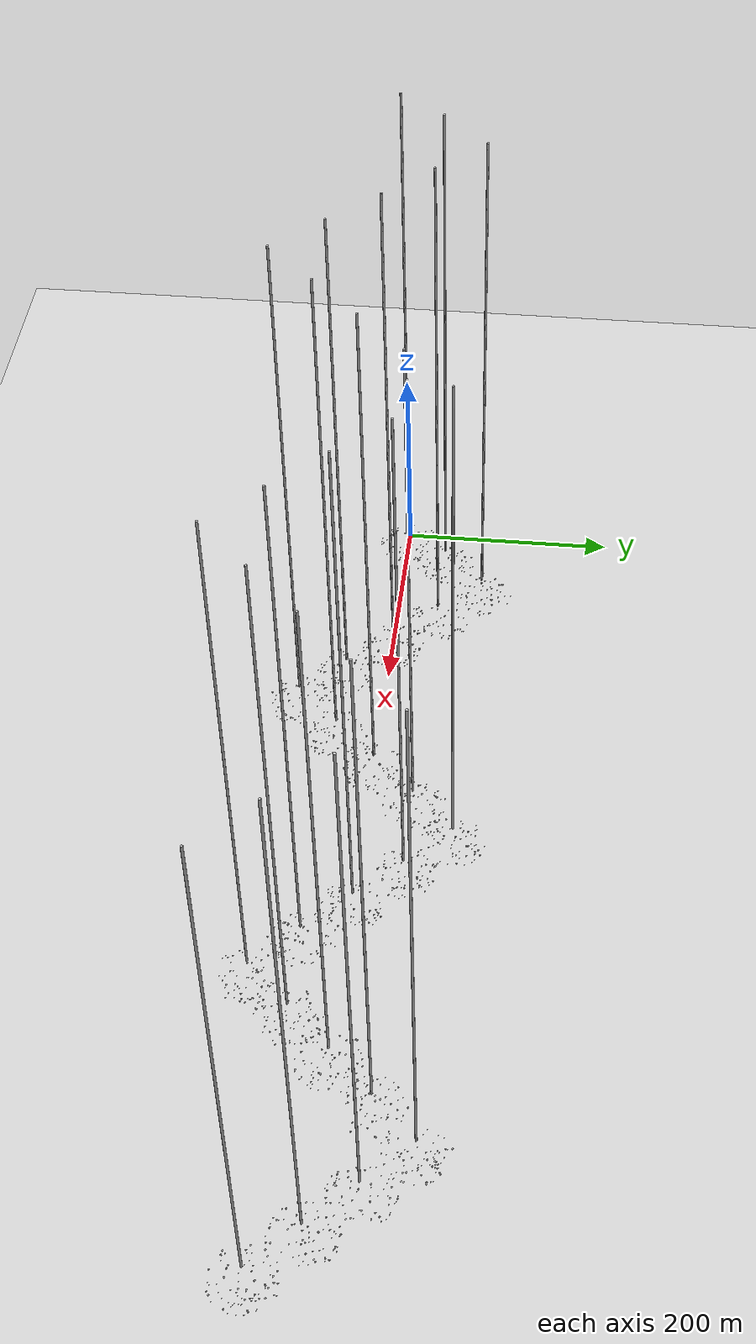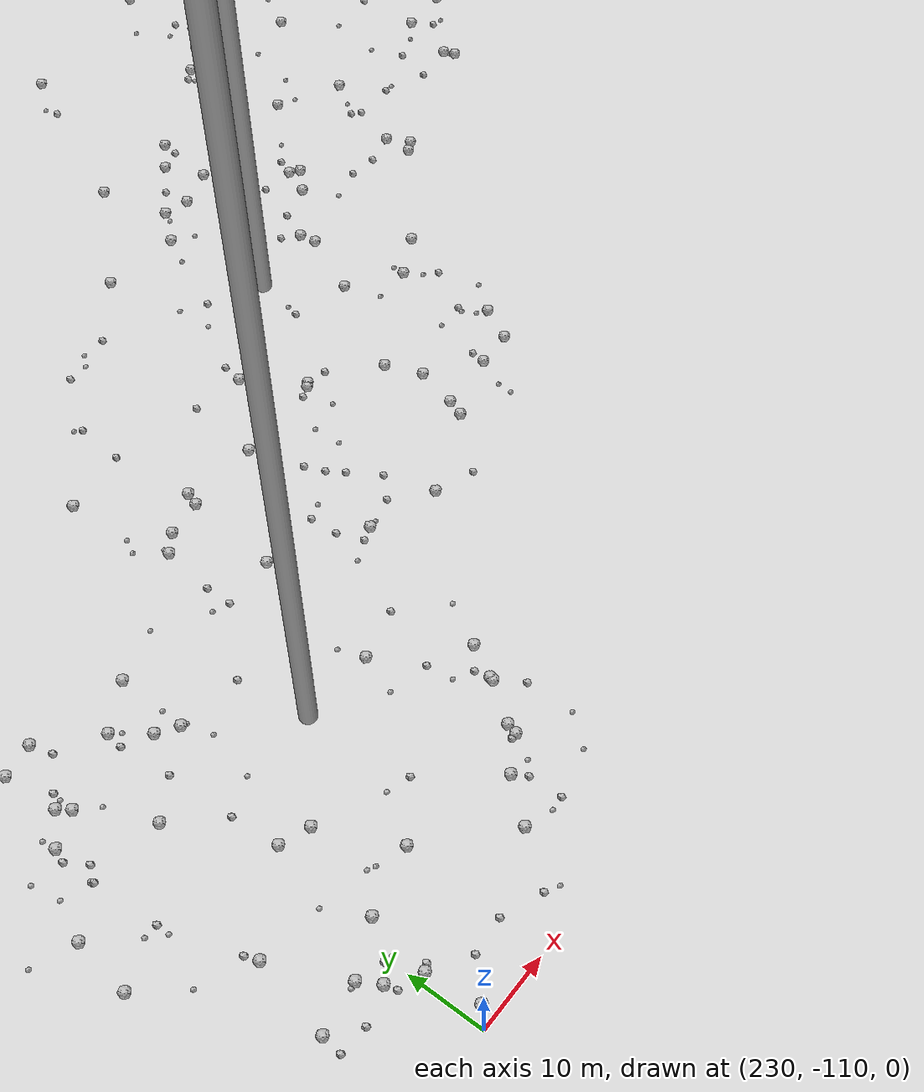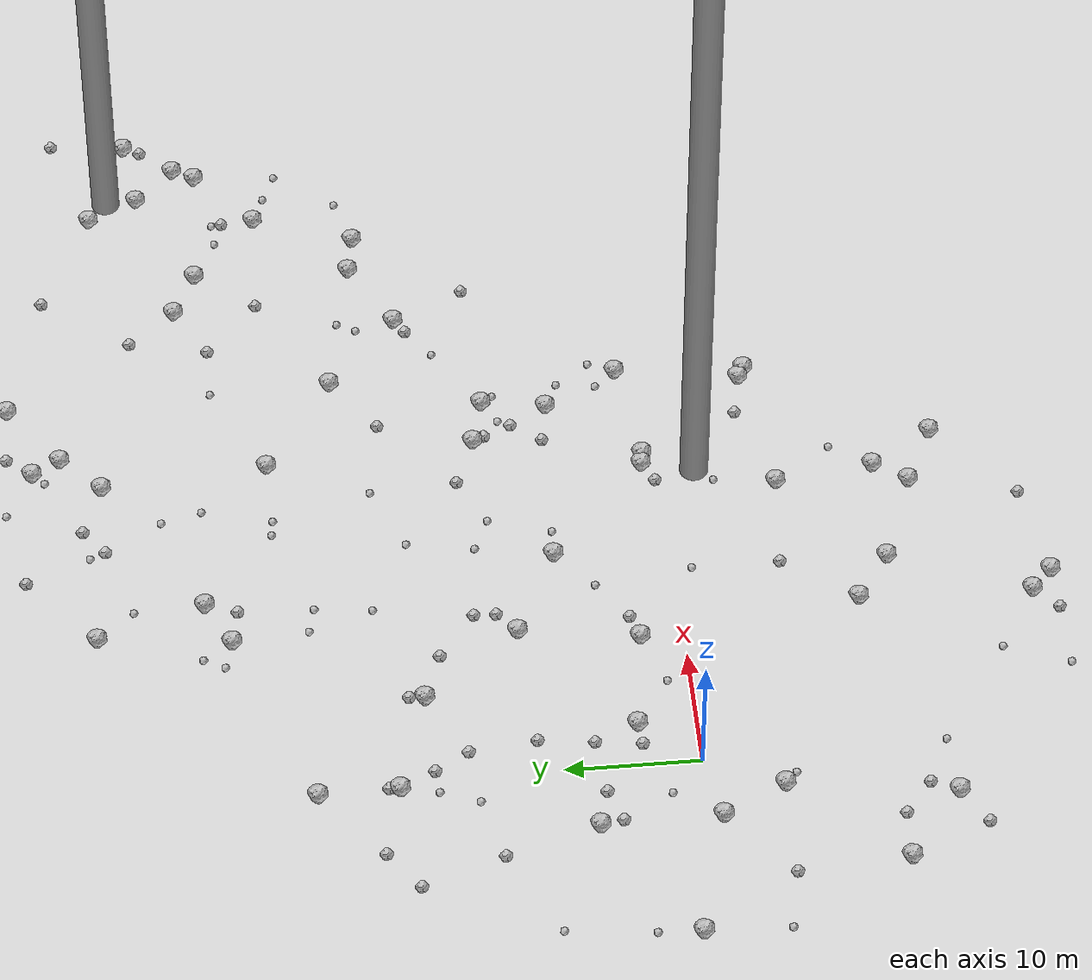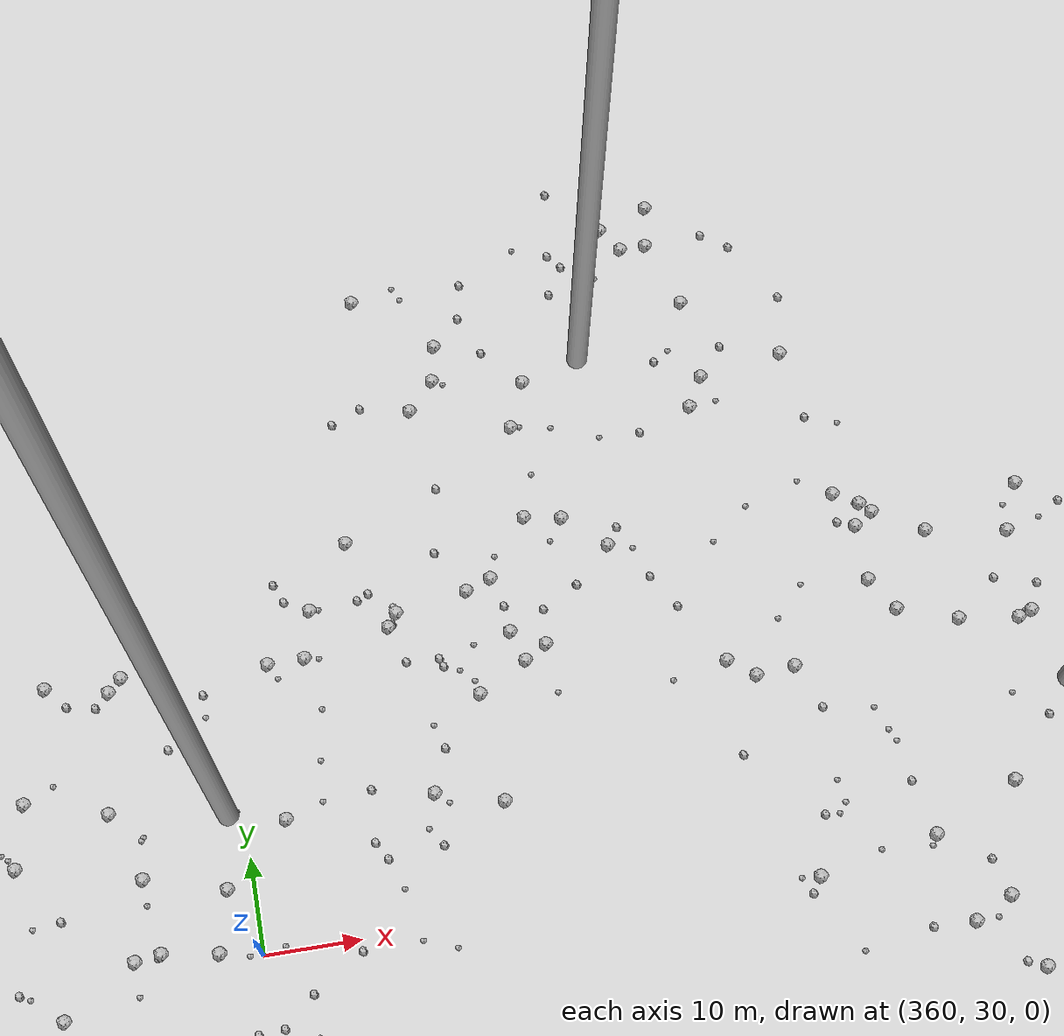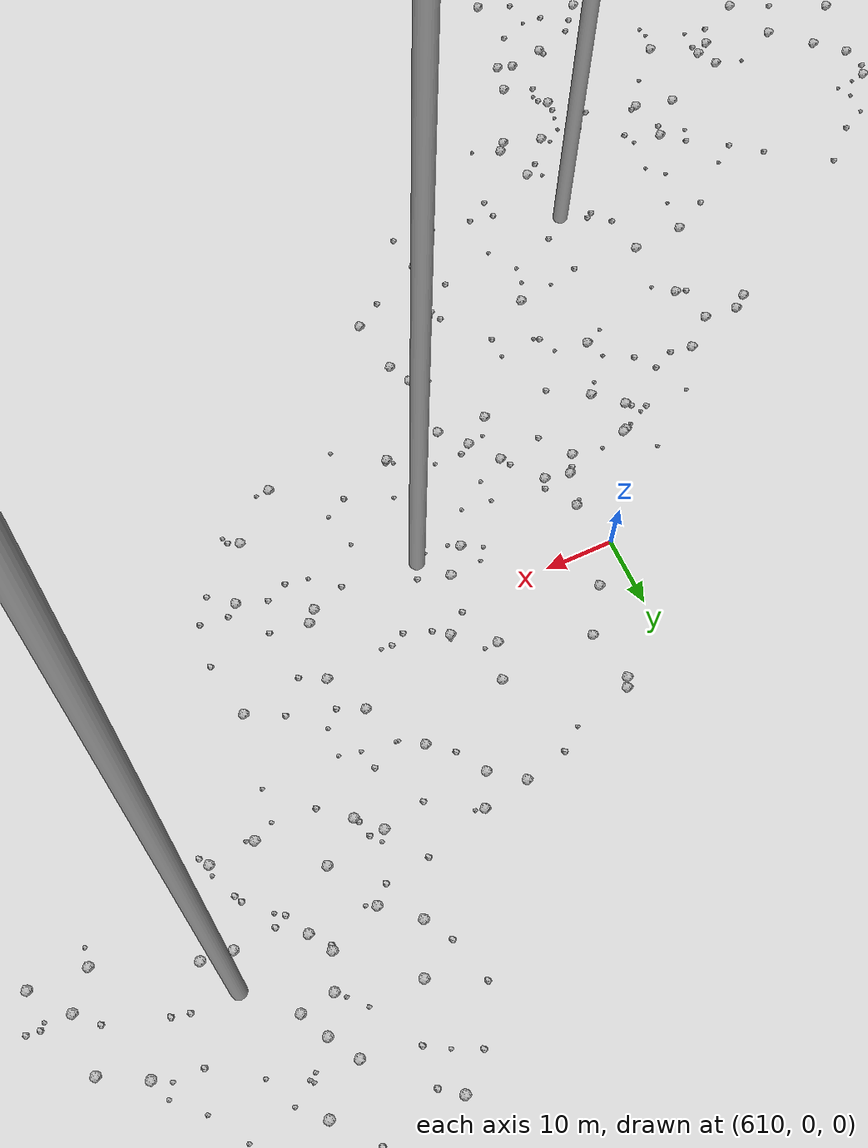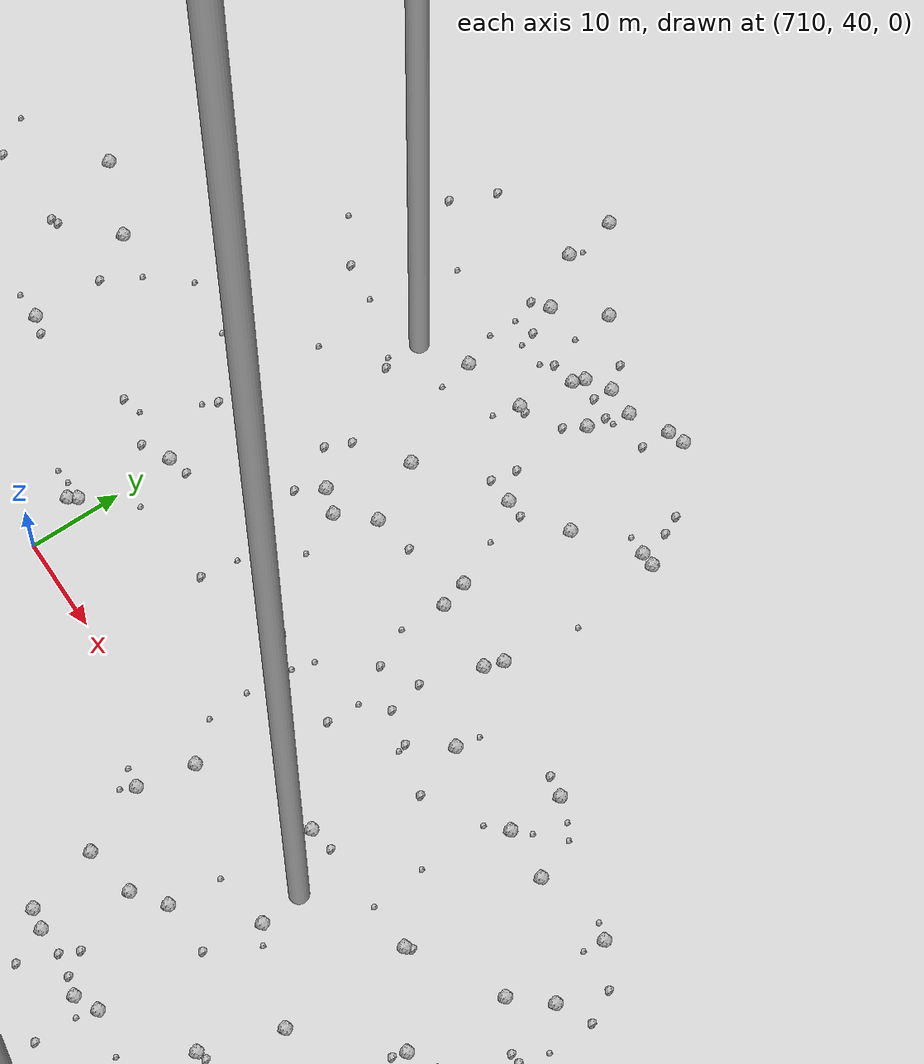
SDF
<sdf version="1.6">
 <world name="default">
  <include><uri>model://custom_ground</uri></include>
  <include><uri>model://sun</uri></include>
  <spherical_coordinates>
   <surface_model>EARTH_WGS84</surface_model>
   <latitude_deg>38.161479</latitude_deg>
   <longitude_deg>-122.454630</longitude_deg>
   <elevation>488.0</elevation>
   <heading_deg>90</heading_deg>
  </spherical_coordinates>
  <model name="rock1_0_0">
   <include><uri>model://rock1</uri><pose>38.499279335923404 2.4962677503804684 0.5 0 0 0</pose></include>
  </model>
  <model name="rock1_0_1">
   <include><uri>model://rock1</uri><pose>-5.152928977095758 -0.9104983661582082 0.5 0 0 0</pose></include>
  </model>
  <model name="rock1_0_2">
   <include><uri>model://rock1</uri><pose>37.945662890087135 -7.302142973694959 0.5 0 0 0</pose></include>
  </model>
  <model name="rock1_0_3">
   <include><uri>model://rock1</uri><pose>28.872317144644384 1.4413041734034984 0.5 0 0 0</pose></include>
  </model>
  <model name="rock1_0_4">
   <include><uri>model://rock1</uri><pose>13.255718860499968 12.153403815101896 0.5 0 0 0</pose></include>
  </model>
  <model name="rock1_0_5">
   <include><uri>model://rock1</uri><pose>37.04528922822963 -6.801801094313049 0.5 0 0 0</pose></include>
  </model>
  <model name="rock1_0_6">
   <include><uri>model://rock1</uri><pose>-0.7353882486554895 21.793082053032585 0.5 0 0 0</pose></include>
  </model>
  <model name="rock1_0_7">
   <include><uri>model://rock1</uri><pose>3.7355522780256685 4.320777553161918 0.5 0 0 0</pose></include>
  </model>
  <model name="rock1_0_8">
   <include><uri>model://rock1</uri><pose>-4.442931170820753 -17.910991332107574 0.5 0 0 0</pose></include>
  </model>
  <model name="rock1_0_9">
   <include><uri>model://rock1</uri><pose>-0.8283816483624058 27.695385124310214 0.5 0 0 0</pose></include>
  </model>
  <model name="rock1_0_10">
   <include><uri>model://rock1</uri><pose>30.244649839563095 -20.503867427040976 0.5 0 0 0</pose></include>
  </model>
  <model name="rock1_0_11">
   <include><uri>model://rock1</uri><pose>27.220844848968284 -15.789167048249865 0.5 0 0 0</pose></include>
  </model>
  <model name="rock1_0_12">
   <include><uri>model://rock1</uri><pose>25.45186391371555 -18.274446917702353 0.5 0 0 0</pose></include>
  </model>
  <model name="rock1_0_13">
   <include><uri>model://rock1</uri><pose>20.462280059421616 8.828627315640574 0.5 0 0 0</pose></include>
  </model>
  <model name="rock1_0_14">
   <include><uri>model://rock1</uri><pose>11.926625334582937 3.2746584931311062 0.5 0 0 0</pose></include>
  </model>
  <model name="rock1_0_15">
   <include><uri>model://rock1</uri><pose>-10.066269611143353 -13.721339866017864 0.5 0 0 0</pose></include>
  </model>
  <model name="rock1_0_16">
   <include><uri>model://rock1</uri><pose>7.542467508907645 19.38392832837701 0.5 0 0 0</pose></include>
  </model>
  <model name="rock1_0_17">
   <include><uri>model://rock1</uri><pose>29.897797213910508 1.2843652691319605 0.5 0 0 0</pose></include>
  </model>
  <model name="rock1_0_18">
   <include><uri>model://rock1</uri><pose>26.19567070392096 -8.402248281986171 0.5 0 0 0</pose></include>
  </model>
  <model name="rock1_0_19">
   <include><uri>model://rock1</uri><pose>35.35345252947786 8.054114043723885 0.5 0 0 0</pose></include>
  </model>
  <model name="rock1_0_20">
   <include><uri>model://rock1</uri><pose>13.886486923757616 -25.92879957857226 0.5 0 0 0</pose></include>
  </model>
  <model name="rock1_0_21">
   <include><uri>model://rock1</uri><pose>-5.300407151325269 7.896970477874746 0.5 0 0 0</pose></include>
  </model>
  <model name="rock1_0_22">
   <include><uri>model://rock1</uri><pose>-15.34831475124063 1.6616403832092956 0.5 0 0 0</pose></include>
  </model>
  <model name="rock1_0_23">
   <include><uri>model://rock1</uri><pose>15.64841040327007 -27.530104111239563 0.5 0 0 0</pose></include>
  </model>
  <model name="rock1_0_24">
   <include><uri>model://rock1</uri><pose>18.07461416265477 -15.675990531605583 0.5 0 0 0</pose></include>
  </model>
  <model name="rock1_0_25">
   <include><uri>model://rock1</uri><pose>-2.70148578261065 -5.624107172394233 0.5 0 0 0</pose></include>
  </model>
  <model name="rock1_0_26">
   <include><uri>model://rock1</uri><pose>14.275333095724022 -13.102022111534165 0.5 0 0 0</pose></include>
  </model>
  <model name="rock2_0_0">
   <include><uri>model://rock2</uri><pose>27.02331365735428 0.5724271778307646 0.3 0 0 0</pose></include>
  </model>
  <model name="rock2_0_1">
   <include><uri>model://rock2</uri><pose>11.893887061078097 -27.662580433388936 0.3 0 0 0</pose></include>
  </model>
  <model name="rock2_0_2">
   <include><uri>model://rock2</uri><pose>-10.80923143893726 -5.494066823289703 0.3 0 0 0</pose></include>
  </model>
  <model name="rock2_0_3">
   <include><uri>model://rock2</uri><pose>-7.5603640945554105 -19.63111680444857 0.3 0 0 0</pose></include>
  </model>
  <model name="rock2_0_4">
   <include><uri>model://rock2</uri><pose>-3.6071327797772383 -15.940006337208075 0.3 0 0 0</pose></include>
  </model>
  <model name="rock2_0_5">
   <include><uri>model://rock2</uri><pose>1.7464187494099974 4.155256694556293 0.3 0 0 0</pose></include>
  </model>
  <model name="rock2_0_6">
   <include><uri>model://rock2</uri><pose>-5.100762623920662 6.208931861441805 0.3 0 0 0</pose></include>
  </model>
  <model name="rock2_0_7">
   <include><uri>model://rock2</uri><pose>23.393812078505775 -26.264020312862304 0.3 0 0 0</pose></include>
  </model>
  <model name="rock2_0_8">
   <include><uri>model://rock2</uri><pose>33.32857869919631 -6.130960711065864 0.3 0 0 0</pose></include>
  </model>
  <model name="rock2_0_9">
   <include><uri>model://rock2</uri><pose>14.881491976080056 13.578374644520046 0.3 0 0 0</pose></include>
  </model>
  <model name="rock2_0_10">
   <include><uri>model://rock2</uri><pose>2.0887625794577396 16.664092540929822 0.3 0 0 0</pose></include>
  </model>
  <model name="rock2_0_11">
   <include><uri>model://rock2</uri><pose>-6.671885726056681 23.21838671892563 0.3 0 0 0</pose></include>
  </model>
  <model name="rock2_0_12">
   <include><uri>model://rock2</uri><pose>2.175653901965731 7.55621944527325 0.3 0 0 0</pose></include>
  </model>
  <model name="rock2_0_13">
   <include><uri>model://rock2</uri><pose>-2.416189578667371 7.1222629391139805 0.3 0 0 0</pose></include>
  </model>
  <model name="rock2_0_14">
   <include><uri>model://rock2</uri><pose>-6.257122335890346 -13.871518116724015 0.3 0 0 0</pose></include>
  </model>
  <model name="rock2_0_15">
   <include><uri>model://rock2</uri><pose>11.23729765504941 18.002280006319793 0.3 0 0 0</pose></include>
  </model>
  <model name="rock2_0_16">
   <include><uri>model://rock2</uri><pose>31.832530857297805 8.634781763451606 0.3 0 0 0</pose></include>
  </model>
  <model name="rock2_0_17">
   <include><uri>model://rock2</uri><pose>14.926596627559412 15.227981306011287 0.3 0 0 0</pose></include>
  </model>
  <model name="rock2_0_18">
   <include><uri>model://rock2</uri><pose>-7.5967089939621 14.839910347183384 0.3 0 0 0</pose></include>
  </model>
  <model name="rock2_0_19">
   <include><uri>model://rock2</uri><pose>2.706769117059771 11.653223938660986 0.3 0 0 0</pose></include>
  </model>
  <model name="rock2_0_20">
   <include><uri>model://rock2</uri><pose>33.52656852426311 10.870476280083821 0.3 0 0 0</pose></include>
  </model>
  <model name="rock2_0_21">
   <include><uri>model://rock2</uri><pose>-0.760123575863048 22.582875693237078 0.3 0 0 0</pose></include>
  </model>
  <model name="rock2_0_22">
   <include><uri>model://rock2</uri><pose>18.14554257853076 -7.746170398458794 0.3 0 0 0</pose></include>
  </model>
  <model name="rock2_0_23">
   <include><uri>model://rock2</uri><pose>13.777270722726925 3.8587025737427965 0.3 0 0 0</pose></include>
  </model>
  <model name="rock2_0_24">
   <include><uri>model://rock2</uri><pose>7.5493060135132914 20.536534454075166 0.3 0 0 0</pose></include>
  </model>
  <model name="rock2_0_25">
   <include><uri>model://rock2</uri><pose>0.5287542916673651 19.20132245513718 0.3 0 0 0</pose></include>
  </model>
  <model name="rock2_0_26">
   <include><uri>model://rock2</uri><pose>-9.795584714374924 20.972117363285378 0.3 0 0 0</pose></include>
  </model>
  <model name="rock3_0_0">
   <include><uri>model://rock3</uri><pose>34.07706971149315 11.743978658743814 0.2 0 0 0</pose></include>
  </model>
  <model name="rock3_0_1">
   <include><uri>model://rock3</uri><pose>37.42982341449867 6.99981720781863 0.2 0 0 0</pose></include>
  </model>
  <model name="rock3_0_2">
   <include><uri>model://rock3</uri><pose>-15.241879477335763 4.857386670011039 0.2 0 0 0</pose></include>
  </model>
  <model name="rock3_0_3">
   <include><uri>model://rock3</uri><pose>22.64595713966164 8.688945796644106 0.2 0 0 0</pose></include>
  </model>
  <model name="rock3_0_4">
   <include><uri>model://rock3</uri><pose>-1.3730413784639204 18.987334607214834 0.2 0 0 0</pose></include>
  </model>
  <model name="rock3_0_5">
   <include><uri>model://rock3</uri><pose>16.139561903334688 22.512918189770858 0.2 0 0 0</pose></include>
  </model>
  <model name="rock3_0_6">
   <include><uri>model://rock3</uri><pose>17.10774962822554 6.020044090092171 0.2 0 0 0</pose></include>
  </model>
  <model name="rock3_0_7">
   <include><uri>model://rock3</uri><pose>26.72104152226286 -3.822288309577484 0.2 0 0 0</pose></include>
  </model>
  <model name="rock3_0_8">
   <include><uri>model://rock3</uri><pose>6.639740843753806 -27.776940577675106 0.2 0 0 0</pose></include>
  </model>
  <model name="rock3_0_9">
   <include><uri>model://rock3</uri><pose>7.50959654884451 1.719176949064753 0.2 0 0 0</pose></include>
  </model>
  <model name="rock3_0_10">
   <include><uri>model://rock3</uri><pose>39.350231329919225 4.402659557559836 0.2 0 0 0</pose></include>
  </model>
  <model name="rock3_0_11">
   <include><uri>model://rock3</uri><pose>18.175154538680843 -1.2494495990505392 0.2 0 0 0</pose></include>
  </model>
  <model name="rock3_0_12">
   <include><uri>model://rock3</uri><pose>-1.8346739559804455 -6.56428914301506 0.2 0 0 0</pose></include>
  </model>
  <model name="rock3_0_13">
   <include><uri>model://rock3</uri><pose>24.109915852912103 13.380031239953183 0.2 0 0 0</pose></include>
  </model>
  <model name="rock3_0_14">
   <include><uri>model://rock3</uri><pose>27.69237010555711 21.86886470887019 0.2 0 0 0</pose></include>
  </model>
  <model name="rock3_0_15">
   <include><uri>model://rock3</uri><pose>-2.473867989292266 16.144205297118113 0.2 0 0 0</pose></include>
  </model>
  <model name="rock3_0_16">
   <include><uri>model://rock3</uri><pose>0.2513109149679593 -17.677125758963086 0.2 0 0 0</pose></include>
  </model>
  <model name="rock3_0_17">
   <include><uri>model://rock3</uri><pose>-15.631517626896175 -4.627329875727725 0.2 0 0 0</pose></include>
  </model>
  <model name="rock3_0_18">
   <include><uri>model://rock3</uri><pose>22.338157231815615 19.57204004802756 0.2 0 0 0</pose></include>
  </model>
  <model name="rock3_0_19">
   <include><uri>model://rock3</uri><pose>16.61360620949948 26.781560733248057 0.2 0 0 0</pose></include>
  </model>
  <model name="rock3_0_20">
   <include><uri>model://rock3</uri><pose>14.50261263640364 27.274808044339835 0.2 0 0 0</pose></include>
  </model>
  <model name="rock3_0_21">
   <include><uri>model://rock3</uri><pose>-14.542438119222464 11.3529888628115 0.2 0 0 0</pose></include>
  </model>
  <model name="rock3_0_22">
   <include><uri>model://rock3</uri><pose>29.222818641946432 -12.806174349643658 0.2 0 0 0</pose></include>
  </model>
  <model name="rock3_0_23">
   <include><uri>model://rock3</uri><pose>37.01298480150593 4.050767399589503 0.2 0 0 0</pose></include>
  </model>
  <model name="rock3_0_24">
   <include><uri>model://rock3</uri><pose>8.537300324519688 -23.007377192575383 0.2 0 0 0</pose></include>
  </model>
  <model name="rock3_0_25">
   <include><uri>model://rock3</uri><pose>-2.897560105979501 2.4495147193284907 0.2 0 0 0</pose></include>
  </model>
  <model name="rock3_0_26">
   <include><uri>model://rock3</uri><pose>21.444698590696213 14.558140509436349 0.2 0 0 0</pose></include>
  </model>
  <model name="rock1_1_0">
   <include><uri>model://rock1</uri><pose>54.29668221441589 21.39021349588492 0.5 0 0 0</pose></include>
  </model>
  <model name="rock1_1_1">
   <include><uri>model://rock1</uri><pose>58.21397919768528 41.69280194008685 0.5 0 0 0</pose></include>
  </model>
  <model name="rock1_1_2">
   <include><uri>model://rock1</uri><pose>60.090129091694415 37.93617536000362 0.5 0 0 0</pose></include>
  </model>
  <model name="rock1_1_3">
   <include><uri>model://rock1</uri><pose>22.676111939130372 50.73703917200128 0.5 0 0 0</pose></include>
  </model>
  <model name="rock1_1_4">
   <include><uri>model://rock1</uri><pose>17.78559840980621 34.77026625476216 0.5 0 0 0</pose></include>
  </model>
  <model name="rock1_1_5">
   <include><uri>model://rock1</uri><pose>32.252710999819946 13.829060160413729 0.5 0 0 0</pose></include>
  </model>
  <model name="rock1_1_6">
   <include><uri>model://rock1</uri><pose>31.114411414903223 29.440267754264696 0.5 0 0 0</pose></include>
  </model>
  <model name="rock1_1_7">
   <include><uri>model://rock1</uri><pose>19.541405477585283 54.45105226420409 0.5 0 0 0</pose></include>
  </model>
  <model name="rock1_1_8">
   <include><uri>model://rock1</uri><pose>15.147583967599969 42.74799088986968 0.5 0 0 0</pose></include>
  </model>
  <model name="rock1_1_9">
   <include><uri>model://rock1</uri><pose>62.143113952915236 33.292640496132066 0.5 0 0 0</pose></include>
  </model>
  <model name="rock1_1_10">
   <include><uri>model://rock1</uri><pose>51.0351540024751 21.935585490095413 0.5 0 0 0</pose></include>
  </model>
  <model name="rock1_1_11">
   <include><uri>model://rock1</uri><pose>45.3017897809793 18.845085740677856 0.5 0 0 0</pose></include>
  </model>
  <model name="rock1_1_12">
   <include><uri>model://rock1</uri><pose>57.07950638010538 28.946010714337216 0.5 0 0 0</pose></include>
  </model>
  <model name="rock1_1_13">
   <include><uri>model://rock1</uri><pose>27.062426297014866 58.65629117806333 0.5 0 0 0</pose></include>
  </model>
  <model name="rock1_1_14">
   <include><uri>model://rock1</uri><pose>27.514908383846453 65.68885261615458 0.5 0 0 0</pose></include>
  </model>
  <model name="rock1_1_15">
   <include><uri>model://rock1</uri><pose>36.11470552999894 12.88464034044573 0.5 0 0 0</pose></include>
  </model>
  <model name="rock1_1_16">
   <include><uri>model://rock1</uri><pose>33.06453502083174 44.85590683600996 0.5 0 0 0</pose></include>
  </model>
  <model name="rock1_1_17">
   <include><uri>model://rock1</uri><pose>47.66343528780487 35.585197122045344 0.5 0 0 0</pose></include>
  </model>
  <model name="rock1_1_18">
   <include><uri>model://rock1</uri><pose>63.06722852370892 34.95241192971812 0.5 0 0 0</pose></include>
  </model>
  <model name="rock1_1_19">
   <include><uri>model://rock1</uri><pose>38.41017959308194 48.64958195196388 0.5 0 0 0</pose></include>
  </model>
  <model name="rock1_1_20">
   <include><uri>model://rock1</uri><pose>31.84042531369347 46.96418059785995 0.5 0 0 0</pose></include>
  </model>
  <model name="rock1_1_21">
   <include><uri>model://rock1</uri><pose>39.14355176301689 24.183343119337326 0.5 0 0 0</pose></include>
  </model>
  <model name="rock1_1_22">
   <include><uri>model://rock1</uri><pose>29.996115990116913 41.86405271967678 0.5 0 0 0</pose></include>
  </model>
  <model name="rock1_1_23">
   <include><uri>model://rock1</uri><pose>65.93767162471804 38.67410566703282 0.5 0 0 0</pose></include>
  </model>
  <model name="rock1_1_24">
   <include><uri>model://rock1</uri><pose>14.061489020490248 32.967945210447 0.5 0 0 0</pose></include>
  </model>
  <model name="rock1_1_25">
   <include><uri>model://rock1</uri><pose>51.42151661810545 33.8042194358335 0.5 0 0 0</pose></include>
  </model>
  <model name="rock1_1_26">
   <include><uri>model://rock1</uri><pose>32.37949564638147 55.9224888967292 0.5 0 0 0</pose></include>
  </model>
  <model name="rock2_1_0">
   <include><uri>model://rock2</uri><pose>66.53020735722367 44.34644415566646 0.3 0 0 0</pose></include>
  </model>
  <model name="rock2_1_1">
   <include><uri>model://rock2</uri><pose>17.517849496093614 55.53953770841254 0.3 0 0 0</pose></include>
  </model>
  <model name="rock2_1_2">
   <include><uri>model://rock2</uri><pose>32.56432949961465 12.96386208871281 0.3 0 0 0</pose></include>
  </model>
  <model name="rock2_1_3">
   <include><uri>model://rock2</uri><pose>34.32077152390779 20.88727220716931 0.3 0 0 0</pose></include>
  </model>
  <model name="rock2_1_4">
   <include><uri>model://rock2</uri><pose>25.61574700334239 43.39824261953897 0.3 0 0 0</pose></include>
  </model>
  <model name="rock2_1_5">
   <include><uri>model://rock2</uri><pose>20.936320369705438 47.74074414153255 0.3 0 0 0</pose></include>
  </model>
  <model name="rock2_1_6">
   <include><uri>model://rock2</uri><pose>26.145766024956508 50.15937752336473 0.3 0 0 0</pose></include>
  </model>
  <model name="rock2_1_7">
   <include><uri>model://rock2</uri><pose>43.20938456625229 33.22763594433975 0.3 0 0 0</pose></include>
  </model>
  <model name="rock2_1_8">
   <include><uri>model://rock2</uri><pose>33.3550330884182 48.857531237920206 0.3 0 0 0</pose></include>
  </model>
  <model name="rock2_1_9">
   <include><uri>model://rock2</uri><pose>44.54469217541752 54.58058545588336 0.3 0 0 0</pose></include>
  </model>
  <model name="rock2_1_10">
   <include><uri>model://rock2</uri><pose>59.78544677273265 52.81630528231161 0.3 0 0 0</pose></include>
  </model>
  <model name="rock2_1_11">
   <include><uri>model://rock2</uri><pose>47.8630232622672 13.414992874355116 0.3 0 0 0</pose></include>
  </model>
  <model name="rock2_1_12">
   <include><uri>model://rock2</uri><pose>47.74842139738757 29.28702421599936 0.3 0 0 0</pose></include>
  </model>
  <model name="rock2_1_13">
   <include><uri>model://rock2</uri><pose>23.488672236597175 41.8152056570309 0.3 0 0 0</pose></include>
  </model>
  <model name="rock2_1_14">
   <include><uri>model://rock2</uri><pose>65.20407538723993 37.40699914683934 0.3 0 0 0</pose></include>
  </model>
  <model name="rock2_1_15">
   <include><uri>model://rock2</uri><pose>56.770501744856425 31.42251931028303 0.3 0 0 0</pose></include>
  </model>
  <model name="rock2_1_16">
   <include><uri>model://rock2</uri><pose>67.33258836278546 49.078884224232844 0.3 0 0 0</pose></include>
  </model>
  <model name="rock2_1_17">
   <include><uri>model://rock2</uri><pose>16.808823461606266 32.41761246363008 0.3 0 0 0</pose></include>
  </model>
  <model name="rock2_1_18">
   <include><uri>model://rock2</uri><pose>42.57993694669471 65.0941939173694 0.3 0 0 0</pose></include>
  </model>
  <model name="rock2_1_19">
   <include><uri>model://rock2</uri><pose>40.53114626846474 68.06887510424441 0.3 0 0 0</pose></include>
  </model>
  <model name="rock2_1_20">
   <include><uri>model://rock2</uri><pose>42.23159979551961 58.824937493315396 0.3 0 0 0</pose></include>
  </model>
  <model name="rock2_1_21">
   <include><uri>model://rock2</uri><pose>49.381114627688625 45.6758896692154 0.3 0 0 0</pose></include>
  </model>
  <model name="rock2_1_22">
   <include><uri>model://rock2</uri><pose>48.2658457641125 60.360909059839784 0.3 0 0 0</pose></include>
  </model>
  <model name="rock2_1_23">
   <include><uri>model://rock2</uri><pose>44.533795866166976 39.12046480569158 0.3 0 0 0</pose></include>
  </model>
  <model name="rock2_1_24">
   <include><uri>model://rock2</uri><pose>48.05614505752832 57.13992635676628 0.3 0 0 0</pose></include>
  </model>
  <model name="rock2_1_25">
   <include><uri>model://rock2</uri><pose>43.95090148998022 18.057107704681357 0.3 0 0 0</pose></include>
  </model>
  <model name="rock2_1_26">
   <include><uri>model://rock2</uri><pose>28.082447284293963 15.388937678575804 0.3 0 0 0</pose></include>
  </model>
  <model name="rock3_1_0">
   <include><uri>model://rock3</uri><pose>22.36960670941813 61.586612639220114 0.2 0 0 0</pose></include>
  </model>
  <model name="rock3_1_1">
   <include><uri>model://rock3</uri><pose>59.28223971287477 28.001095261783263 0.2 0 0 0</pose></include>
  </model>
  <model name="rock3_1_2">
   <include><uri>model://rock3</uri><pose>27.80011625362873 48.96761398362439 0.2 0 0 0</pose></include>
  </model>
  <model name="rock3_1_3">
   <include><uri>model://rock3</uri><pose>56.75124905753931 32.14046615137053 0.2 0 0 0</pose></include>
  </model>
  <model name="rock3_1_4">
   <include><uri>model://rock3</uri><pose>25.50223891198133 29.273095994785642 0.2 0 0 0</pose></include>
  </model>
  <model name="rock3_1_5">
   <include><uri>model://rock3</uri><pose>43.00207487233748 54.93451804321046 0.2 0 0 0</pose></include>
  </model>
  <model name="rock3_1_6">
   <include><uri>model://rock3</uri><pose>12.467343526927593 35.10515836287358 0.2 0 0 0</pose></include>
  </model>
  <model name="rock3_1_7">
   <include><uri>model://rock3</uri><pose>41.43761152126667 16.151576567429338 0.2 0 0 0</pose></include>
  </model>
  <model name="rock3_1_8">
   <include><uri>model://rock3</uri><pose>37.207193917595724 55.590630194355285 0.2 0 0 0</pose></include>
  </model>
  <model name="rock3_1_9">
   <include><uri>model://rock3</uri><pose>26.895858746307542 34.51295519173311 0.2 0 0 0</pose></include>
  </model>
  <model name="rock3_1_10">
   <include><uri>model://rock3</uri><pose>45.25654451765196 23.141768217136516 0.2 0 0 0</pose></include>
  </model>
  <model name="rock3_1_11">
   <include><uri>model://rock3</uri><pose>17.4501951984018 39.94985764416842 0.2 0 0 0</pose></include>
  </model>
  <model name="rock3_1_12">
   <include><uri>model://rock3</uri><pose>36.67011732521202 11.962379495996364 0.2 0 0 0</pose></include>
  </model>
  <model name="rock3_1_13">
   <include><uri>model://rock3</uri><pose>44.465571158241445 21.75769920859583 0.2 0 0 0</pose></include>
  </model>
  <model name="rock3_1_14">
   <include><uri>model://rock3</uri><pose>24.15472703555818 29.43227850238437 0.2 0 0 0</pose></include>
  </model>
  <model name="rock3_1_15">
   <include><uri>model://rock3</uri><pose>61.64189010111285 27.002399392641653 0.2 0 0 0</pose></include>
  </model>
  <model name="rock3_1_16">
   <include><uri>model://rock3</uri><pose>30.826200492286876 46.01653058676697 0.2 0 0 0</pose></include>
  </model>
  <model name="rock3_1_17">
   <include><uri>model://rock3</uri><pose>58.47792753422122 54.76974041854629 0.2 0 0 0</pose></include>
  </model>
  <model name="rock3_1_18">
   <include><uri>model://rock3</uri><pose>38.80260027591355 33.22070158616551 0.2 0 0 0</pose></include>
  </model>
  <model name="rock3_1_19">
   <include><uri>model://rock3</uri><pose>35.01734248299806 63.697799684957744 0.2 0 0 0</pose></include>
  </model>
  <model name="rock3_1_20">
   <include><uri>model://rock3</uri><pose>23.018227744355993 42.92416393402552 0.2 0 0 0</pose></include>
  </model>
  <model name="rock3_1_21">
   <include><uri>model://rock3</uri><pose>40.21646255812975 56.62990941943348 0.2 0 0 0</pose></include>
  </model>
  <model name="rock3_1_22">
   <include><uri>model://rock3</uri><pose>58.20054950397734 22.48122626079735 0.2 0 0 0</pose></include>
  </model>
  <model name="rock3_1_23">
   <include><uri>model://rock3</uri><pose>33.7587298622838 60.34007807770961 0.2 0 0 0</pose></include>
  </model>
  <model name="rock3_1_24">
   <include><uri>model://rock3</uri><pose>11.620326258269255 33.55133857785812 0.2 0 0 0</pose></include>
  </model>
  <model name="rock3_1_25">
   <include><uri>model://rock3</uri><pose>26.065546416106198 37.54051588348746 0.2 0 0 0</pose></include>
  </model>
  <model name="rock3_1_26">
   <include><uri>model://rock3</uri><pose>54.75191473561545 32.027539528875415 0.2 0 0 0</pose></include>
  </model>
  <model name="rock1_2_0">
   <include><uri>model://rock1</uri><pose>68.95049911255745 67.15564269936358 0.5 0 0 0</pose></include>
  </model>
  <model name="rock1_2_1">
   <include><uri>model://rock1</uri><pose>94.03538406154952 91.32051863585357 0.5 0 0 0</pose></include>
  </model>
  <model name="rock1_2_2">
   <include><uri>model://rock1</uri><pose>60.60027471885151 81.76970569957854 0.5 0 0 0</pose></include>
  </model>
  <model name="rock1_2_3">
   <include><uri>model://rock1</uri><pose>64.34293237651751 98.43204624749691 0.5 0 0 0</pose></include>
  </model>
  <model name="rock1_2_4">
   <include><uri>model://rock1</uri><pose>59.19027902528134 73.29469387661462 0.5 0 0 0</pose></include>
  </model>
  <model name="rock1_2_5">
   <include><uri>model://rock1</uri><pose>70.56928209999498 89.26223610282926 0.5 0 0 0</pose></include>
  </model>
  <model name="rock1_2_6">
   <include><uri>model://rock1</uri><pose>83.11620073736457 64.52274959017396 0.5 0 0 0</pose></include>
  </model>
  <model name="rock1_2_7">
   <include><uri>model://rock1</uri><pose>64.9399510099458 96.34207588093156 0.5 0 0 0</pose></include>
  </model>
  <model name="rock1_2_8">
   <include><uri>model://rock1</uri><pose>65.49345075501037 57.30473038463943 0.5 0 0 0</pose></include>
  </model>
  <model name="rock1_2_9">
   <include><uri>model://rock1</uri><pose>87.62860740404037 80.35146400437307 0.5 0 0 0</pose></include>
  </model>
  <model name="rock1_2_10">
   <include><uri>model://rock1</uri><pose>104.00399485087195 80.28944124649519 0.5 0 0 0</pose></include>
  </model>
  <model name="rock1_2_11">
   <include><uri>model://rock1</uri><pose>73.24706535403263 84.89930030661228 0.5 0 0 0</pose></include>
  </model>
  <model name="rock1_2_12">
   <include><uri>model://rock1</uri><pose>82.99438336822429 96.81351930091483 0.5 0 0 0</pose></include>
  </model>
  <model name="rock1_2_13">
   <include><uri>model://rock1</uri><pose>88.91479887246172 98.10495137308524 0.5 0 0 0</pose></include>
  </model>
  <model name="rock1_2_14">
   <include><uri>model://rock1</uri><pose>78.88097887312233 66.38862406406535 0.5 0 0 0</pose></include>
  </model>
  <model name="rock1_2_15">
   <include><uri>model://rock1</uri><pose>72.4620201453395 51.43188138386541 0.5 0 0 0</pose></include>
  </model>
  <model name="rock1_2_16">
   <include><uri>model://rock1</uri><pose>50.29370329822308 79.12267845236599 0.5 0 0 0</pose></include>
  </model>
  <model name="rock1_2_17">
   <include><uri>model://rock1</uri><pose>64.00830758547073 78.65484452207781 0.5 0 0 0</pose></include>
  </model>
  <model name="rock1_2_18">
   <include><uri>model://rock1</uri><pose>93.66770053220847 83.91042603397747 0.5 0 0 0</pose></include>
  </model>
  <model name="rock1_2_19">
   <include><uri>model://rock1</uri><pose>64.47839827705398 100.04535057539815 0.5 0 0 0</pose></include>
  </model>
  <model name="rock1_2_20">
   <include><uri>model://rock1</uri><pose>84.40237267375372 56.416131932520884 0.5 0 0 0</pose></include>
  </model>
  <model name="rock1_2_21">
   <include><uri>model://rock1</uri><pose>94.01345227072842 71.81538240911439 0.5 0 0 0</pose></include>
  </model>
  <model name="rock1_2_22">
   <include><uri>model://rock1</uri><pose>56.93028965242425 91.7260292639007 0.5 0 0 0</pose></include>
  </model>
  <model name="rock1_2_23">
   <include><uri>model://rock1</uri><pose>87.55195145897005 90.90689336289752 0.5 0 0 0</pose></include>
  </model>
  <model name="rock1_2_24">
   <include><uri>model://rock1</uri><pose>102.0676086956768 69.18144256460688 0.5 0 0 0</pose></include>
  </model>
  <model name="rock1_2_25">
   <include><uri>model://rock1</uri><pose>80.17531332072028 89.46254938032746 0.5 0 0 0</pose></include>
  </model>
  <model name="rock1_2_26">
   <include><uri>model://rock1</uri><pose>106.10184180436305 89.12621097596349 0.5 0 0 0</pose></include>
  </model>
  <model name="rock2_2_0">
   <include><uri>model://rock2</uri><pose>63.76322760670534 103.77939937536661 0.3 0 0 0</pose></include>
  </model>
  <model name="rock2_2_1">
   <include><uri>model://rock2</uri><pose>92.33069816163635 76.44469406463874 0.3 0 0 0</pose></include>
  </model>
  <model name="rock2_2_2">
   <include><uri>model://rock2</uri><pose>72.2519221102817 95.3908442174228 0.3 0 0 0</pose></include>
  </model>
  <model name="rock2_2_3">
   <include><uri>model://rock2</uri><pose>53.17762311312047 66.73161249677736 0.3 0 0 0</pose></include>
  </model>
  <model name="rock2_2_4">
   <include><uri>model://rock2</uri><pose>70.27586945956352 71.75845387619545 0.3 0 0 0</pose></include>
  </model>
  <model name="rock2_2_5">
   <include><uri>model://rock2</uri><pose>84.86088023783081 65.72075740995055 0.3 0 0 0</pose></include>
  </model>
  <model name="rock2_2_6">
   <include><uri>model://rock2</uri><pose>61.07780568811403 87.67634509149934 0.3 0 0 0</pose></include>
  </model>
  <model name="rock2_2_7">
   <include><uri>model://rock2</uri><pose>95.64870577313448 65.41869362545295 0.3 0 0 0</pose></include>
  </model>
  <model name="rock2_2_8">
   <include><uri>model://rock2</uri><pose>82.36497201411896 96.84135181478399 0.3 0 0 0</pose></include>
  </model>
  <model name="rock2_2_9">
   <include><uri>model://rock2</uri><pose>87.01966458201389 60.15221987332128 0.3 0 0 0</pose></include>
  </model>
  <model name="rock2_2_10">
   <include><uri>model://rock2</uri><pose>109.30569475525814 80.28938471518879 0.3 0 0 0</pose></include>
  </model>
  <model name="rock2_2_11">
   <include><uri>model://rock2</uri><pose>106.83300902087083 83.94567352047906 0.3 0 0 0</pose></include>
  </model>
  <model name="rock2_2_12">
   <include><uri>model://rock2</uri><pose>52.964572131050005 70.97259082907567 0.3 0 0 0</pose></include>
  </model>
  <model name="rock2_2_13">
   <include><uri>model://rock2</uri><pose>104.98195654242622 90.97590904793887 0.3 0 0 0</pose></include>
  </model>
  <model name="rock2_2_14">
   <include><uri>model://rock2</uri><pose>81.70261957885916 73.90767727719157 0.3 0 0 0</pose></include>
  </model>
  <model name="rock2_2_15">
   <include><uri>model://rock2</uri><pose>98.95532597482378 101.39557648779892 0.3 0 0 0</pose></include>
  </model>
  <model name="rock2_2_16">
   <include><uri>model://rock2</uri><pose>85.92701021278235 91.29035660903162 0.3 0 0 0</pose></include>
  </model>
  <model name="rock2_2_17">
   <include><uri>model://rock2</uri><pose>84.34426992036538 85.72793717822927 0.3 0 0 0</pose></include>
  </model>
  <model name="rock2_2_18">
   <include><uri>model://rock2</uri><pose>73.80651827326902 79.27270305534661 0.3 0 0 0</pose></include>
  </model>
  <model name="rock2_2_19">
   <include><uri>model://rock2</uri><pose>80.82537419063578 103.00733691435522 0.3 0 0 0</pose></include>
  </model>
  <model name="rock2_2_20">
   <include><uri>model://rock2</uri><pose>67.94228536370895 80.62134859455304 0.3 0 0 0</pose></include>
  </model>
  <model name="rock2_2_21">
   <include><uri>model://rock2</uri><pose>85.60401532195522 65.69415329748986 0.3 0 0 0</pose></include>
  </model>
  <model name="rock2_2_22">
   <include><uri>model://rock2</uri><pose>56.72133240355103 75.87260155086375 0.3 0 0 0</pose></include>
  </model>
  <model name="rock2_2_23">
   <include><uri>model://rock2</uri><pose>69.68835373178537 62.35590228269949 0.3 0 0 0</pose></include>
  </model>
  <model name="rock2_2_24">
   <include><uri>model://rock2</uri><pose>82.67534637644661 56.40784900272167 0.3 0 0 0</pose></include>
  </model>
  <model name="rock2_2_25">
   <include><uri>model://rock2</uri><pose>74.27111520334813 98.21999044902735 0.3 0 0 0</pose></include>
  </model>
  <model name="rock2_2_26">
   <include><uri>model://rock2</uri><pose>91.58175240757231 66.6121997977076 0.3 0 0 0</pose></include>
  </model>
  <model name="rock3_2_0">
   <include><uri>model://rock3</uri><pose>70.83338683257439 105.30678887117752 0.2 0 0 0</pose></include>
  </model>
  <model name="rock3_2_1">
   <include><uri>model://rock3</uri><pose>66.1611189260383 101.68602650722394 0.2 0 0 0</pose></include>
  </model>
  <model name="rock3_2_2">
   <include><uri>model://rock3</uri><pose>88.16561380336103 75.58806556256495 0.2 0 0 0</pose></include>
  </model>
  <model name="rock3_2_3">
   <include><uri>model://rock3</uri><pose>67.98515881119475 87.75621166786814 0.2 0 0 0</pose></include>
  </model>
  <model name="rock3_2_4">
   <include><uri>model://rock3</uri><pose>94.89546075682532 57.52220580536062 0.2 0 0 0</pose></include>
  </model>
  <model name="rock3_2_5">
   <include><uri>model://rock3</uri><pose>55.73618221968367 75.93192259577383 0.2 0 0 0</pose></include>
  </model>
  <model name="rock3_2_6">
   <include><uri>model://rock3</uri><pose>95.92774980015568 60.25271947352693 0.2 0 0 0</pose></include>
  </model>
  <model name="rock3_2_7">
   <include><uri>model://rock3</uri><pose>66.0873623401771 104.7197433806495 0.2 0 0 0</pose></include>
  </model>
  <model name="rock3_2_8">
   <include><uri>model://rock3</uri><pose>78.91188346966483 54.52300059375814 0.2 0 0 0</pose></include>
  </model>
  <model name="rock3_2_9">
   <include><uri>model://rock3</uri><pose>106.25805499732996 78.55456804620039 0.2 0 0 0</pose></include>
  </model>
  <model name="rock3_2_10">
   <include><uri>model://rock3</uri><pose>85.9576364798253 89.27961645557065 0.2 0 0 0</pose></include>
  </model>
  <model name="rock3_2_11">
   <include><uri>model://rock3</uri><pose>73.22622243037897 81.99663872143259 0.2 0 0 0</pose></include>
  </model>
  <model name="rock3_2_12">
   <include><uri>model://rock3</uri><pose>95.88534689823261 97.17822989838183 0.2 0 0 0</pose></include>
  </model>
  <model name="rock3_2_13">
   <include><uri>model://rock3</uri><pose>90.45659979481289 74.38267846745099 0.2 0 0 0</pose></include>
  </model>
  <model name="rock3_2_14">
   <include><uri>model://rock3</uri><pose>108.68621597146357 83.95974551690885 0.2 0 0 0</pose></include>
  </model>
  <model name="rock3_2_15">
   <include><uri>model://rock3</uri><pose>63.20470079103855 81.19866089748811 0.2 0 0 0</pose></include>
  </model>
  <model name="rock3_2_16">
   <include><uri>model://rock3</uri><pose>94.38790987769121 63.567610485150176 0.2 0 0 0</pose></include>
  </model>
  <model name="rock3_2_17">
   <include><uri>model://rock3</uri><pose>61.680348273913175 64.1960285236083 0.2 0 0 0</pose></include>
  </model>
  <model name="rock3_2_18">
   <include><uri>model://rock3</uri><pose>108.29736871091603 77.54452282067474 0.2 0 0 0</pose></include>
  </model>
  <model name="rock3_2_19">
   <include><uri>model://rock3</uri><pose>86.50468502826499 68.74058356142271 0.2 0 0 0</pose></include>
  </model>
  <model name="rock3_2_20">
   <include><uri>model://rock3</uri><pose>90.38339490675428 106.29030411201984 0.2 0 0 0</pose></include>
  </model>
  <model name="rock3_2_21">
   <include><uri>model://rock3</uri><pose>101.27149803123393 63.38299158235344 0.2 0 0 0</pose></include>
  </model>
  <model name="rock3_2_22">
   <include><uri>model://rock3</uri><pose>81.43325570622241 59.9952955993421 0.2 0 0 0</pose></include>
  </model>
  <model name="rock3_2_23">
   <include><uri>model://rock3</uri><pose>71.04691235812777 58.09649505977791 0.2 0 0 0</pose></include>
  </model>
  <model name="rock3_2_24">
   <include><uri>model://rock3</uri><pose>54.964080339430055 66.5456747263665 0.2 0 0 0</pose></include>
  </model>
  <model name="rock3_2_25">
   <include><uri>model://rock3</uri><pose>79.42774648320034 92.06828386629172 0.2 0 0 0</pose></include>
  </model>
  <model name="rock3_2_26">
   <include><uri>model://rock3</uri><pose>79.75959571202567 109.01844291650079 0.2 0 0 0</pose></include>
  </model>
  <model name="rock1_3_0">
   <include><uri>model://rock1</uri><pose>137.16043672554247 18.662441930798217 0.5 0 0 0</pose></include>
  </model>
  <model name="rock1_3_1">
   <include><uri>model://rock1</uri><pose>140.7722727575333 53.81456164220865 0.5 0 0 0</pose></include>
  </model>
  <model name="rock1_3_2">
   <include><uri>model://rock1</uri><pose>97.67447094659386 39.168539263889 0.5 0 0 0</pose></include>
  </model>
  <model name="rock1_3_3">
   <include><uri>model://rock1</uri><pose>101.43684848005053 53.68890110050876 0.5 0 0 0</pose></include>
  </model>
  <model name="rock1_3_4">
   <include><uri>model://rock1</uri><pose>144.10812535015083 46.03024661250279 0.5 0 0 0</pose></include>
  </model>
  <model name="rock1_3_5">
   <include><uri>model://rock1</uri><pose>128.6038217100664 30.563376311275828 0.5 0 0 0</pose></include>
  </model>
  <model name="rock1_3_6">
   <include><uri>model://rock1</uri><pose>132.85339500310707 57.84241615243678 0.5 0 0 0</pose></include>
  </model>
  <model name="rock1_3_7">
   <include><uri>model://rock1</uri><pose>116.55808728220715 15.226329409933214 0.5 0 0 0</pose></include>
  </model>
  <model name="rock1_3_8">
   <include><uri>model://rock1</uri><pose>112.06244946860551 23.61699124344223 0.5 0 0 0</pose></include>
  </model>
  <model name="rock1_3_9">
   <include><uri>model://rock1</uri><pose>137.6150285158262 18.21826423266948 0.5 0 0 0</pose></include>
  </model>
  <model name="rock1_3_10">
   <include><uri>model://rock1</uri><pose>122.78921310296376 38.980556249781785 0.5 0 0 0</pose></include>
  </model>
  <model name="rock1_3_11">
   <include><uri>model://rock1</uri><pose>131.45483397271897 60.63149456838057 0.5 0 0 0</pose></include>
  </model>
  <model name="rock1_3_12">
   <include><uri>model://rock1</uri><pose>109.13772100407294 22.330167748705506 0.5 0 0 0</pose></include>
  </model>
  <model name="rock1_3_13">
   <include><uri>model://rock1</uri><pose>131.0191440816779 27.36384590434948 0.5 0 0 0</pose></include>
  </model>
  <model name="rock1_3_14">
   <include><uri>model://rock1</uri><pose>116.55068313881806 21.191291083982858 0.5 0 0 0</pose></include>
  </model>
  <model name="rock1_3_15">
   <include><uri>model://rock1</uri><pose>104.26008315989432 57.25500058044533 0.5 0 0 0</pose></include>
  </model>
  <model name="rock1_3_16">
   <include><uri>model://rock1</uri><pose>104.78865424102273 19.48272277429105 0.5 0 0 0</pose></include>
  </model>
  <model name="rock1_3_17">
   <include><uri>model://rock1</uri><pose>106.8755436626883 17.5543863525915 0.5 0 0 0</pose></include>
  </model>
  <model name="rock1_3_18">
   <include><uri>model://rock1</uri><pose>105.0601772431841 38.15858349560876 0.5 0 0 0</pose></include>
  </model>
  <model name="rock1_3_19">
   <include><uri>model://rock1</uri><pose>140.1313054528972 23.61353232909422 0.5 0 0 0</pose></include>
  </model>
  <model name="rock1_3_20">
   <include><uri>model://rock1</uri><pose>140.67900416606378 21.93783356474045 0.5 0 0 0</pose></include>
  </model>
  <model name="rock1_3_21">
   <include><uri>model://rock1</uri><pose>131.1493179729678 63.05833536218832 0.5 0 0 0</pose></include>
  </model>
  <model name="rock1_3_22">
   <include><uri>model://rock1</uri><pose>114.17368774707148 46.171034055846974 0.5 0 0 0</pose></include>
  </model>
  <model name="rock1_3_23">
   <include><uri>model://rock1</uri><pose>103.75658619027246 32.39203830777389 0.5 0 0 0</pose></include>
  </model>
  <model name="rock1_3_24">
   <include><uri>model://rock1</uri><pose>136.99801267167032 28.535241477555235 0.5 0 0 0</pose></include>
  </model>
  <model name="rock1_3_25">
   <include><uri>model://rock1</uri><pose>145.32560116794542 52.69036107205412 0.5 0 0 0</pose></include>
  </model>
  <model name="rock1_3_26">
   <include><uri>model://rock1</uri><pose>134.14335648400794 27.498880189166663 0.5 0 0 0</pose></include>
  </model>
  <model name="rock2_3_0">
   <include><uri>model://rock2</uri><pose>138.8758673782839 35.70111122123179 0.3 0 0 0</pose></include>
  </model>
  <model name="rock2_3_1">
   <include><uri>model://rock2</uri><pose>126.62870203568951 45.874970535424 0.3 0 0 0</pose></include>
  </model>
  <model name="rock2_3_2">
   <include><uri>model://rock2</uri><pose>141.13282890375388 36.70540702834036 0.3 0 0 0</pose></include>
  </model>
  <model name="rock2_3_3">
   <include><uri>model://rock2</uri><pose>114.33682278568529 60.029578623763165 0.3 0 0 0</pose></include>
  </model>
  <model name="rock2_3_4">
   <include><uri>model://rock2</uri><pose>126.98657113765555 55.66760637494731 0.3 0 0 0</pose></include>
  </model>
  <model name="rock2_3_5">
   <include><uri>model://rock2</uri><pose>102.48232680690242 60.88501602867853 0.3 0 0 0</pose></include>
  </model>
  <model name="rock2_3_6">
   <include><uri>model://rock2</uri><pose>115.23204513793183 64.97705268093935 0.3 0 0 0</pose></include>
  </model>
  <model name="rock2_3_7">
   <include><uri>model://rock2</uri><pose>133.63126172767628 64.92591846402397 0.3 0 0 0</pose></include>
  </model>
  <model name="rock2_3_8">
   <include><uri>model://rock2</uri><pose>119.4991353282245 12.493401462846172 0.3 0 0 0</pose></include>
  </model>
  <model name="rock2_3_9">
   <include><uri>model://rock2</uri><pose>124.45065513219669 69.12471927336159 0.3 0 0 0</pose></include>
  </model>
  <model name="rock2_3_10">
   <include><uri>model://rock2</uri><pose>114.5219065733657 53.34221768303869 0.3 0 0 0</pose></include>
  </model>
  <model name="rock2_3_11">
   <include><uri>model://rock2</uri><pose>129.0570069951701 41.23922363788617 0.3 0 0 0</pose></include>
  </model>
  <model name="rock2_3_12">
   <include><uri>model://rock2</uri><pose>128.8363343807589 32.90280839915947 0.3 0 0 0</pose></include>
  </model>
  <model name="rock2_3_13">
   <include><uri>model://rock2</uri><pose>125.58728095471098 35.768204509438384 0.3 0 0 0</pose></include>
  </model>
  <model name="rock2_3_14">
   <include><uri>model://rock2</uri><pose>107.36409696690494 22.792829151570313 0.3 0 0 0</pose></include>
  </model>
  <model name="rock2_3_15">
   <include><uri>model://rock2</uri><pose>133.27015658016876 66.55326065350434 0.3 0 0 0</pose></include>
  </model>
  <model name="rock2_3_16">
   <include><uri>model://rock2</uri><pose>141.72366255191005 35.611867015023066 0.3 0 0 0</pose></include>
  </model>
  <model name="rock2_3_17">
   <include><uri>model://rock2</uri><pose>116.97821785556826 42.294048042795794 0.3 0 0 0</pose></include>
  </model>
  <model name="rock2_3_18">
   <include><uri>model://rock2</uri><pose>137.59338829416907 43.736872364417145 0.3 0 0 0</pose></include>
  </model>
  <model name="rock2_3_19">
   <include><uri>model://rock2</uri><pose>118.76772574994392 14.638297339251755 0.3 0 0 0</pose></include>
  </model>
  <model name="rock2_3_20">
   <include><uri>model://rock2</uri><pose>98.43752442286186 36.73738593221088 0.3 0 0 0</pose></include>
  </model>
  <model name="rock2_3_21">
   <include><uri>model://rock2</uri><pose>136.95992804526333 17.548630793537157 0.3 0 0 0</pose></include>
  </model>
  <model name="rock2_3_22">
   <include><uri>model://rock2</uri><pose>105.0655140816475 49.03593607981287 0.3 0 0 0</pose></include>
  </model>
  <model name="rock2_3_23">
   <include><uri>model://rock2</uri><pose>124.74139077250791 53.54088012778537 0.3 0 0 0</pose></include>
  </model>
  <model name="rock2_3_24">
   <include><uri>model://rock2</uri><pose>113.90338337490377 54.58931111895718 0.3 0 0 0</pose></include>
  </model>
  <model name="rock2_3_25">
   <include><uri>model://rock2</uri><pose>140.71243726245729 47.732317852495946 0.3 0 0 0</pose></include>
  </model>
  <model name="rock2_3_26">
   <include><uri>model://rock2</uri><pose>138.0052734552568 55.89018022597572 0.3 0 0 0</pose></include>
  </model>
  <model name="rock3_3_0">
   <include><uri>model://rock3</uri><pose>126.05193926325457 31.910869012018303 0.2 0 0 0</pose></include>
  </model>
  <model name="rock3_3_1">
   <include><uri>model://rock3</uri><pose>104.87760168734673 64.61646053566784 0.2 0 0 0</pose></include>
  </model>
  <model name="rock3_3_2">
   <include><uri>model://rock3</uri><pose>111.50333498499631 18.542861750538627 0.2 0 0 0</pose></include>
  </model>
  <model name="rock3_3_3">
   <include><uri>model://rock3</uri><pose>111.65087550881844 56.55436355289843 0.2 0 0 0</pose></include>
  </model>
  <model name="rock3_3_4">
   <include><uri>model://rock3</uri><pose>135.26407742486907 41.16014838312839 0.2 0 0 0</pose></include>
  </model>
  <model name="rock3_3_5">
   <include><uri>model://rock3</uri><pose>136.52798481399444 21.90184660847539 0.2 0 0 0</pose></include>
  </model>
  <model name="rock3_3_6">
   <include><uri>model://rock3</uri><pose>114.1605302923497 23.3859070571453 0.2 0 0 0</pose></include>
  </model>
  <model name="rock3_3_7">
   <include><uri>model://rock3</uri><pose>101.67184176186655 28.83667299795147 0.2 0 0 0</pose></include>
  </model>
  <model name="rock3_3_8">
   <include><uri>model://rock3</uri><pose>111.56082892818796 31.522226571691643 0.2 0 0 0</pose></include>
  </model>
  <model name="rock3_3_9">
   <include><uri>model://rock3</uri><pose>131.73385190847006 27.48619552774043 0.2 0 0 0</pose></include>
  </model>
  <model name="rock3_3_10">
   <include><uri>model://rock3</uri><pose>106.74801014905208 23.486892409440305 0.2 0 0 0</pose></include>
  </model>
  <model name="rock3_3_11">
   <include><uri>model://rock3</uri><pose>119.97532602186274 62.78491574212923 0.2 0 0 0</pose></include>
  </model>
  <model name="rock3_3_12">
   <include><uri>model://rock3</uri><pose>144.88797817580297 35.727140805526204 0.2 0 0 0</pose></include>
  </model>
  <model name="rock3_3_13">
   <include><uri>model://rock3</uri><pose>139.50411216154748 50.10644699193667 0.2 0 0 0</pose></include>
  </model>
  <model name="rock3_3_14">
   <include><uri>model://rock3</uri><pose>109.58884392945897 46.30372428062526 0.2 0 0 0</pose></include>
  </model>
  <model name="rock3_3_15">
   <include><uri>model://rock3</uri><pose>112.61558005093386 40.1177115668276 0.2 0 0 0</pose></include>
  </model>
  <model name="rock3_3_16">
   <include><uri>model://rock3</uri><pose>111.63663713806199 37.77739590166575 0.2 0 0 0</pose></include>
  </model>
  <model name="rock3_3_17">
   <include><uri>model://rock3</uri><pose>117.79819375213229 63.10622212612667 0.2 0 0 0</pose></include>
  </model>
  <model name="rock3_3_18">
   <include><uri>model://rock3</uri><pose>101.53962590084595 52.83663977957527 0.2 0 0 0</pose></include>
  </model>
  <model name="rock3_3_19">
   <include><uri>model://rock3</uri><pose>103.80335416216964 39.108925072479906 0.2 0 0 0</pose></include>
  </model>
  <model name="rock3_3_20">
   <include><uri>model://rock3</uri><pose>118.95076520122933 67.1785637309891 0.2 0 0 0</pose></include>
  </model>
  <model name="rock3_3_21">
   <include><uri>model://rock3</uri><pose>92.1145890350372 40.71413732539557 0.2 0 0 0</pose></include>
  </model>
  <model name="rock3_3_22">
   <include><uri>model://rock3</uri><pose>129.35067198228882 42.63930662573115 0.2 0 0 0</pose></include>
  </model>
  <model name="rock3_3_23">
   <include><uri>model://rock3</uri><pose>106.91191046136629 30.316789359504615 0.2 0 0 0</pose></include>
  </model>
  <model name="rock3_3_24">
   <include><uri>model://rock3</uri><pose>99.55607401472608 28.32457766818594 0.2 0 0 0</pose></include>
  </model>
  <model name="rock3_3_25">
   <include><uri>model://rock3</uri><pose>136.646315872002 64.43083674409924 0.2 0 0 0</pose></include>
  </model>
  <model name="rock3_3_26">
   <include><uri>model://rock3</uri><pose>106.33584450286313 14.8086088820185 0.2 0 0 0</pose></include>
  </model>
  <model name="rock1_4_0">
   <include><uri>model://rock1</uri><pose>177.91529446635877 14.139376243208496 0.5 0 0 0</pose></include>
  </model>
  <model name="rock1_4_1">
   <include><uri>model://rock1</uri><pose>155.90368311244686 17.92777766416735 0.5 0 0 0</pose></include>
  </model>
  <model name="rock1_4_2">
   <include><uri>model://rock1</uri><pose>135.58384378891975 4.052281735157365 0.5 0 0 0</pose></include>
  </model>
  <model name="rock1_4_3">
   <include><uri>model://rock1</uri><pose>133.0149560592227 7.180877628024703 0.5 0 0 0</pose></include>
  </model>
  <model name="rock1_4_4">
   <include><uri>model://rock1</uri><pose>154.40288414471897 8.809571608019702 0.5 0 0 0</pose></include>
  </model>
  <model name="rock1_4_5">
   <include><uri>model://rock1</uri><pose>134.89102840240855 -0.6825223266689697 0.5 0 0 0</pose></include>
  </model>
  <model name="rock1_4_6">
   <include><uri>model://rock1</uri><pose>162.75517870995841 25.92905045723726 0.5 0 0 0</pose></include>
  </model>
  <model name="rock1_4_7">
   <include><uri>model://rock1</uri><pose>156.17628253453734 19.136253959658745 0.5 0 0 0</pose></include>
  </model>
  <model name="rock1_4_8">
   <include><uri>model://rock1</uri><pose>168.04660443159497 4.1521895446485 0.5 0 0 0</pose></include>
  </model>
  <model name="rock1_4_9">
   <include><uri>model://rock1</uri><pose>179.41561606439717 -2.677014754234264 0.5 0 0 0</pose></include>
  </model>
  <model name="rock1_4_10">
   <include><uri>model://rock1</uri><pose>156.06411024754237 -20.885328744778484 0.5 0 0 0</pose></include>
  </model>
  <model name="rock1_4_11">
   <include><uri>model://rock1</uri><pose>177.99545555485315 22.48290592920356 0.5 0 0 0</pose></include>
  </model>
  <model name="rock1_4_12">
   <include><uri>model://rock1</uri><pose>168.24189046927 -13.928593896116357 0.5 0 0 0</pose></include>
  </model>
  <model name="rock1_4_13">
   <include><uri>model://rock1</uri><pose>181.50557744822282 13.141873767956135 0.5 0 0 0</pose></include>
  </model>
  <model name="rock1_4_14">
   <include><uri>model://rock1</uri><pose>183.08774625579127 -12.374847255484866 0.5 0 0 0</pose></include>
  </model>
  <model name="rock1_4_15">
   <include><uri>model://rock1</uri><pose>168.69863860568074 -27.88723412714498 0.5 0 0 0</pose></include>
  </model>
  <model name="rock1_4_16">
   <include><uri>model://rock1</uri><pose>165.48518226110724 21.151240272396258 0.5 0 0 0</pose></include>
  </model>
  <model name="rock1_4_17">
   <include><uri>model://rock1</uri><pose>149.6208461169271 -18.975373238361467 0.5 0 0 0</pose></include>
  </model>
  <model name="rock1_4_18">
   <include><uri>model://rock1</uri><pose>185.95977015068556 -2.1140723033388973 0.5 0 0 0</pose></include>
  </model>
  <model name="rock1_4_19">
   <include><uri>model://rock1</uri><pose>149.12623258575874 13.023780146128786 0.5 0 0 0</pose></include>
  </model>
  <model name="rock1_4_20">
   <include><uri>model://rock1</uri><pose>157.26622272715676 -28.19213744715308 0.5 0 0 0</pose></include>
  </model>
  <model name="rock1_4_21">
   <include><uri>model://rock1</uri><pose>170.50564061594966 21.443228438186708 0.5 0 0 0</pose></include>
  </model>
  <model name="rock1_4_22">
   <include><uri>model://rock1</uri><pose>161.06152577266036 25.631319993662885 0.5 0 0 0</pose></include>
  </model>
  <model name="rock1_4_23">
   <include><uri>model://rock1</uri><pose>178.43478267201374 6.678854217103876 0.5 0 0 0</pose></include>
  </model>
  <model name="rock1_4_24">
   <include><uri>model://rock1</uri><pose>145.98084908547878 16.196677225913838 0.5 0 0 0</pose></include>
  </model>
  <model name="rock1_4_25">
   <include><uri>model://rock1</uri><pose>180.70381355841477 -4.051435941412215 0.5 0 0 0</pose></include>
  </model>
  <model name="rock1_4_26">
   <include><uri>model://rock1</uri><pose>154.16884164256547 5.761369439223955 0.5 0 0 0</pose></include>
  </model>
  <model name="rock2_4_0">
   <include><uri>model://rock2</uri><pose>174.06107808290722 6.355068188732346 0.3 0 0 0</pose></include>
  </model>
  <model name="rock2_4_1">
   <include><uri>model://rock2</uri><pose>152.8916042372836 28.845236457624715 0.3 0 0 0</pose></include>
  </model>
  <model name="rock2_4_2">
   <include><uri>model://rock2</uri><pose>181.5075336942866 9.123417622235657 0.3 0 0 0</pose></include>
  </model>
  <model name="rock2_4_3">
   <include><uri>model://rock2</uri><pose>152.03027188938654 -17.375222973203346 0.3 0 0 0</pose></include>
  </model>
  <model name="rock2_4_4">
   <include><uri>model://rock2</uri><pose>133.7307742636231 -12.242587400679554 0.3 0 0 0</pose></include>
  </model>
  <model name="rock2_4_5">
   <include><uri>model://rock2</uri><pose>159.04041590983985 23.128894702120853 0.3 0 0 0</pose></include>
  </model>
  <model name="rock2_4_6">
   <include><uri>model://rock2</uri><pose>175.7772336548868 -16.502705807007146 0.3 0 0 0</pose></include>
  </model>
  <model name="rock2_4_7">
   <include><uri>model://rock2</uri><pose>170.62072872177112 24.353461782890655 0.3 0 0 0</pose></include>
  </model>
  <model name="rock2_4_8">
   <include><uri>model://rock2</uri><pose>189.64187729943973 3.341008378826352 0.3 0 0 0</pose></include>
  </model>
  <model name="rock2_4_9">
   <include><uri>model://rock2</uri><pose>157.37624749870423 14.18363732878985 0.3 0 0 0</pose></include>
  </model>
  <model name="rock2_4_10">
   <include><uri>model://rock2</uri><pose>182.15915072988628 -3.0948745520893794 0.3 0 0 0</pose></include>
  </model>
  <model name="rock2_4_11">
   <include><uri>model://rock2</uri><pose>172.52116995384358 18.111745802423734 0.3 0 0 0</pose></include>
  </model>
  <model name="rock2_4_12">
   <include><uri>model://rock2</uri><pose>137.73833337829134 -11.262484834347156 0.3 0 0 0</pose></include>
  </model>
  <model name="rock2_4_13">
   <include><uri>model://rock2</uri><pose>143.9910588525278 -5.11467963451619 0.3 0 0 0</pose></include>
  </model>
  <model name="rock2_4_14">
   <include><uri>model://rock2</uri><pose>150.86351414716484 -6.976138493956739 0.3 0 0 0</pose></include>
  </model>
  <model name="rock2_4_15">
   <include><uri>model://rock2</uri><pose>164.83552115964991 -28.931585113012453 0.3 0 0 0</pose></include>
  </model>
  <model name="rock2_4_16">
   <include><uri>model://rock2</uri><pose>170.45355700388367 15.690324275381123 0.3 0 0 0</pose></include>
  </model>
  <model name="rock2_4_17">
   <include><uri>model://rock2</uri><pose>179.24407706038318 8.529368245619665 0.3 0 0 0</pose></include>
  </model>
  <model name="rock2_4_18">
   <include><uri>model://rock2</uri><pose>155.3661037741436 -17.491242509880756 0.3 0 0 0</pose></include>
  </model>
  <model name="rock2_4_19">
   <include><uri>model://rock2</uri><pose>135.72684273702706 -1.8487765257025899 0.3 0 0 0</pose></include>
  </model>
  <model name="rock2_4_20">
   <include><uri>model://rock2</uri><pose>150.696702715187 -19.538884242949027 0.3 0 0 0</pose></include>
  </model>
  <model name="rock2_4_21">
   <include><uri>model://rock2</uri><pose>161.70461673549707 26.407051408600182 0.3 0 0 0</pose></include>
  </model>
  <model name="rock2_4_22">
   <include><uri>model://rock2</uri><pose>137.65877316263112 -7.943047926291612 0.3 0 0 0</pose></include>
  </model>
  <model name="rock2_4_23">
   <include><uri>model://rock2</uri><pose>182.85628645522647 16.40636714759269 0.3 0 0 0</pose></include>
  </model>
  <model name="rock2_4_24">
   <include><uri>model://rock2</uri><pose>146.5062942016843 13.832465502956836 0.3 0 0 0</pose></include>
  </model>
  <model name="rock2_4_25">
   <include><uri>model://rock2</uri><pose>167.07742169286527 -16.552692664531946 0.3 0 0 0</pose></include>
  </model>
  <model name="rock2_4_26">
   <include><uri>model://rock2</uri><pose>153.98308630196004 13.057481178751402 0.3 0 0 0</pose></include>
  </model>
  <model name="rock3_4_0">
   <include><uri>model://rock3</uri><pose>182.9709235402702 -11.90000473867395 0.2 0 0 0</pose></include>
  </model>
  <model name="rock3_4_1">
   <include><uri>model://rock3</uri><pose>168.64390185183882 25.69176840114727 0.2 0 0 0</pose></include>
  </model>
  <model name="rock3_4_2">
   <include><uri>model://rock3</uri><pose>155.69694942064112 -7.521615221318214 0.2 0 0 0</pose></include>
  </model>
  <model name="rock3_4_3">
   <include><uri>model://rock3</uri><pose>167.157119445916 -3.648189962355243 0.2 0 0 0</pose></include>
  </model>
  <model name="rock3_4_4">
   <include><uri>model://rock3</uri><pose>182.73519733529017 0.7927076337493766 0.2 0 0 0</pose></include>
  </model>
  <model name="rock3_4_5">
   <include><uri>model://rock3</uri><pose>141.69633775369172 -12.005229092566246 0.2 0 0 0</pose></include>
  </model>
  <model name="rock3_4_6">
   <include><uri>model://rock3</uri><pose>142.22099988562448 -4.147303628203517 0.2 0 0 0</pose></include>
  </model>
  <model name="rock3_4_7">
   <include><uri>model://rock3</uri><pose>163.83489485869524 -25.25384751347174 0.2 0 0 0</pose></include>
  </model>
  <model name="rock3_4_8">
   <include><uri>model://rock3</uri><pose>145.64890920116068 1.2029647033085773 0.2 0 0 0</pose></include>
  </model>
  <model name="rock3_4_9">
   <include><uri>model://rock3</uri><pose>156.50711325622188 -4.0419111734037365 0.2 0 0 0</pose></include>
  </model>
  <model name="rock3_4_10">
   <include><uri>model://rock3</uri><pose>175.4742461006356 15.540151484109444 0.2 0 0 0</pose></include>
  </model>
  <model name="rock3_4_11">
   <include><uri>model://rock3</uri><pose>158.4432455617402 -8.356539086610276 0.2 0 0 0</pose></include>
  </model>
  <model name="rock3_4_12">
   <include><uri>model://rock3</uri><pose>173.40260328987648 -2.500611361249309 0.2 0 0 0</pose></include>
  </model>
  <model name="rock3_4_13">
   <include><uri>model://rock3</uri><pose>153.2306371430094 -13.432807314240605 0.2 0 0 0</pose></include>
  </model>
  <model name="rock3_4_14">
   <include><uri>model://rock3</uri><pose>151.62154033338362 -18.768965497112738 0.2 0 0 0</pose></include>
  </model>
  <model name="rock3_4_15">
   <include><uri>model://rock3</uri><pose>166.31861259918313 -13.89589793194203 0.2 0 0 0</pose></include>
  </model>
  <model name="rock3_4_16">
   <include><uri>model://rock3</uri><pose>146.84575256539085 -11.219077531885596 0.2 0 0 0</pose></include>
  </model>
  <model name="rock3_4_17">
   <include><uri>model://rock3</uri><pose>180.1001046972785 7.222424905899977 0.2 0 0 0</pose></include>
  </model>
  <model name="rock3_4_18">
   <include><uri>model://rock3</uri><pose>175.92784849290177 13.073921098104947 0.2 0 0 0</pose></include>
  </model>
  <model name="rock3_4_19">
   <include><uri>model://rock3</uri><pose>185.068437621417 -8.127835760416204 0.2 0 0 0</pose></include>
  </model>
  <model name="rock3_4_20">
   <include><uri>model://rock3</uri><pose>144.283651857516 17.772728972302986 0.2 0 0 0</pose></include>
  </model>
  <model name="rock3_4_21">
   <include><uri>model://rock3</uri><pose>138.48993398099697 -5.917535637007557 0.2 0 0 0</pose></include>
  </model>
  <model name="rock3_4_22">
   <include><uri>model://rock3</uri><pose>161.60734975991952 22.20880890464509 0.2 0 0 0</pose></include>
  </model>
  <model name="rock3_4_23">
   <include><uri>model://rock3</uri><pose>151.8260082927602 0.7844594156152382 0.2 0 0 0</pose></include>
  </model>
  <model name="rock3_4_24">
   <include><uri>model://rock3</uri><pose>160.88133606119416 25.415500934479603 0.2 0 0 0</pose></include>
  </model>
  <model name="rock3_4_25">
   <include><uri>model://rock3</uri><pose>185.3235342707789 13.615650621458329 0.2 0 0 0</pose></include>
  </model>
  <model name="rock3_4_26">
   <include><uri>model://rock3</uri><pose>144.90624227083939 -24.574070809006628 0.2 0 0 0</pose></include>
  </model>
  <model name="rock1_5_0">
   <include><uri>model://rock1</uri><pose>221.9140728011726 -26.663294095604712 0.5 0 0 0</pose></include>
  </model>
  <model name="rock1_5_1">
   <include><uri>model://rock1</uri><pose>200.52355033981672 -61.30768181817068 0.5 0 0 0</pose></include>
  </model>
  <model name="rock1_5_2">
   <include><uri>model://rock1</uri><pose>214.65384386844494 -49.572527147383596 0.5 0 0 0</pose></include>
  </model>
  <model name="rock1_5_3">
   <include><uri>model://rock1</uri><pose>180.9301821194591 -57.830415088745866 0.5 0 0 0</pose></include>
  </model>
  <model name="rock1_5_4">
   <include><uri>model://rock1</uri><pose>219.1403515831479 -41.82966062235862 0.5 0 0 0</pose></include>
  </model>
  <model name="rock1_5_5">
   <include><uri>model://rock1</uri><pose>186.46031945056677 -21.366299798391495 0.5 0 0 0</pose></include>
  </model>
  <model name="rock1_5_6">
   <include><uri>model://rock1</uri><pose>201.1018512088264 -62.48717624299614 0.5 0 0 0</pose></include>
  </model>
  <model name="rock1_5_7">
   <include><uri>model://rock1</uri><pose>201.6995599226469 -22.578284873561486 0.5 0 0 0</pose></include>
  </model>
  <model name="rock1_5_8">
   <include><uri>model://rock1</uri><pose>189.96875447880004 -50.971536675888046 0.5 0 0 0</pose></include>
  </model>
  <model name="rock1_5_9">
   <include><uri>model://rock1</uri><pose>199.992956663211 -66.03072295463701 0.5 0 0 0</pose></include>
  </model>
  <model name="rock1_5_10">
   <include><uri>model://rock1</uri><pose>178.91717045326362 -24.754010319803612 0.5 0 0 0</pose></include>
  </model>
  <model name="rock1_5_11">
   <include><uri>model://rock1</uri><pose>179.78525081534193 -59.69075141031653 0.5 0 0 0</pose></include>
  </model>
  <model name="rock1_5_12">
   <include><uri>model://rock1</uri><pose>222.51446602457048 -59.29150763733257 0.5 0 0 0</pose></include>
  </model>
  <model name="rock1_5_13">
   <include><uri>model://rock1</uri><pose>214.71545849594034 -47.14384452398156 0.5 0 0 0</pose></include>
  </model>
  <model name="rock1_5_14">
   <include><uri>model://rock1</uri><pose>220.98688139453355 -50.657400620885426 0.5 0 0 0</pose></include>
  </model>
  <model name="rock1_5_15">
   <include><uri>model://rock1</uri><pose>186.22671778729458 -34.83437074580162 0.5 0 0 0</pose></include>
  </model>
  <model name="rock1_5_16">
   <include><uri>model://rock1</uri><pose>201.5588064046913 -36.869452914160476 0.5 0 0 0</pose></include>
  </model>
  <model name="rock1_5_17">
   <include><uri>model://rock1</uri><pose>182.99353417892576 -15.767055346308418 0.5 0 0 0</pose></include>
  </model>
  <model name="rock1_5_18">
   <include><uri>model://rock1</uri><pose>225.39497823245298 -50.07344962685897 0.5 0 0 0</pose></include>
  </model>
  <model name="rock1_5_19">
   <include><uri>model://rock1</uri><pose>191.62469698712002 -63.3397075373413 0.5 0 0 0</pose></include>
  </model>
  <model name="rock1_5_20">
   <include><uri>model://rock1</uri><pose>206.35050463314423 -17.06514705958739 0.5 0 0 0</pose></include>
  </model>
  <model name="rock1_5_21">
   <include><uri>model://rock1</uri><pose>212.0243814007939 -43.26897860574741 0.5 0 0 0</pose></include>
  </model>
  <model name="rock1_5_22">
   <include><uri>model://rock1</uri><pose>218.2497579646161 -34.4514846176241 0.5 0 0 0</pose></include>
  </model>
  <model name="rock1_5_23">
   <include><uri>model://rock1</uri><pose>175.65665051946522 -43.99154413593237 0.5 0 0 0</pose></include>
  </model>
  <model name="rock1_5_24">
   <include><uri>model://rock1</uri><pose>183.3646992690884 -16.534924919002805 0.5 0 0 0</pose></include>
  </model>
  <model name="rock1_5_25">
   <include><uri>model://rock1</uri><pose>203.18324893008094 -18.404114319350164 0.5 0 0 0</pose></include>
  </model>
  <model name="rock1_5_26">
   <include><uri>model://rock1</uri><pose>182.58059637394405 -33.745003945010815 0.5 0 0 0</pose></include>
  </model>
  <model name="rock2_5_0">
   <include><uri>model://rock2</uri><pose>199.69026684705875 -49.77425837312826 0.3 0 0 0</pose></include>
  </model>
  <model name="rock2_5_1">
   <include><uri>model://rock2</uri><pose>209.9736223271981 -47.407557078056044 0.3 0 0 0</pose></include>
  </model>
  <model name="rock2_5_2">
   <include><uri>model://rock2</uri><pose>194.55326747855594 -64.79172215088694 0.3 0 0 0</pose></include>
  </model>
  <model name="rock2_5_3">
   <include><uri>model://rock2</uri><pose>217.26719433425438 -23.80837820310751 0.3 0 0 0</pose></include>
  </model>
  <model name="rock2_5_4">
   <include><uri>model://rock2</uri><pose>176.09978496519986 -46.26809300220531 0.3 0 0 0</pose></include>
  </model>
  <model name="rock2_5_5">
   <include><uri>model://rock2</uri><pose>226.16784761131683 -52.78468222274775 0.3 0 0 0</pose></include>
  </model>
  <model name="rock2_5_6">
   <include><uri>model://rock2</uri><pose>208.27875159453643 -54.5997019541193 0.3 0 0 0</pose></include>
  </model>
  <model name="rock2_5_7">
   <include><uri>model://rock2</uri><pose>181.3662942261322 -49.69808056460873 0.3 0 0 0</pose></include>
  </model>
  <model name="rock2_5_8">
   <include><uri>model://rock2</uri><pose>187.3094578315297 -26.94214309204584 0.3 0 0 0</pose></include>
  </model>
  <model name="rock2_5_9">
   <include><uri>model://rock2</uri><pose>178.03162330605383 -35.68211229539231 0.3 0 0 0</pose></include>
  </model>
  <model name="rock2_5_10">
   <include><uri>model://rock2</uri><pose>194.18834011674977 -27.591995606411494 0.3 0 0 0</pose></include>
  </model>
  <model name="rock2_5_11">
   <include><uri>model://rock2</uri><pose>225.80049956285134 -38.618827739397965 0.3 0 0 0</pose></include>
  </model>
  <model name="rock2_5_12">
   <include><uri>model://rock2</uri><pose>217.3405019123177 -62.65368438998538 0.3 0 0 0</pose></include>
  </model>
  <model name="rock2_5_13">
   <include><uri>model://rock2</uri><pose>188.7296154804297 -27.920839986187424 0.3 0 0 0</pose></include>
  </model>
  <model name="rock2_5_14">
   <include><uri>model://rock2</uri><pose>210.2085591067659 -40.95560294062297 0.3 0 0 0</pose></include>
  </model>
  <model name="rock2_5_15">
   <include><uri>model://rock2</uri><pose>207.67245919243152 -49.83770185504638 0.3 0 0 0</pose></include>
  </model>
  <model name="rock2_5_16">
   <include><uri>model://rock2</uri><pose>206.80478756272083 -20.819013177478453 0.3 0 0 0</pose></include>
  </model>
  <model name="rock2_5_17">
   <include><uri>model://rock2</uri><pose>206.84964839526728 -45.609585722782484 0.3 0 0 0</pose></include>
  </model>
  <model name="rock2_5_18">
   <include><uri>model://rock2</uri><pose>190.02359458884183 -66.32315554167555 0.3 0 0 0</pose></include>
  </model>
  <model name="rock2_5_19">
   <include><uri>model://rock2</uri><pose>206.61416757898382 -50.38692391698285 0.3 0 0 0</pose></include>
  </model>
  <model name="rock2_5_20">
   <include><uri>model://rock2</uri><pose>176.15429586112475 -44.06114914612871 0.3 0 0 0</pose></include>
  </model>
  <model name="rock2_5_21">
   <include><uri>model://rock2</uri><pose>208.26304781374338 -18.472788051639448 0.3 0 0 0</pose></include>
  </model>
  <model name="rock2_5_22">
   <include><uri>model://rock2</uri><pose>178.57059626190028 -20.279470710916684 0.3 0 0 0</pose></include>
  </model>
  <model name="rock2_5_23">
   <include><uri>model://rock2</uri><pose>216.52794054249176 -17.152647046311053 0.3 0 0 0</pose></include>
  </model>
  <model name="rock2_5_24">
   <include><uri>model://rock2</uri><pose>199.7530535856915 -49.59096407704402 0.3 0 0 0</pose></include>
  </model>
  <model name="rock2_5_25">
   <include><uri>model://rock2</uri><pose>172.06405591328036 -47.630283223627785 0.3 0 0 0</pose></include>
  </model>
  <model name="rock2_5_26">
   <include><uri>model://rock2</uri><pose>187.2753290279326 -62.139458140719896 0.3 0 0 0</pose></include>
  </model>
  <model name="rock3_5_0">
   <include><uri>model://rock3</uri><pose>209.8512847319239 -19.093607069896457 0.2 0 0 0</pose></include>
  </model>
  <model name="rock3_5_1">
   <include><uri>model://rock3</uri><pose>206.13238220481065 -21.769440883022497 0.2 0 0 0</pose></include>
  </model>
  <model name="rock3_5_2">
   <include><uri>model://rock3</uri><pose>205.12793900681214 -20.320615359240108 0.2 0 0 0</pose></include>
  </model>
  <model name="rock3_5_3">
   <include><uri>model://rock3</uri><pose>206.3266930591546 -68.14225987833574 0.2 0 0 0</pose></include>
  </model>
  <model name="rock3_5_4">
   <include><uri>model://rock3</uri><pose>209.9620561996183 -37.011180707881024 0.2 0 0 0</pose></include>
  </model>
  <model name="rock3_5_5">
   <include><uri>model://rock3</uri><pose>217.78720386769953 -59.22017626215599 0.2 0 0 0</pose></include>
  </model>
  <model name="rock3_5_6">
   <include><uri>model://rock3</uri><pose>177.1644288664586 -33.45613501580465 0.2 0 0 0</pose></include>
  </model>
  <model name="rock3_5_7">
   <include><uri>model://rock3</uri><pose>206.7727374910293 -15.865061225328787 0.2 0 0 0</pose></include>
  </model>
  <model name="rock3_5_8">
   <include><uri>model://rock3</uri><pose>191.6365705842508 -54.68339293981354 0.2 0 0 0</pose></include>
  </model>
  <model name="rock3_5_9">
   <include><uri>model://rock3</uri><pose>180.6964148273128 -58.44509126273428 0.2 0 0 0</pose></include>
  </model>
  <model name="rock3_5_10">
   <include><uri>model://rock3</uri><pose>201.28575077280396 -18.132130721330455 0.2 0 0 0</pose></include>
  </model>
  <model name="rock3_5_11">
   <include><uri>model://rock3</uri><pose>222.51863766317746 -57.36469625662819 0.2 0 0 0</pose></include>
  </model>
  <model name="rock3_5_12">
   <include><uri>model://rock3</uri><pose>198.37548143863367 -68.70194794983077 0.2 0 0 0</pose></include>
  </model>
  <model name="rock3_5_13">
   <include><uri>model://rock3</uri><pose>209.47705202136123 -53.10155548517851 0.2 0 0 0</pose></include>
  </model>
  <model name="rock3_5_14">
   <include><uri>model://rock3</uri><pose>174.98598567251526 -32.53766705259998 0.2 0 0 0</pose></include>
  </model>
  <model name="rock3_5_15">
   <include><uri>model://rock3</uri><pose>177.64472146809103 -56.89931093018573 0.2 0 0 0</pose></include>
  </model>
  <model name="rock3_5_16">
   <include><uri>model://rock3</uri><pose>217.2759423668059 -51.90078829737554 0.2 0 0 0</pose></include>
  </model>
  <model name="rock3_5_17">
   <include><uri>model://rock3</uri><pose>213.29681786208806 -61.7896412670434 0.2 0 0 0</pose></include>
  </model>
  <model name="rock3_5_18">
   <include><uri>model://rock3</uri><pose>215.71742446800437 -23.627202144908182 0.2 0 0 0</pose></include>
  </model>
  <model name="rock3_5_19">
   <include><uri>model://rock3</uri><pose>177.21495554498122 -53.50597694179312 0.2 0 0 0</pose></include>
  </model>
  <model name="rock3_5_20">
   <include><uri>model://rock3</uri><pose>219.97213283816131 -38.84732451969278 0.2 0 0 0</pose></include>
  </model>
  <model name="rock3_5_21">
   <include><uri>model://rock3</uri><pose>189.66894677598873 -24.329847432581843 0.2 0 0 0</pose></include>
  </model>
  <model name="rock3_5_22">
   <include><uri>model://rock3</uri><pose>218.78868138498026 -25.160892178335423 0.2 0 0 0</pose></include>
  </model>
  <model name="rock3_5_23">
   <include><uri>model://rock3</uri><pose>197.54215055399004 -65.28299140847597 0.2 0 0 0</pose></include>
  </model>
  <model name="rock3_5_24">
   <include><uri>model://rock3</uri><pose>208.86488383014225 -18.854827591336473 0.2 0 0 0</pose></include>
  </model>
  <model name="rock3_5_25">
   <include><uri>model://rock3</uri><pose>197.36233295904637 -51.089418388343844 0.2 0 0 0</pose></include>
  </model>
  <model name="rock3_5_26">
   <include><uri>model://rock3</uri><pose>207.15427172984383 -43.66447406174317 0.2 0 0 0</pose></include>
  </model>
  <model name="rock1_6_0">
   <include><uri>model://rock1</uri><pose>263.21071488468834 -86.21243550605413 0.5 0 0 0</pose></include>
  </model>
  <model name="rock1_6_1">
   <include><uri>model://rock1</uri><pose>259.3681351405124 -92.31680201983453 0.5 0 0 0</pose></include>
  </model>
  <model name="rock1_6_2">
   <include><uri>model://rock1</uri><pose>232.95887628826733 -79.92870069863868 0.5 0 0 0</pose></include>
  </model>
  <model name="rock1_6_3">
   <include><uri>model://rock1</uri><pose>227.56529922593637 -98.79096754897091 0.5 0 0 0</pose></include>
  </model>
  <model name="rock1_6_4">
   <include><uri>model://rock1</uri><pose>218.02709537049697 -61.04638749960746 0.5 0 0 0</pose></include>
  </model>
  <model name="rock1_6_5">
   <include><uri>model://rock1</uri><pose>232.6991271406587 -93.12821021201714 0.5 0 0 0</pose></include>
  </model>
  <model name="rock1_6_6">
   <include><uri>model://rock1</uri><pose>221.4194470147943 -57.774249209386085 0.5 0 0 0</pose></include>
  </model>
  <model name="rock1_6_7">
   <include><uri>model://rock1</uri><pose>265.5578033971424 -81.73272980145529 0.5 0 0 0</pose></include>
  </model>
  <model name="rock1_6_8">
   <include><uri>model://rock1</uri><pose>210.60430278600802 -77.88673057374814 0.5 0 0 0</pose></include>
  </model>
  <model name="rock1_6_9">
   <include><uri>model://rock1</uri><pose>236.76556041582742 -81.33571958555157 0.5 0 0 0</pose></include>
  </model>
  <model name="rock1_6_10">
   <include><uri>model://rock1</uri><pose>231.2386703734982 -101.37177554227772 0.5 0 0 0</pose></include>
  </model>
  <model name="rock1_6_11">
   <include><uri>model://rock1</uri><pose>263.31539117181376 -85.73432889185483 0.5 0 0 0</pose></include>
  </model>
  <model name="rock1_6_12">
   <include><uri>model://rock1</uri><pose>211.75293685143123 -70.30738209521695 0.5 0 0 0</pose></include>
  </model>
  <model name="rock1_6_13">
   <include><uri>model://rock1</uri><pose>226.04733556137384 -96.19419056003586 0.5 0 0 0</pose></include>
  </model>
  <model name="rock1_6_14">
   <include><uri>model://rock1</uri><pose>256.7847049135594 -72.89120053469075 0.5 0 0 0</pose></include>
  </model>
  <model name="rock1_6_15">
   <include><uri>model://rock1</uri><pose>234.875541545432 -60.17107979654303 0.5 0 0 0</pose></include>
  </model>
  <model name="rock1_6_16">
   <include><uri>model://rock1</uri><pose>259.75059439783854 -90.91363852717562 0.5 0 0 0</pose></include>
  </model>
  <model name="rock1_6_17">
   <include><uri>model://rock1</uri><pose>231.7617040179807 -56.07349249252379 0.5 0 0 0</pose></include>
  </model>
  <model name="rock1_6_18">
   <include><uri>model://rock1</uri><pose>241.31614292926102 -91.04063020350154 0.5 0 0 0</pose></include>
  </model>
  <model name="rock1_6_19">
   <include><uri>model://rock1</uri><pose>219.47334107486165 -97.21972026467712 0.5 0 0 0</pose></include>
  </model>
  <model name="rock1_6_20">
   <include><uri>model://rock1</uri><pose>221.72701000590698 -86.8305615325747 0.5 0 0 0</pose></include>
  </model>
  <model name="rock1_6_21">
   <include><uri>model://rock1</uri><pose>232.0320194995947 -108.20015030562136 0.5 0 0 0</pose></include>
  </model>
  <model name="rock1_6_22">
   <include><uri>model://rock1</uri><pose>237.41123084335416 -61.86996364082074 0.5 0 0 0</pose></include>
  </model>
  <model name="rock1_6_23">
   <include><uri>model://rock1</uri><pose>250.8459626963527 -99.8762978130183 0.5 0 0 0</pose></include>
  </model>
  <model name="rock1_6_24">
   <include><uri>model://rock1</uri><pose>227.12265369625987 -67.92328062871982 0.5 0 0 0</pose></include>
  </model>
  <model name="rock1_6_25">
   <include><uri>model://rock1</uri><pose>254.97516297159945 -94.88955829329655 0.5 0 0 0</pose></include>
  </model>
  <model name="rock1_6_26">
   <include><uri>model://rock1</uri><pose>237.72114430905512 -52.77910902159519 0.5 0 0 0</pose></include>
  </model>
  <model name="rock2_6_0">
   <include><uri>model://rock2</uri><pose>222.6756275359079 -56.19081413256221 0.3 0 0 0</pose></include>
  </model>
  <model name="rock2_6_1">
   <include><uri>model://rock2</uri><pose>231.3793521003263 -58.19968856060627 0.3 0 0 0</pose></include>
  </model>
  <model name="rock2_6_2">
   <include><uri>model://rock2</uri><pose>263.28021922472584 -71.29355969098165 0.3 0 0 0</pose></include>
  </model>
  <model name="rock2_6_3">
   <include><uri>model://rock2</uri><pose>229.53456735894568 -97.27391201028394 0.3 0 0 0</pose></include>
  </model>
  <model name="rock2_6_4">
   <include><uri>model://rock2</uri><pose>217.54337592154553 -66.74598634665442 0.3 0 0 0</pose></include>
  </model>
  <model name="rock2_6_5">
   <include><uri>model://rock2</uri><pose>248.01967014697115 -86.17505448317468 0.3 0 0 0</pose></include>
  </model>
  <model name="rock2_6_6">
   <include><uri>model://rock2</uri><pose>260.1397885264454 -79.02856804797565 0.3 0 0 0</pose></include>
  </model>
  <model name="rock2_6_7">
   <include><uri>model://rock2</uri><pose>258.60741018351 -92.2979593710203 0.3 0 0 0</pose></include>
  </model>
  <model name="rock2_6_8">
   <include><uri>model://rock2</uri><pose>222.9456189810918 -100.11647802071069 0.3 0 0 0</pose></include>
  </model>
  <model name="rock2_6_9">
   <include><uri>model://rock2</uri><pose>218.15177841106146 -75.51524199126132 0.3 0 0 0</pose></include>
  </model>
  <model name="rock2_6_10">
   <include><uri>model://rock2</uri><pose>218.93648074792776 -65.20096425183581 0.3 0 0 0</pose></include>
  </model>
  <model name="rock2_6_11">
   <include><uri>model://rock2</uri><pose>245.66804671980893 -63.041698540520066 0.3 0 0 0</pose></include>
  </model>
  <model name="rock2_6_12">
   <include><uri>model://rock2</uri><pose>227.97504727452062 -100.28133856664545 0.3 0 0 0</pose></include>
  </model>
  <model name="rock2_6_13">
   <include><uri>model://rock2</uri><pose>245.9819183888242 -105.98047448343296 0.3 0 0 0</pose></include>
  </model>
  <model name="rock2_6_14">
   <include><uri>model://rock2</uri><pose>232.12014104205096 -100.8595044140046 0.3 0 0 0</pose></include>
  </model>
  <model name="rock2_6_15">
   <include><uri>model://rock2</uri><pose>252.79071278654575 -55.69185437278066 0.3 0 0 0</pose></include>
  </model>
  <model name="rock2_6_16">
   <include><uri>model://rock2</uri><pose>232.42564829687296 -73.64540966840661 0.3 0 0 0</pose></include>
  </model>
  <model name="rock2_6_17">
   <include><uri>model://rock2</uri><pose>262.89924446988164 -83.79972314976867 0.3 0 0 0</pose></include>
  </model>
  <model name="rock2_6_18">
   <include><uri>model://rock2</uri><pose>240.8116840837151 -103.93033481218238 0.3 0 0 0</pose></include>
  </model>
  <model name="rock2_6_19">
   <include><uri>model://rock2</uri><pose>256.16189471529333 -100.93113631269277 0.3 0 0 0</pose></include>
  </model>
  <model name="rock2_6_20">
   <include><uri>model://rock2</uri><pose>265.33344630832164 -89.47408407766093 0.3 0 0 0</pose></include>
  </model>
  <model name="rock2_6_21">
   <include><uri>model://rock2</uri><pose>232.06040692196729 -64.86135532443667 0.3 0 0 0</pose></include>
  </model>
  <model name="rock2_6_22">
   <include><uri>model://rock2</uri><pose>221.11325931614422 -85.08253660185832 0.3 0 0 0</pose></include>
  </model>
  <model name="rock2_6_23">
   <include><uri>model://rock2</uri><pose>235.98993426399704 -104.37245586411603 0.3 0 0 0</pose></include>
  </model>
  <model name="rock2_6_24">
   <include><uri>model://rock2</uri><pose>256.0148507055014 -96.59158293253154 0.3 0 0 0</pose></include>
  </model>
  <model name="rock2_6_25">
   <include><uri>model://rock2</uri><pose>217.64380549349528 -66.88100097250452 0.3 0 0 0</pose></include>
  </model>
  <model name="rock2_6_26">
   <include><uri>model://rock2</uri><pose>219.10846827222824 -99.8577140964082 0.3 0 0 0</pose></include>
  </model>
  <model name="rock3_6_0">
   <include><uri>model://rock3</uri><pose>244.47647626092748 -50.83711421157348 0.2 0 0 0</pose></include>
  </model>
  <model name="rock3_6_1">
   <include><uri>model://rock3</uri><pose>215.15526315733763 -83.30741091983526 0.2 0 0 0</pose></include>
  </model>
  <model name="rock3_6_2">
   <include><uri>model://rock3</uri><pose>257.5639249223572 -95.29188052133593 0.2 0 0 0</pose></include>
  </model>
  <model name="rock3_6_3">
   <include><uri>model://rock3</uri><pose>265.4222108051705 -95.75232267610689 0.2 0 0 0</pose></include>
  </model>
  <model name="rock3_6_4">
   <include><uri>model://rock3</uri><pose>245.0165003701769 -85.25881801510286 0.2 0 0 0</pose></include>
  </model>
  <model name="rock3_6_5">
   <include><uri>model://rock3</uri><pose>238.79513647995634 -65.47832674719248 0.2 0 0 0</pose></include>
  </model>
  <model name="rock3_6_6">
   <include><uri>model://rock3</uri><pose>213.9531096472337 -65.45304649947018 0.2 0 0 0</pose></include>
  </model>
  <model name="rock3_6_7">
   <include><uri>model://rock3</uri><pose>230.56676036239716 -97.5064015949838 0.2 0 0 0</pose></include>
  </model>
  <model name="rock3_6_8">
   <include><uri>model://rock3</uri><pose>260.57700483131146 -82.46976230458151 0.2 0 0 0</pose></include>
  </model>
  <model name="rock3_6_9">
   <include><uri>model://rock3</uri><pose>225.18508250020233 -96.33580507896035 0.2 0 0 0</pose></include>
  </model>
  <model name="rock3_6_10">
   <include><uri>model://rock3</uri><pose>255.01272363861503 -77.8564848527349 0.2 0 0 0</pose></include>
  </model>
  <model name="rock3_6_11">
   <include><uri>model://rock3</uri><pose>237.43888622814353 -89.79251543763834 0.2 0 0 0</pose></include>
  </model>
  <model name="rock3_6_12">
   <include><uri>model://rock3</uri><pose>216.28788648564193 -75.45374728736672 0.2 0 0 0</pose></include>
  </model>
  <model name="rock3_6_13">
   <include><uri>model://rock3</uri><pose>268.4740543018837 -76.39035309440996 0.2 0 0 0</pose></include>
  </model>
  <model name="rock3_6_14">
   <include><uri>model://rock3</uri><pose>224.77570773171936 -61.60720686623983 0.2 0 0 0</pose></include>
  </model>
  <model name="rock3_6_15">
   <include><uri>model://rock3</uri><pose>237.55585280640003 -58.9349034048892 0.2 0 0 0</pose></include>
  </model>
  <model name="rock3_6_16">
   <include><uri>model://rock3</uri><pose>247.6502836840245 -106.90922727554504 0.2 0 0 0</pose></include>
  </model>
  <model name="rock3_6_17">
   <include><uri>model://rock3</uri><pose>262.4107785515511 -99.43029262192167 0.2 0 0 0</pose></include>
  </model>
  <model name="rock3_6_18">
   <include><uri>model://rock3</uri><pose>230.01693595545083 -88.04983138242955 0.2 0 0 0</pose></include>
  </model>
  <model name="rock3_6_19">
   <include><uri>model://rock3</uri><pose>236.50898371032022 -89.33812877298146 0.2 0 0 0</pose></include>
  </model>
  <model name="rock3_6_20">
   <include><uri>model://rock3</uri><pose>237.19804273286323 -71.81451645552951 0.2 0 0 0</pose></include>
  </model>
  <model name="rock3_6_21">
   <include><uri>model://rock3</uri><pose>237.98676805427525 -62.14653911683962 0.2 0 0 0</pose></include>
  </model>
  <model name="rock3_6_22">
   <include><uri>model://rock3</uri><pose>254.33313143589936 -101.06535630163489 0.2 0 0 0</pose></include>
  </model>
  <model name="rock3_6_23">
   <include><uri>model://rock3</uri><pose>218.1344937039916 -77.22775825544069 0.2 0 0 0</pose></include>
  </model>
  <model name="rock3_6_24">
   <include><uri>model://rock3</uri><pose>232.7375826104555 -57.192238970383926 0.2 0 0 0</pose></include>
  </model>
  <model name="rock3_6_25">
   <include><uri>model://rock3</uri><pose>250.7658996899353 -54.87857382675729 0.2 0 0 0</pose></include>
  </model>
  <model name="rock3_6_26">
   <include><uri>model://rock3</uri><pose>255.63936027629518 -69.59430183100952 0.2 0 0 0</pose></include>
  </model>
  <model name="rock1_7_0">
   <include><uri>model://rock1</uri><pose>297.5527686402799 -36.549315681061465 0.5 0 0 0</pose></include>
  </model>
  <model name="rock1_7_1">
   <include><uri>model://rock1</uri><pose>270.90264023576634 -62.18325892660447 0.5 0 0 0</pose></include>
  </model>
  <model name="rock1_7_2">
   <include><uri>model://rock1</uri><pose>305.5407347343783 -53.57653602991137 0.5 0 0 0</pose></include>
  </model>
  <model name="rock1_7_3">
   <include><uri>model://rock1</uri><pose>253.63569939522856 -45.643131141346814 0.5 0 0 0</pose></include>
  </model>
  <model name="rock1_7_4">
   <include><uri>model://rock1</uri><pose>256.01805700018394 -44.016542590757524 0.5 0 0 0</pose></include>
  </model>
  <model name="rock1_7_5">
   <include><uri>model://rock1</uri><pose>298.7598339822188 -58.001028001426626 0.5 0 0 0</pose></include>
  </model>
  <model name="rock1_7_6">
   <include><uri>model://rock1</uri><pose>290.51921079814554 -60.65936377111795 0.5 0 0 0</pose></include>
  </model>
  <model name="rock1_7_7">
   <include><uri>model://rock1</uri><pose>292.6096562229629 -53.176759621532426 0.5 0 0 0</pose></include>
  </model>
  <model name="rock1_7_8">
   <include><uri>model://rock1</uri><pose>270.5974585768404 -43.44862297877683 0.5 0 0 0</pose></include>
  </model>
  <model name="rock1_7_9">
   <include><uri>model://rock1</uri><pose>278.0545118098 -35.50446299109212 0.5 0 0 0</pose></include>
  </model>
  <model name="rock1_7_10">
   <include><uri>model://rock1</uri><pose>290.76943105431576 -48.5410200230893 0.5 0 0 0</pose></include>
  </model>
  <model name="rock1_7_11">
   <include><uri>model://rock1</uri><pose>292.7885673592493 -22.095562910515902 0.5 0 0 0</pose></include>
  </model>
  <model name="rock1_7_12">
   <include><uri>model://rock1</uri><pose>261.36677460374483 -41.81473351349649 0.5 0 0 0</pose></include>
  </model>
  <model name="rock1_7_13">
   <include><uri>model://rock1</uri><pose>279.6786323423705 -65.2179168994469 0.5 0 0 0</pose></include>
  </model>
  <model name="rock1_7_14">
   <include><uri>model://rock1</uri><pose>260.76395243010063 -43.523876481229536 0.5 0 0 0</pose></include>
  </model>
  <model name="rock1_7_15">
   <include><uri>model://rock1</uri><pose>282.32983241701703 -42.95934992125502 0.5 0 0 0</pose></include>
  </model>
  <model name="rock1_7_16">
   <include><uri>model://rock1</uri><pose>279.7976361349115 -12.231536892768538 0.5 0 0 0</pose></include>
  </model>
  <model name="rock1_7_17">
   <include><uri>model://rock1</uri><pose>309.02507483380623 -38.48160406004409 0.5 0 0 0</pose></include>
  </model>
  <model name="rock1_7_18">
   <include><uri>model://rock1</uri><pose>291.30108611887573 -58.488352924309865 0.5 0 0 0</pose></include>
  </model>
  <model name="rock1_7_19">
   <include><uri>model://rock1</uri><pose>303.87410584516783 -41.189618443187655 0.5 0 0 0</pose></include>
  </model>
  <model name="rock1_7_20">
   <include><uri>model://rock1</uri><pose>282.8040194711614 -42.641753691632005 0.5 0 0 0</pose></include>
  </model>
  <model name="rock1_7_21">
   <include><uri>model://rock1</uri><pose>303.43243379329124 -57.775008253794 0.5 0 0 0</pose></include>
  </model>
  <model name="rock1_7_22">
   <include><uri>model://rock1</uri><pose>259.66826166863933 -55.598923441831055 0.5 0 0 0</pose></include>
  </model>
  <model name="rock1_7_23">
   <include><uri>model://rock1</uri><pose>301.0541662536624 -28.73831014101124 0.5 0 0 0</pose></include>
  </model>
  <model name="rock1_7_24">
   <include><uri>model://rock1</uri><pose>300.7124817041221 -26.56045646040674 0.5 0 0 0</pose></include>
  </model>
  <model name="rock1_7_25">
   <include><uri>model://rock1</uri><pose>251.6896246427424 -32.023562306126514 0.5 0 0 0</pose></include>
  </model>
  <model name="rock1_7_26">
   <include><uri>model://rock1</uri><pose>289.81250835661444 -13.680702450845494 0.5 0 0 0</pose></include>
  </model>
  <model name="rock2_7_0">
   <include><uri>model://rock2</uri><pose>267.77582769043164 -59.432529875500535 0.3 0 0 0</pose></include>
  </model>
  <model name="rock2_7_1">
   <include><uri>model://rock2</uri><pose>295.04823291573604 -23.750038286621454 0.3 0 0 0</pose></include>
  </model>
  <model name="rock2_7_2">
   <include><uri>model://rock2</uri><pose>273.9035913257627 -52.739023151864046 0.3 0 0 0</pose></include>
  </model>
  <model name="rock2_7_3">
   <include><uri>model://rock2</uri><pose>269.02864227846663 -62.70962624603982 0.3 0 0 0</pose></include>
  </model>
  <model name="rock2_7_4">
   <include><uri>model://rock2</uri><pose>260.0338132563505 -31.220926186524302 0.3 0 0 0</pose></include>
  </model>
  <model name="rock2_7_5">
   <include><uri>model://rock2</uri><pose>272.2243092084252 -17.681298545806442 0.3 0 0 0</pose></include>
  </model>
  <model name="rock2_7_6">
   <include><uri>model://rock2</uri><pose>275.1686321540881 -61.255533879810415 0.3 0 0 0</pose></include>
  </model>
  <model name="rock2_7_7">
   <include><uri>model://rock2</uri><pose>278.41516994036465 -32.86551739356604 0.3 0 0 0</pose></include>
  </model>
  <model name="rock2_7_8">
   <include><uri>model://rock2</uri><pose>275.2625653000087 -54.84184606448056 0.3 0 0 0</pose></include>
  </model>
  <model name="rock2_7_9">
   <include><uri>model://rock2</uri><pose>280.8207012676804 -43.442498718259245 0.3 0 0 0</pose></include>
  </model>
  <model name="rock2_7_10">
   <include><uri>model://rock2</uri><pose>303.6630808341935 -50.22667283963448 0.3 0 0 0</pose></include>
  </model>
  <model name="rock2_7_11">
   <include><uri>model://rock2</uri><pose>272.8470274445525 -50.24744064204534 0.3 0 0 0</pose></include>
  </model>
  <model name="rock2_7_12">
   <include><uri>model://rock2</uri><pose>260.51609845601786 -25.2100139397944 0.3 0 0 0</pose></include>
  </model>
  <model name="rock2_7_13">
   <include><uri>model://rock2</uri><pose>271.4726928139324 -34.14910666980987 0.3 0 0 0</pose></include>
  </model>
  <model name="rock2_7_14">
   <include><uri>model://rock2</uri><pose>290.288476179491 -34.36941939741112 0.3 0 0 0</pose></include>
  </model>
  <model name="rock2_7_15">
   <include><uri>model://rock2</uri><pose>306.7153898170425 -44.66639920363295 0.3 0 0 0</pose></include>
  </model>
  <model name="rock2_7_16">
   <include><uri>model://rock2</uri><pose>267.55978108756847 -55.79656849904654 0.3 0 0 0</pose></include>
  </model>
  <model name="rock2_7_17">
   <include><uri>model://rock2</uri><pose>295.80973196260106 -19.322343226291565 0.3 0 0 0</pose></include>
  </model>
  <model name="rock2_7_18">
   <include><uri>model://rock2</uri><pose>265.3226605053192 -18.650721164676405 0.3 0 0 0</pose></include>
  </model>
  <model name="rock2_7_19">
   <include><uri>model://rock2</uri><pose>252.7542184044572 -52.29983262908632 0.3 0 0 0</pose></include>
  </model>
  <model name="rock2_7_20">
   <include><uri>model://rock2</uri><pose>299.8407765513118 -20.221801223388667 0.3 0 0 0</pose></include>
  </model>
  <model name="rock2_7_21">
   <include><uri>model://rock2</uri><pose>298.8147128076073 -24.722224434129352 0.3 0 0 0</pose></include>
  </model>
  <model name="rock2_7_22">
   <include><uri>model://rock2</uri><pose>284.65378743801534 -67.03868687264772 0.3 0 0 0</pose></include>
  </model>
  <model name="rock2_7_23">
   <include><uri>model://rock2</uri><pose>298.9787946294351 -56.09976155444953 0.3 0 0 0</pose></include>
  </model>
  <model name="rock2_7_24">
   <include><uri>model://rock2</uri><pose>277.66740977979634 -58.737317344187744 0.3 0 0 0</pose></include>
  </model>
  <model name="rock2_7_25">
   <include><uri>model://rock2</uri><pose>285.4433594331427 -43.15714430994341 0.3 0 0 0</pose></include>
  </model>
  <model name="rock2_7_26">
   <include><uri>model://rock2</uri><pose>284.7349927113412 -24.32465487543785 0.3 0 0 0</pose></include>
  </model>
  <model name="rock3_7_0">
   <include><uri>model://rock3</uri><pose>299.13969435604395 -41.13281116637569 0.2 0 0 0</pose></include>
  </model>
  <model name="rock3_7_1">
   <include><uri>model://rock3</uri><pose>288.04085608334094 -17.026326704809605 0.2 0 0 0</pose></include>
  </model>
  <model name="rock3_7_2">
   <include><uri>model://rock3</uri><pose>269.147032012027 -17.459913073955583 0.2 0 0 0</pose></include>
  </model>
  <model name="rock3_7_3">
   <include><uri>model://rock3</uri><pose>271.9463846404351 -62.12415641532292 0.2 0 0 0</pose></include>
  </model>
  <model name="rock3_7_4">
   <include><uri>model://rock3</uri><pose>303.88588110991776 -39.55461313376053 0.2 0 0 0</pose></include>
  </model>
  <model name="rock3_7_5">
   <include><uri>model://rock3</uri><pose>303.5039906855907 -50.91280210045457 0.2 0 0 0</pose></include>
  </model>
  <model name="rock3_7_6">
   <include><uri>model://rock3</uri><pose>300.1494253991241 -50.25671134218618 0.2 0 0 0</pose></include>
  </model>
  <model name="rock3_7_7">
   <include><uri>model://rock3</uri><pose>251.0680199148406 -42.08334905731533 0.2 0 0 0</pose></include>
  </model>
  <model name="rock3_7_8">
   <include><uri>model://rock3</uri><pose>297.1128239784929 -61.586202616304206 0.2 0 0 0</pose></include>
  </model>
  <model name="rock3_7_9">
   <include><uri>model://rock3</uri><pose>305.2933625645933 -43.27157699576139 0.2 0 0 0</pose></include>
  </model>
  <model name="rock3_7_10">
   <include><uri>model://rock3</uri><pose>292.35259867671454 -15.481601370184087 0.2 0 0 0</pose></include>
  </model>
  <model name="rock3_7_11">
   <include><uri>model://rock3</uri><pose>277.99163842714245 -47.8272047308559 0.2 0 0 0</pose></include>
  </model>
  <model name="rock3_7_12">
   <include><uri>model://rock3</uri><pose>259.77789573635465 -24.45787363179749 0.2 0 0 0</pose></include>
  </model>
  <model name="rock3_7_13">
   <include><uri>model://rock3</uri><pose>278.1680578800261 -51.41533633605292 0.2 0 0 0</pose></include>
  </model>
  <model name="rock3_7_14">
   <include><uri>model://rock3</uri><pose>308.2570299015819 -50.0334783475217 0.2 0 0 0</pose></include>
  </model>
  <model name="rock3_7_15">
   <include><uri>model://rock3</uri><pose>282.0621148302183 -26.838083716372793 0.2 0 0 0</pose></include>
  </model>
  <model name="rock3_7_16">
   <include><uri>model://rock3</uri><pose>269.6313464622392 -55.12650469766059 0.2 0 0 0</pose></include>
  </model>
  <model name="rock3_7_17">
   <include><uri>model://rock3</uri><pose>258.12678539952907 -58.967149116194165 0.2 0 0 0</pose></include>
  </model>
  <model name="rock3_7_18">
   <include><uri>model://rock3</uri><pose>290.64731944030063 -32.87804584363484 0.2 0 0 0</pose></include>
  </model>
  <model name="rock3_7_19">
   <include><uri>model://rock3</uri><pose>304.4363291153096 -52.58211467057703 0.2 0 0 0</pose></include>
  </model>
  <model name="rock3_7_20">
   <include><uri>model://rock3</uri><pose>282.2390321117272 -47.065605509610855 0.2 0 0 0</pose></include>
  </model>
  <model name="rock3_7_21">
   <include><uri>model://rock3</uri><pose>297.03733186060464 -63.5386059513539 0.2 0 0 0</pose></include>
  </model>
  <model name="rock3_7_22">
   <include><uri>model://rock3</uri><pose>281.7504512360393 -22.305084584481214 0.2 0 0 0</pose></include>
  </model>
  <model name="rock3_7_23">
   <include><uri>model://rock3</uri><pose>267.93877407624694 -18.78276208430711 0.2 0 0 0</pose></include>
  </model>
  <model name="rock3_7_24">
   <include><uri>model://rock3</uri><pose>253.67132527316951 -44.75311525467147 0.2 0 0 0</pose></include>
  </model>
  <model name="rock3_7_25">
   <include><uri>model://rock3</uri><pose>252.00123901955274 -40.337636779575426 0.2 0 0 0</pose></include>
  </model>
  <model name="rock3_7_26">
   <include><uri>model://rock3</uri><pose>266.3709107275893 -63.88836821821481 0.2 0 0 0</pose></include>
  </model>
  <model name="rock1_8_0">
   <include><uri>model://rock1</uri><pose>316.77828681164334 -9.136074255709335 0.5 0 0 0</pose></include>
  </model>
  <model name="rock1_8_1">
   <include><uri>model://rock1</uri><pose>309.37874739356516 -19.301840100148056 0.5 0 0 0</pose></include>
  </model>
  <model name="rock1_8_2">
   <include><uri>model://rock1</uri><pose>325.582303659153 13.90420187895785 0.5 0 0 0</pose></include>
  </model>
  <model name="rock1_8_3">
   <include><uri>model://rock1</uri><pose>322.35427573617596 -27.8120786566923 0.5 0 0 0</pose></include>
  </model>
  <model name="rock1_8_4">
   <include><uri>model://rock1</uri><pose>300.9586548616102 -9.510141757993889 0.5 0 0 0</pose></include>
  </model>
  <model name="rock1_8_5">
   <include><uri>model://rock1</uri><pose>308.670472078037 -6.257436413434906 0.5 0 0 0</pose></include>
  </model>
  <model name="rock1_8_6">
   <include><uri>model://rock1</uri><pose>329.78217315418846 18.626726839483524 0.5 0 0 0</pose></include>
  </model>
  <model name="rock1_8_7">
   <include><uri>model://rock1</uri><pose>290.67351863067097 -1.0464039985542612 0.5 0 0 0</pose></include>
  </model>
  <model name="rock1_8_8">
   <include><uri>model://rock1</uri><pose>298.88788457624474 -4.578165748046363 0.5 0 0 0</pose></include>
  </model>
  <model name="rock1_8_9">
   <include><uri>model://rock1</uri><pose>339.14073869403353 -22.465012377297057 0.5 0 0 0</pose></include>
  </model>
  <model name="rock1_8_10">
   <include><uri>model://rock1</uri><pose>348.7971757759575 6.022667178202482 0.5 0 0 0</pose></include>
  </model>
  <model name="rock1_8_11">
   <include><uri>model://rock1</uri><pose>306.8754588863286 -21.741113683573072 0.5 0 0 0</pose></include>
  </model>
  <model name="rock1_8_12">
   <include><uri>model://rock1</uri><pose>324.69543472986385 -13.538364629315382 0.5 0 0 0</pose></include>
  </model>
  <model name="rock1_8_13">
   <include><uri>model://rock1</uri><pose>296.1206339826503 -10.89327196215632 0.5 0 0 0</pose></include>
  </model>
  <model name="rock1_8_14">
   <include><uri>model://rock1</uri><pose>339.9978219828622 21.874479917883882 0.5 0 0 0</pose></include>
  </model>
  <model name="rock1_8_15">
   <include><uri>model://rock1</uri><pose>319.7007215105777 20.78113839658375 0.5 0 0 0</pose></include>
  </model>
  <model name="rock1_8_16">
   <include><uri>model://rock1</uri><pose>314.519607033885 4.690379749493346 0.5 0 0 0</pose></include>
  </model>
  <model name="rock1_8_17">
   <include><uri>model://rock1</uri><pose>308.24518439240467 -18.341041085042328 0.5 0 0 0</pose></include>
  </model>
  <model name="rock1_8_18">
   <include><uri>model://rock1</uri><pose>338.5214885994548 -21.008370887613786 0.5 0 0 0</pose></include>
  </model>
  <model name="rock1_8_19">
   <include><uri>model://rock1</uri><pose>329.28288420714756 0.7832009118711483 0.5 0 0 0</pose></include>
  </model>
  <model name="rock1_8_20">
   <include><uri>model://rock1</uri><pose>300.07731475310794 19.298754428426996 0.5 0 0 0</pose></include>
  </model>
  <model name="rock1_8_21">
   <include><uri>model://rock1</uri><pose>301.8533972839135 -1.839665752010113 0.5 0 0 0</pose></include>
  </model>
  <model name="rock1_8_22">
   <include><uri>model://rock1</uri><pose>346.3531371436534 -13.710578872330444 0.5 0 0 0</pose></include>
  </model>
  <model name="rock1_8_23">
   <include><uri>model://rock1</uri><pose>320.8395063264479 -24.908244074515633 0.5 0 0 0</pose></include>
  </model>
  <model name="rock1_8_24">
   <include><uri>model://rock1</uri><pose>292.8788406539268 -9.97718281764698 0.5 0 0 0</pose></include>
  </model>
  <model name="rock1_8_25">
   <include><uri>model://rock1</uri><pose>321.00270330148766 -28.539713879244758 0.5 0 0 0</pose></include>
  </model>
  <model name="rock1_8_26">
   <include><uri>model://rock1</uri><pose>340.265943749233 -13.93120928389839 0.5 0 0 0</pose></include>
  </model>
  <model name="rock2_8_0">
   <include><uri>model://rock2</uri><pose>341.9350264234805 -16.429490157431772 0.3 0 0 0</pose></include>
  </model>
  <model name="rock2_8_1">
   <include><uri>model://rock2</uri><pose>302.2879323446587 -22.849262023688862 0.3 0 0 0</pose></include>
  </model>
  <model name="rock2_8_2">
   <include><uri>model://rock2</uri><pose>297.29031121959025 13.903346981176142 0.3 0 0 0</pose></include>
  </model>
  <model name="rock2_8_3">
   <include><uri>model://rock2</uri><pose>329.99986167461293 14.328566893238722 0.3 0 0 0</pose></include>
  </model>
  <model name="rock2_8_4">
   <include><uri>model://rock2</uri><pose>321.6064871164848 -18.057476670732562 0.3 0 0 0</pose></include>
  </model>
  <model name="rock2_8_5">
   <include><uri>model://rock2</uri><pose>313.29083509963334 -25.105779314721048 0.3 0 0 0</pose></include>
  </model>
  <model name="rock2_8_6">
   <include><uri>model://rock2</uri><pose>313.0002128136193 3.9397050932084383 0.3 0 0 0</pose></include>
  </model>
  <model name="rock2_8_7">
   <include><uri>model://rock2</uri><pose>339.7052386989119 -5.708544189869851 0.3 0 0 0</pose></include>
  </model>
  <model name="rock2_8_8">
   <include><uri>model://rock2</uri><pose>344.6453662082817 -7.586442757398583 0.3 0 0 0</pose></include>
  </model>
  <model name="rock2_8_9">
   <include><uri>model://rock2</uri><pose>328.60601938618197 13.281344848444043 0.3 0 0 0</pose></include>
  </model>
  <model name="rock2_8_10">
   <include><uri>model://rock2</uri><pose>323.78700861571446 18.552122617560627 0.3 0 0 0</pose></include>
  </model>
  <model name="rock2_8_11">
   <include><uri>model://rock2</uri><pose>339.515075730701 3.3110967344126365 0.3 0 0 0</pose></include>
  </model>
  <model name="rock2_8_12">
   <include><uri>model://rock2</uri><pose>321.01578464158536 8.786214964886732 0.3 0 0 0</pose></include>
  </model>
  <model name="rock2_8_13">
   <include><uri>model://rock2</uri><pose>327.8864866664917 -19.10045205864256 0.3 0 0 0</pose></include>
  </model>
  <model name="rock2_8_14">
   <include><uri>model://rock2</uri><pose>344.4685358470975 -2.8748289883946008 0.3 0 0 0</pose></include>
  </model>
  <model name="rock2_8_15">
   <include><uri>model://rock2</uri><pose>319.8697563937299 12.448178809300813 0.3 0 0 0</pose></include>
  </model>
  <model name="rock2_8_16">
   <include><uri>model://rock2</uri><pose>316.8066480277689 -25.648781281965128 0.3 0 0 0</pose></include>
  </model>
  <model name="rock2_8_17">
   <include><uri>model://rock2</uri><pose>334.5169083282633 -16.766925053323874 0.3 0 0 0</pose></include>
  </model>
  <model name="rock2_8_18">
   <include><uri>model://rock2</uri><pose>340.99412768738864 -2.433380590035611 0.3 0 0 0</pose></include>
  </model>
  <model name="rock2_8_19">
   <include><uri>model://rock2</uri><pose>301.63740654989954 -3.73580321750962 0.3 0 0 0</pose></include>
  </model>
  <model name="rock2_8_20">
   <include><uri>model://rock2</uri><pose>304.05136508392053 -17.656436320858365 0.3 0 0 0</pose></include>
  </model>
  <model name="rock2_8_21">
   <include><uri>model://rock2</uri><pose>309.0770994859791 -16.152517621896838 0.3 0 0 0</pose></include>
  </model>
  <model name="rock2_8_22">
   <include><uri>model://rock2</uri><pose>295.66132417842005 -7.44069044964689 0.3 0 0 0</pose></include>
  </model>
  <model name="rock2_8_23">
   <include><uri>model://rock2</uri><pose>333.3724223797914 -21.377636232963297 0.3 0 0 0</pose></include>
  </model>
  <model name="rock2_8_24">
   <include><uri>model://rock2</uri><pose>344.6594350242049 2.2195632054396697 0.3 0 0 0</pose></include>
  </model>
  <model name="rock2_8_25">
   <include><uri>model://rock2</uri><pose>341.8175645673258 -3.229009733448546 0.3 0 0 0</pose></include>
  </model>
  <model name="rock2_8_26">
   <include><uri>model://rock2</uri><pose>322.6361834583731 -18.959685265053785 0.3 0 0 0</pose></include>
  </model>
  <model name="rock3_8_0">
   <include><uri>model://rock3</uri><pose>322.7391550588064 -16.48016059907032 0.2 0 0 0</pose></include>
  </model>
  <model name="rock3_8_1">
   <include><uri>model://rock3</uri><pose>330.66879200665835 18.520383523679826 0.2 0 0 0</pose></include>
  </model>
  <model name="rock3_8_2">
   <include><uri>model://rock3</uri><pose>338.84697097567016 -21.816160213617913 0.2 0 0 0</pose></include>
  </model>
  <model name="rock3_8_3">
   <include><uri>model://rock3</uri><pose>331.7143557862107 5.355572387190506 0.2 0 0 0</pose></include>
  </model>
  <model name="rock3_8_4">
   <include><uri>model://rock3</uri><pose>332.04931152283416 24.12799668593786 0.2 0 0 0</pose></include>
  </model>
  <model name="rock3_8_5">
   <include><uri>model://rock3</uri><pose>322.6236862842613 -0.5308427636719841 0.2 0 0 0</pose></include>
  </model>
  <model name="rock3_8_6">
   <include><uri>model://rock3</uri><pose>317.78284111645314 11.54762645025437 0.2 0 0 0</pose></include>
  </model>
  <model name="rock3_8_7">
   <include><uri>model://rock3</uri><pose>329.0138234712788 -19.208440450408247 0.2 0 0 0</pose></include>
  </model>
  <model name="rock3_8_8">
   <include><uri>model://rock3</uri><pose>316.006380569927 1.5911160041897858 0.2 0 0 0</pose></include>
  </model>
  <model name="rock3_8_9">
   <include><uri>model://rock3</uri><pose>325.13472209710034 15.866927239025316 0.2 0 0 0</pose></include>
  </model>
  <model name="rock3_8_10">
   <include><uri>model://rock3</uri><pose>337.79083812624236 -15.635916805692286 0.2 0 0 0</pose></include>
  </model>
  <model name="rock3_8_11">
   <include><uri>model://rock3</uri><pose>315.3345206610142 15.697195995143069 0.2 0 0 0</pose></include>
  </model>
  <model name="rock3_8_12">
   <include><uri>model://rock3</uri><pose>343.2642305726329 -16.74287654898574 0.2 0 0 0</pose></include>
  </model>
  <model name="rock3_8_13">
   <include><uri>model://rock3</uri><pose>311.44634946402124 -14.1534661764687 0.2 0 0 0</pose></include>
  </model>
  <model name="rock3_8_14">
   <include><uri>model://rock3</uri><pose>318.04919655240457 7.589692219827413 0.2 0 0 0</pose></include>
  </model>
  <model name="rock3_8_15">
   <include><uri>model://rock3</uri><pose>309.16638460692 -26.04447841790765 0.2 0 0 0</pose></include>
  </model>
  <model name="rock3_8_16">
   <include><uri>model://rock3</uri><pose>292.25640917694165 -11.211294687663354 0.2 0 0 0</pose></include>
  </model>
  <model name="rock3_8_17">
   <include><uri>model://rock3</uri><pose>327.8201247798887 15.475853402784253 0.2 0 0 0</pose></include>
  </model>
  <model name="rock3_8_18">
   <include><uri>model://rock3</uri><pose>341.9741790430448 14.369326675987324 0.2 0 0 0</pose></include>
  </model>
  <model name="rock3_8_19">
   <include><uri>model://rock3</uri><pose>332.8171227628656 -12.63574134459163 0.2 0 0 0</pose></include>
  </model>
  <model name="rock3_8_20">
   <include><uri>model://rock3</uri><pose>312.9800240268595 0.41390110505796684 0.2 0 0 0</pose></include>
  </model>
  <model name="rock3_8_21">
   <include><uri>model://rock3</uri><pose>321.09519823272717 -6.846391341373785 0.2 0 0 0</pose></include>
  </model>
  <model name="rock3_8_22">
   <include><uri>model://rock3</uri><pose>333.71828939754386 -6.007520778297664 0.2 0 0 0</pose></include>
  </model>
  <model name="rock3_8_23">
   <include><uri>model://rock3</uri><pose>320.62895347402696 10.426648875523917 0.2 0 0 0</pose></include>
  </model>
  <model name="rock3_8_24">
   <include><uri>model://rock3</uri><pose>319.0268501879183 -10.233576724178253 0.2 0 0 0</pose></include>
  </model>
  <model name="rock3_8_25">
   <include><uri>model://rock3</uri><pose>313.3842681949509 3.097723845498237 0.2 0 0 0</pose></include>
  </model>
  <model name="rock3_8_26">
   <include><uri>model://rock3</uri><pose>296.84147822128347 15.54702429450267 0.2 0 0 0</pose></include>
  </model>
  <model name="rock1_9_0">
   <include><uri>model://rock1</uri><pose>335.30288300435205 24.846698647771753 0.5 0 0 0</pose></include>
  </model>
  <model name="rock1_9_1">
   <include><uri>model://rock1</uri><pose>362.63998145149816 12.64483552286048 0.5 0 0 0</pose></include>
  </model>
  <model name="rock1_9_2">
   <include><uri>model://rock1</uri><pose>378.4127261152568 63.14664334947031 0.5 0 0 0</pose></include>
  </model>
  <model name="rock1_9_3">
   <include><uri>model://rock1</uri><pose>377.38491340864675 61.73390324645808 0.5 0 0 0</pose></include>
  </model>
  <model name="rock1_9_4">
   <include><uri>model://rock1</uri><pose>346.39118083071355 46.76964341207303 0.5 0 0 0</pose></include>
  </model>
  <model name="rock1_9_5">
   <include><uri>model://rock1</uri><pose>347.76310956459986 59.495906386418405 0.5 0 0 0</pose></include>
  </model>
  <model name="rock1_9_6">
   <include><uri>model://rock1</uri><pose>349.0403714558656 39.550403321130545 0.5 0 0 0</pose></include>
  </model>
  <model name="rock1_9_7">
   <include><uri>model://rock1</uri><pose>347.3324167655886 31.45937697419616 0.5 0 0 0</pose></include>
  </model>
  <model name="rock1_9_8">
   <include><uri>model://rock1</uri><pose>379.41089500382066 43.4662680928771 0.5 0 0 0</pose></include>
  </model>
  <model name="rock1_9_9">
   <include><uri>model://rock1</uri><pose>363.5730768121322 20.071117713019255 0.5 0 0 0</pose></include>
  </model>
  <model name="rock1_9_10">
   <include><uri>model://rock1</uri><pose>386.3304588418257 41.49351608392805 0.5 0 0 0</pose></include>
  </model>
  <model name="rock1_9_11">
   <include><uri>model://rock1</uri><pose>369.50318937653634 64.8743196599001 0.5 0 0 0</pose></include>
  </model>
  <model name="rock1_9_12">
   <include><uri>model://rock1</uri><pose>350.00375112420176 31.820504315458855 0.5 0 0 0</pose></include>
  </model>
  <model name="rock1_9_13">
   <include><uri>model://rock1</uri><pose>349.17892517496654 60.85047136913075 0.5 0 0 0</pose></include>
  </model>
  <model name="rock1_9_14">
   <include><uri>model://rock1</uri><pose>336.47861392437636 42.65069768118144 0.5 0 0 0</pose></include>
  </model>
  <model name="rock1_9_15">
   <include><uri>model://rock1</uri><pose>355.7550852018019 30.90799197373647 0.5 0 0 0</pose></include>
  </model>
  <model name="rock1_9_16">
   <include><uri>model://rock1</uri><pose>341.2768339024722 60.93775140746422 0.5 0 0 0</pose></include>
  </model>
  <model name="rock1_9_17">
   <include><uri>model://rock1</uri><pose>364.11836088721736 43.27410267196675 0.5 0 0 0</pose></include>
  </model>
  <model name="rock1_9_18">
   <include><uri>model://rock1</uri><pose>350.2255843643832 68.26418733794036 0.5 0 0 0</pose></include>
  </model>
  <model name="rock1_9_19">
   <include><uri>model://rock1</uri><pose>337.4795400816956 23.928782247896162 0.5 0 0 0</pose></include>
  </model>
  <model name="rock1_9_20">
   <include><uri>model://rock1</uri><pose>385.6803300420397 53.032513006927466 0.5 0 0 0</pose></include>
  </model>
  <model name="rock1_9_21">
   <include><uri>model://rock1</uri><pose>337.9675607567386 49.198684703775314 0.5 0 0 0</pose></include>
  </model>
  <model name="rock1_9_22">
   <include><uri>model://rock1</uri><pose>364.39432193583184 59.8087630152149 0.5 0 0 0</pose></include>
  </model>
  <model name="rock1_9_23">
   <include><uri>model://rock1</uri><pose>368.28311916310366 59.84605340100759 0.5 0 0 0</pose></include>
  </model>
  <model name="rock1_9_24">
   <include><uri>model://rock1</uri><pose>339.84117742795894 26.786489494925615 0.5 0 0 0</pose></include>
  </model>
  <model name="rock1_9_25">
   <include><uri>model://rock1</uri><pose>357.3266603736249 37.163008035381814 0.5 0 0 0</pose></include>
  </model>
  <model name="rock1_9_26">
   <include><uri>model://rock1</uri><pose>333.187824511681 37.94120329608647 0.5 0 0 0</pose></include>
  </model>
  <model name="rock2_9_0">
   <include><uri>model://rock2</uri><pose>369.83461349074435 28.82560714591279 0.3 0 0 0</pose></include>
  </model>
  <model name="rock2_9_1">
   <include><uri>model://rock2</uri><pose>373.08662175326344 44.90300155235676 0.3 0 0 0</pose></include>
  </model>
  <model name="rock2_9_2">
   <include><uri>model://rock2</uri><pose>353.1041918182245 52.47984584765895 0.3 0 0 0</pose></include>
  </model>
  <model name="rock2_9_3">
   <include><uri>model://rock2</uri><pose>382.41050755646336 56.61330625184464 0.3 0 0 0</pose></include>
  </model>
  <model name="rock2_9_4">
   <include><uri>model://rock2</uri><pose>366.08144387508514 68.34620844639653 0.3 0 0 0</pose></include>
  </model>
  <model name="rock2_9_5">
   <include><uri>model://rock2</uri><pose>377.7903215927561 61.991019081331814 0.3 0 0 0</pose></include>
  </model>
  <model name="rock2_9_6">
   <include><uri>model://rock2</uri><pose>364.56689811125557 20.188621459395684 0.3 0 0 0</pose></include>
  </model>
  <model name="rock2_9_7">
   <include><uri>model://rock2</uri><pose>346.2117313424249 58.10319390505078 0.3 0 0 0</pose></include>
  </model>
  <model name="rock2_9_8">
   <include><uri>model://rock2</uri><pose>366.9277357415076 66.29516576980082 0.3 0 0 0</pose></include>
  </model>
  <model name="rock2_9_9">
   <include><uri>model://rock2</uri><pose>333.60381502833275 49.92802106937062 0.3 0 0 0</pose></include>
  </model>
  <model name="rock2_9_10">
   <include><uri>model://rock2</uri><pose>351.4114951261041 64.60900071200695 0.3 0 0 0</pose></include>
  </model>
  <model name="rock2_9_11">
   <include><uri>model://rock2</uri><pose>378.6543494209981 57.7173949784568 0.3 0 0 0</pose></include>
  </model>
  <model name="rock2_9_12">
   <include><uri>model://rock2</uri><pose>381.1959533191238 47.96980216341402 0.3 0 0 0</pose></include>
  </model>
  <model name="rock2_9_13">
   <include><uri>model://rock2</uri><pose>335.6746833156196 30.025118574175163 0.3 0 0 0</pose></include>
  </model>
  <model name="rock2_9_14">
   <include><uri>model://rock2</uri><pose>374.5026190646753 16.448515174319414 0.3 0 0 0</pose></include>
  </model>
  <model name="rock2_9_15">
   <include><uri>model://rock2</uri><pose>373.7319223118603 37.563683188768834 0.3 0 0 0</pose></include>
  </model>
  <model name="rock2_9_16">
   <include><uri>model://rock2</uri><pose>364.43498104475094 25.416688295189296 0.3 0 0 0</pose></include>
  </model>
  <model name="rock2_9_17">
   <include><uri>model://rock2</uri><pose>382.09082700915735 57.527495333275624 0.3 0 0 0</pose></include>
  </model>
  <model name="rock2_9_18">
   <include><uri>model://rock2</uri><pose>379.49563130395137 38.0230659067999 0.3 0 0 0</pose></include>
  </model>
  <model name="rock2_9_19">
   <include><uri>model://rock2</uri><pose>361.1567210852931 22.511636132233654 0.3 0 0 0</pose></include>
  </model>
  <model name="rock2_9_20">
   <include><uri>model://rock2</uri><pose>343.2711776469107 58.703657968937726 0.3 0 0 0</pose></include>
  </model>
  <model name="rock2_9_21">
   <include><uri>model://rock2</uri><pose>357.35039139357974 57.67454088721014 0.3 0 0 0</pose></include>
  </model>
  <model name="rock2_9_22">
   <include><uri>model://rock2</uri><pose>372.68393300969655 39.424060169263555 0.3 0 0 0</pose></include>
  </model>
  <model name="rock2_9_23">
   <include><uri>model://rock2</uri><pose>340.47663050034305 36.671608041107284 0.3 0 0 0</pose></include>
  </model>
  <model name="rock2_9_24">
   <include><uri>model://rock2</uri><pose>364.464751051563 20.91652963076247 0.3 0 0 0</pose></include>
  </model>
  <model name="rock2_9_25">
   <include><uri>model://rock2</uri><pose>358.537548614129 22.346405280626726 0.3 0 0 0</pose></include>
  </model>
  <model name="rock2_9_26">
   <include><uri>model://rock2</uri><pose>374.56878710107037 65.20265757108032 0.3 0 0 0</pose></include>
  </model>
  <model name="rock3_9_0">
   <include><uri>model://rock3</uri><pose>379.235917533074 27.579913093418565 0.2 0 0 0</pose></include>
  </model>
  <model name="rock3_9_1">
   <include><uri>model://rock3</uri><pose>375.90202829342076 28.872457264820287 0.2 0 0 0</pose></include>
  </model>
  <model name="rock3_9_2">
   <include><uri>model://rock3</uri><pose>365.22712742101817 58.145774474181394 0.2 0 0 0</pose></include>
  </model>
  <model name="rock3_9_3">
   <include><uri>model://rock3</uri><pose>359.2202782714809 44.927775653575324 0.2 0 0 0</pose></include>
  </model>
  <model name="rock3_9_4">
   <include><uri>model://rock3</uri><pose>349.5463867010474 43.83856904152484 0.2 0 0 0</pose></include>
  </model>
  <model name="rock3_9_5">
   <include><uri>model://rock3</uri><pose>347.38621414520804 27.958140326455364 0.2 0 0 0</pose></include>
  </model>
  <model name="rock3_9_6">
   <include><uri>model://rock3</uri><pose>336.6964912917925 29.45157276545246 0.2 0 0 0</pose></include>
  </model>
  <model name="rock3_9_7">
   <include><uri>model://rock3</uri><pose>380.40049484139763 50.534794446997196 0.2 0 0 0</pose></include>
  </model>
  <model name="rock3_9_8">
   <include><uri>model://rock3</uri><pose>357.32808330745047 55.253097996449235 0.2 0 0 0</pose></include>
  </model>
  <model name="rock3_9_9">
   <include><uri>model://rock3</uri><pose>335.173228732013 44.33388243704332 0.2 0 0 0</pose></include>
  </model>
  <model name="rock3_9_10">
   <include><uri>model://rock3</uri><pose>337.56549896345507 36.362860132104835 0.2 0 0 0</pose></include>
  </model>
  <model name="rock3_9_11">
   <include><uri>model://rock3</uri><pose>362.28908062270347 30.58989860770232 0.2 0 0 0</pose></include>
  </model>
  <model name="rock3_9_12">
   <include><uri>model://rock3</uri><pose>370.3977360250291 64.84854066157519 0.2 0 0 0</pose></include>
  </model>
  <model name="rock3_9_13">
   <include><uri>model://rock3</uri><pose>380.7359957823307 42.26796884247319 0.2 0 0 0</pose></include>
  </model>
  <model name="rock3_9_14">
   <include><uri>model://rock3</uri><pose>369.300612650543 54.16232093369231 0.2 0 0 0</pose></include>
  </model>
  <model name="rock3_9_15">
   <include><uri>model://rock3</uri><pose>374.8839755681048 34.29118435141132 0.2 0 0 0</pose></include>
  </model>
  <model name="rock3_9_16">
   <include><uri>model://rock3</uri><pose>349.11894012675987 36.87237810466702 0.2 0 0 0</pose></include>
  </model>
  <model name="rock3_9_17">
   <include><uri>model://rock3</uri><pose>368.01122994995177 44.513838943574946 0.2 0 0 0</pose></include>
  </model>
  <model name="rock3_9_18">
   <include><uri>model://rock3</uri><pose>378.24739334264126 39.917684066531265 0.2 0 0 0</pose></include>
  </model>
  <model name="rock3_9_19">
   <include><uri>model://rock3</uri><pose>369.71913598252183 59.60243305349832 0.2 0 0 0</pose></include>
  </model>
  <model name="rock3_9_20">
   <include><uri>model://rock3</uri><pose>335.7974108633242 43.743667666427136 0.2 0 0 0</pose></include>
  </model>
  <model name="rock3_9_21">
   <include><uri>model://rock3</uri><pose>341.0541582959585 50.60440392564122 0.2 0 0 0</pose></include>
  </model>
  <model name="rock3_9_22">
   <include><uri>model://rock3</uri><pose>358.6787048760826 30.18500442609611 0.2 0 0 0</pose></include>
  </model>
  <model name="rock3_9_23">
   <include><uri>model://rock3</uri><pose>368.3744086668164 48.79706018864877 0.2 0 0 0</pose></include>
  </model>
  <model name="rock3_9_24">
   <include><uri>model://rock3</uri><pose>349.531634587608 31.39434545034188 0.2 0 0 0</pose></include>
  </model>
  <model name="rock3_9_25">
   <include><uri>model://rock3</uri><pose>349.3219466348257 43.55387037295738 0.2 0 0 0</pose></include>
  </model>
  <model name="rock3_9_26">
   <include><uri>model://rock3</uri><pose>351.4103420107456 12.969241287690021 0.2 0 0 0</pose></include>
  </model>
  <model name="rock1_10_0">
   <include><uri>model://rock1</uri><pose>403.5442372747608 94.41093124619503 0.5 0 0 0</pose></include>
  </model>
  <model name="rock1_10_1">
   <include><uri>model://rock1</uri><pose>389.8638869534299 59.15693884381001 0.5 0 0 0</pose></include>
  </model>
  <model name="rock1_10_2">
   <include><uri>model://rock1</uri><pose>413.2710975793259 81.0052253334652 0.5 0 0 0</pose></include>
  </model>
  <model name="rock1_10_3">
   <include><uri>model://rock1</uri><pose>412.1310376348794 100.82127541479238 0.5 0 0 0</pose></include>
  </model>
  <model name="rock1_10_4">
   <include><uri>model://rock1</uri><pose>378.9676384972148 99.2985979003278 0.5 0 0 0</pose></include>
  </model>
  <model name="rock1_10_5">
   <include><uri>model://rock1</uri><pose>407.4832207492041 103.52037090528589 0.5 0 0 0</pose></include>
  </model>
  <model name="rock1_10_6">
   <include><uri>model://rock1</uri><pose>409.3189689942619 100.820478800444 0.5 0 0 0</pose></include>
  </model>
  <model name="rock1_10_7">
   <include><uri>model://rock1</uri><pose>393.7701974137487 81.83906062069497 0.5 0 0 0</pose></include>
  </model>
  <model name="rock1_10_8">
   <include><uri>model://rock1</uri><pose>393.3045737704911 57.22053039133952 0.5 0 0 0</pose></include>
  </model>
  <model name="rock1_10_9">
   <include><uri>model://rock1</uri><pose>383.32603927938476 85.51474361036412 0.5 0 0 0</pose></include>
  </model>
  <model name="rock1_10_10">
   <include><uri>model://rock1</uri><pose>390.91835487843707 55.82741230151314 0.5 0 0 0</pose></include>
  </model>
  <model name="rock1_10_11">
   <include><uri>model://rock1</uri><pose>374.29036852312737 71.67383262483673 0.5 0 0 0</pose></include>
  </model>
  <model name="rock1_10_12">
   <include><uri>model://rock1</uri><pose>388.7896899779097 65.27640220517735 0.5 0 0 0</pose></include>
  </model>
  <model name="rock1_10_13">
   <include><uri>model://rock1</uri><pose>426.347447523988 68.59670297325992 0.5 0 0 0</pose></include>
  </model>
  <model name="rock1_10_14">
   <include><uri>model://rock1</uri><pose>403.48539828744333 92.6452053265187 0.5 0 0 0</pose></include>
  </model>
  <model name="rock1_10_15">
   <include><uri>model://rock1</uri><pose>415.13602656597965 84.28992351373206 0.5 0 0 0</pose></include>
  </model>
  <model name="rock1_10_16">
   <include><uri>model://rock1</uri><pose>397.32380588839226 70.70105548977475 0.5 0 0 0</pose></include>
  </model>
  <model name="rock1_10_17">
   <include><uri>model://rock1</uri><pose>386.04817171473104 64.2963785676485 0.5 0 0 0</pose></include>
  </model>
  <model name="rock1_10_18">
   <include><uri>model://rock1</uri><pose>386.227518830871 88.5937092436726 0.5 0 0 0</pose></include>
  </model>
  <model name="rock1_10_19">
   <include><uri>model://rock1</uri><pose>393.412360699978 71.42979291283706 0.5 0 0 0</pose></include>
  </model>
  <model name="rock1_10_20">
   <include><uri>model://rock1</uri><pose>387.0647066806532 92.57403276849774 0.5 0 0 0</pose></include>
  </model>
  <model name="rock1_10_21">
   <include><uri>model://rock1</uri><pose>411.547523333409 52.358100958331654 0.5 0 0 0</pose></include>
  </model>
  <model name="rock1_10_22">
   <include><uri>model://rock1</uri><pose>395.9049495192628 86.82974299931016 0.5 0 0 0</pose></include>
  </model>
  <model name="rock1_10_23">
   <include><uri>model://rock1</uri><pose>424.17952818069875 85.57834760534149 0.5 0 0 0</pose></include>
  </model>
  <model name="rock1_10_24">
   <include><uri>model://rock1</uri><pose>414.6804243459177 93.34558437259903 0.5 0 0 0</pose></include>
  </model>
  <model name="rock1_10_25">
   <include><uri>model://rock1</uri><pose>412.97469391037953 105.39304731889942 0.5 0 0 0</pose></include>
  </model>
  <model name="rock1_10_26">
   <include><uri>model://rock1</uri><pose>401.6514319300178 66.88440298519255 0.5 0 0 0</pose></include>
  </model>
  <model name="rock2_10_0">
   <include><uri>model://rock2</uri><pose>425.3722772430616 92.32594968606276 0.3 0 0 0</pose></include>
  </model>
  <model name="rock2_10_1">
   <include><uri>model://rock2</uri><pose>390.1346258415158 95.54917616661808 0.3 0 0 0</pose></include>
  </model>
  <model name="rock2_10_2">
   <include><uri>model://rock2</uri><pose>377.9975595315339 86.70658823463026 0.3 0 0 0</pose></include>
  </model>
  <model name="rock2_10_3">
   <include><uri>model://rock2</uri><pose>374.77482362145145 85.3535840485354 0.3 0 0 0</pose></include>
  </model>
  <model name="rock2_10_4">
   <include><uri>model://rock2</uri><pose>402.9213523394118 68.78350301926324 0.3 0 0 0</pose></include>
  </model>
  <model name="rock2_10_5">
   <include><uri>model://rock2</uri><pose>397.6294473972644 63.14164532381647 0.3 0 0 0</pose></include>
  </model>
  <model name="rock2_10_6">
   <include><uri>model://rock2</uri><pose>389.66726689620276 62.06195491648326 0.3 0 0 0</pose></include>
  </model>
  <model name="rock2_10_7">
   <include><uri>model://rock2</uri><pose>418.4032196504111 101.15595807357275 0.3 0 0 0</pose></include>
  </model>
  <model name="rock2_10_8">
   <include><uri>model://rock2</uri><pose>407.3802173118455 79.03552416944981 0.3 0 0 0</pose></include>
  </model>
  <model name="rock2_10_9">
   <include><uri>model://rock2</uri><pose>426.13867140974827 65.4078505098319 0.3 0 0 0</pose></include>
  </model>
  <model name="rock2_10_10">
   <include><uri>model://rock2</uri><pose>384.6718250690306 76.22508044600225 0.3 0 0 0</pose></include>
  </model>
  <model name="rock2_10_11">
   <include><uri>model://rock2</uri><pose>400.5344497153891 96.77105141793339 0.3 0 0 0</pose></include>
  </model>
  <model name="rock2_10_12">
   <include><uri>model://rock2</uri><pose>417.8664743731325 87.50557773446002 0.3 0 0 0</pose></include>
  </model>
  <model name="rock2_10_13">
   <include><uri>model://rock2</uri><pose>410.44961795085044 86.92183205163556 0.3 0 0 0</pose></include>
  </model>
  <model name="rock2_10_14">
   <include><uri>model://rock2</uri><pose>393.6896461456139 61.04064260980303 0.3 0 0 0</pose></include>
  </model>
  <model name="rock2_10_15">
   <include><uri>model://rock2</uri><pose>375.80652550443534 65.7590677140795 0.3 0 0 0</pose></include>
  </model>
  <model name="rock2_10_16">
   <include><uri>model://rock2</uri><pose>401.15361552526645 101.4305880021218 0.3 0 0 0</pose></include>
  </model>
  <model name="rock2_10_17">
   <include><uri>model://rock2</uri><pose>425.2593460733608 77.81467616106681 0.3 0 0 0</pose></include>
  </model>
  <model name="rock2_10_18">
   <include><uri>model://rock2</uri><pose>378.2147536726825 63.78601251585401 0.3 0 0 0</pose></include>
  </model>
  <model name="rock2_10_19">
   <include><uri>model://rock2</uri><pose>390.9505722667937 99.51351581920936 0.3 0 0 0</pose></include>
  </model>
  <model name="rock2_10_20">
   <include><uri>model://rock2</uri><pose>405.40749172160326 62.77561663132397 0.3 0 0 0</pose></include>
  </model>
  <model name="rock2_10_21">
   <include><uri>model://rock2</uri><pose>392.0073403633989 91.064763785444 0.3 0 0 0</pose></include>
  </model>
  <model name="rock2_10_22">
   <include><uri>model://rock2</uri><pose>383.3804926940459 69.09213388522764 0.3 0 0 0</pose></include>
  </model>
  <model name="rock2_10_23">
   <include><uri>model://rock2</uri><pose>402.3935415923461 99.85821566916263 0.3 0 0 0</pose></include>
  </model>
  <model name="rock2_10_24">
   <include><uri>model://rock2</uri><pose>402.2246047752219 108.95553254078257 0.3 0 0 0</pose></include>
  </model>
  <model name="rock2_10_25">
   <include><uri>model://rock2</uri><pose>407.6399438876946 59.05430602151811 0.3 0 0 0</pose></include>
  </model>
  <model name="rock2_10_26">
   <include><uri>model://rock2</uri><pose>421.1721553774264 99.22704835043278 0.3 0 0 0</pose></include>
  </model>
  <model name="rock3_10_0">
   <include><uri>model://rock3</uri><pose>412.1781288859974 87.95843747184863 0.2 0 0 0</pose></include>
  </model>
  <model name="rock3_10_1">
   <include><uri>model://rock3</uri><pose>397.4052083196322 102.72492515404531 0.2 0 0 0</pose></include>
  </model>
  <model name="rock3_10_2">
   <include><uri>model://rock3</uri><pose>405.84707735879005 97.84518133297777 0.2 0 0 0</pose></include>
  </model>
  <model name="rock3_10_3">
   <include><uri>model://rock3</uri><pose>393.6653513887452 51.88812455539735 0.2 0 0 0</pose></include>
  </model>
  <model name="rock3_10_4">
   <include><uri>model://rock3</uri><pose>383.99475333171733 55.916962967773046 0.2 0 0 0</pose></include>
  </model>
  <model name="rock3_10_5">
   <include><uri>model://rock3</uri><pose>397.99200127288 81.11953936413124 0.2 0 0 0</pose></include>
  </model>
  <model name="rock3_10_6">
   <include><uri>model://rock3</uri><pose>422.91936460046566 70.70367892863337 0.2 0 0 0</pose></include>
  </model>
  <model name="rock3_10_7">
   <include><uri>model://rock3</uri><pose>405.66748808016933 51.16721292946383 0.2 0 0 0</pose></include>
  </model>
  <model name="rock3_10_8">
   <include><uri>model://rock3</uri><pose>412.76837783003816 65.47811634617473 0.2 0 0 0</pose></include>
  </model>
  <model name="rock3_10_9">
   <include><uri>model://rock3</uri><pose>384.19834043715167 98.86997884985156 0.2 0 0 0</pose></include>
  </model>
  <model name="rock3_10_10">
   <include><uri>model://rock3</uri><pose>389.5833216498097 67.6374572924799 0.2 0 0 0</pose></include>
  </model>
  <model name="rock3_10_11">
   <include><uri>model://rock3</uri><pose>394.6753750428409 81.77189462440346 0.2 0 0 0</pose></include>
  </model>
  <model name="rock3_10_12">
   <include><uri>model://rock3</uri><pose>428.6186608815723 76.62014429488755 0.2 0 0 0</pose></include>
  </model>
  <model name="rock3_10_13">
   <include><uri>model://rock3</uri><pose>416.2067243998438 81.29784475404648 0.2 0 0 0</pose></include>
  </model>
  <model name="rock3_10_14">
   <include><uri>model://rock3</uri><pose>383.5325281113962 100.33566764582417 0.2 0 0 0</pose></include>
  </model>
  <model name="rock3_10_15">
   <include><uri>model://rock3</uri><pose>387.2953155691648 88.06623465167029 0.2 0 0 0</pose></include>
  </model>
  <model name="rock3_10_16">
   <include><uri>model://rock3</uri><pose>385.37036045710863 54.54582507158027 0.2 0 0 0</pose></include>
  </model>
  <model name="rock3_10_17">
   <include><uri>model://rock3</uri><pose>402.9688230258973 79.16197739173555 0.2 0 0 0</pose></include>
  </model>
  <model name="rock3_10_18">
   <include><uri>model://rock3</uri><pose>416.92037487111605 68.81094121302444 0.2 0 0 0</pose></include>
  </model>
  <model name="rock3_10_19">
   <include><uri>model://rock3</uri><pose>417.76581204628945 55.967855883418814 0.2 0 0 0</pose></include>
  </model>
  <model name="rock3_10_20">
   <include><uri>model://rock3</uri><pose>420.85136989546794 59.24350056181708 0.2 0 0 0</pose></include>
  </model>
  <model name="rock3_10_21">
   <include><uri>model://rock3</uri><pose>397.44232253981306 63.121407627801176 0.2 0 0 0</pose></include>
  </model>
  <model name="rock3_10_22">
   <include><uri>model://rock3</uri><pose>404.20839432259373 66.17196253573982 0.2 0 0 0</pose></include>
  </model>
  <model name="rock3_10_23">
   <include><uri>model://rock3</uri><pose>395.00939053229257 76.16716153239862 0.2 0 0 0</pose></include>
  </model>
  <model name="rock3_10_24">
   <include><uri>model://rock3</uri><pose>395.69813845064994 68.3763508540674 0.2 0 0 0</pose></include>
  </model>
  <model name="rock3_10_25">
   <include><uri>model://rock3</uri><pose>397.43512709067625 63.19095565385325 0.2 0 0 0</pose></include>
  </model>
  <model name="rock3_10_26">
   <include><uri>model://rock3</uri><pose>385.85607148431154 58.421537033834014 0.2 0 0 0</pose></include>
  </model>
  <model name="rock1_11_0">
   <include><uri>model://rock1</uri><pose>416.37211646552856 28.587107991480988 0.5 0 0 0</pose></include>
  </model>
  <model name="rock1_11_1">
   <include><uri>model://rock1</uri><pose>427.9566613286737 64.66425424157059 0.5 0 0 0</pose></include>
  </model>
  <model name="rock1_11_2">
   <include><uri>model://rock1</uri><pose>451.9054011504803 55.16891686558777 0.5 0 0 0</pose></include>
  </model>
  <model name="rock1_11_3">
   <include><uri>model://rock1</uri><pose>443.70419360478127 61.52962166526337 0.5 0 0 0</pose></include>
  </model>
  <model name="rock1_11_4">
   <include><uri>model://rock1</uri><pose>430.2168976417333 54.93412729269307 0.5 0 0 0</pose></include>
  </model>
  <model name="rock1_11_5">
   <include><uri>model://rock1</uri><pose>444.1264202275045 52.44863104611117 0.5 0 0 0</pose></include>
  </model>
  <model name="rock1_11_6">
   <include><uri>model://rock1</uri><pose>430.7731188562428 21.61383856304262 0.5 0 0 0</pose></include>
  </model>
  <model name="rock1_11_7">
   <include><uri>model://rock1</uri><pose>447.5603246629905 21.75630768178784 0.5 0 0 0</pose></include>
  </model>
  <model name="rock1_11_8">
   <include><uri>model://rock1</uri><pose>435.1607130474716 62.96058682331166 0.5 0 0 0</pose></include>
  </model>
  <model name="rock1_11_9">
   <include><uri>model://rock1</uri><pose>428.90651030201747 67.08143496601122 0.5 0 0 0</pose></include>
  </model>
  <model name="rock1_11_10">
   <include><uri>model://rock1</uri><pose>455.6763379012876 35.58766873085524 0.5 0 0 0</pose></include>
  </model>
  <model name="rock1_11_11">
   <include><uri>model://rock1</uri><pose>428.8703131404377 30.848966897364697 0.5 0 0 0</pose></include>
  </model>
  <model name="rock1_11_12">
   <include><uri>model://rock1</uri><pose>464.6501496002353 29.33802128708813 0.5 0 0 0</pose></include>
  </model>
  <model name="rock1_11_13">
   <include><uri>model://rock1</uri><pose>454.3114487652857 47.3925328548509 0.5 0 0 0</pose></include>
  </model>
  <model name="rock1_11_14">
   <include><uri>model://rock1</uri><pose>418.3974660404061 50.599792234311444 0.5 0 0 0</pose></include>
  </model>
  <model name="rock1_11_15">
   <include><uri>model://rock1</uri><pose>414.27761570429504 50.2727239589329 0.5 0 0 0</pose></include>
  </model>
  <model name="rock1_11_16">
   <include><uri>model://rock1</uri><pose>448.5118918798834 22.265516642534635 0.5 0 0 0</pose></include>
  </model>
  <model name="rock1_11_17">
   <include><uri>model://rock1</uri><pose>450.590711241657 48.11568841362962 0.5 0 0 0</pose></include>
  </model>
  <model name="rock1_11_18">
   <include><uri>model://rock1</uri><pose>427.97851139098435 58.580059306707206 0.5 0 0 0</pose></include>
  </model>
  <model name="rock1_11_19">
   <include><uri>model://rock1</uri><pose>438.0436717915595 35.015623755018325 0.5 0 0 0</pose></include>
  </model>
  <model name="rock1_11_20">
   <include><uri>model://rock1</uri><pose>434.8168736460803 23.570888775354575 0.5 0 0 0</pose></include>
  </model>
  <model name="rock1_11_21">
   <include><uri>model://rock1</uri><pose>442.6598642696092 51.93623301058382 0.5 0 0 0</pose></include>
  </model>
  <model name="rock1_11_22">
   <include><uri>model://rock1</uri><pose>445.84687626586367 66.6092321966742 0.5 0 0 0</pose></include>
  </model>
  <model name="rock1_11_23">
   <include><uri>model://rock1</uri><pose>429.9940498503484 65.94114097909252 0.5 0 0 0</pose></include>
  </model>
  <model name="rock1_11_24">
   <include><uri>model://rock1</uri><pose>436.40735571612595 52.80767291946575 0.5 0 0 0</pose></include>
  </model>
  <model name="rock1_11_25">
   <include><uri>model://rock1</uri><pose>456.00417311589445 41.98576733361209 0.5 0 0 0</pose></include>
  </model>
  <model name="rock1_11_26">
   <include><uri>model://rock1</uri><pose>436.6539233459731 16.041245339114823 0.5 0 0 0</pose></include>
  </model>
  <model name="rock2_11_0">
   <include><uri>model://rock2</uri><pose>415.3009948699566 27.03747958424219 0.3 0 0 0</pose></include>
  </model>
  <model name="rock2_11_1">
   <include><uri>model://rock2</uri><pose>448.9308348984509 37.09581398166663 0.3 0 0 0</pose></include>
  </model>
  <model name="rock2_11_2">
   <include><uri>model://rock2</uri><pose>445.43252135126437 55.34187385776247 0.3 0 0 0</pose></include>
  </model>
  <model name="rock2_11_3">
   <include><uri>model://rock2</uri><pose>449.89679687179824 63.96922332080941 0.3 0 0 0</pose></include>
  </model>
  <model name="rock2_11_4">
   <include><uri>model://rock2</uri><pose>442.61028875431964 21.788736637959794 0.3 0 0 0</pose></include>
  </model>
  <model name="rock2_11_5">
   <include><uri>model://rock2</uri><pose>456.8641177922449 33.466053549602094 0.3 0 0 0</pose></include>
  </model>
  <model name="rock2_11_6">
   <include><uri>model://rock2</uri><pose>467.26465971657905 38.999276150874444 0.3 0 0 0</pose></include>
  </model>
  <model name="rock2_11_7">
   <include><uri>model://rock2</uri><pose>463.9967211067421 41.00643542074768 0.3 0 0 0</pose></include>
  </model>
  <model name="rock2_11_8">
   <include><uri>model://rock2</uri><pose>452.9301142686699 57.03410705238422 0.3 0 0 0</pose></include>
  </model>
  <model name="rock2_11_9">
   <include><uri>model://rock2</uri><pose>456.10687766386394 31.900918331597033 0.3 0 0 0</pose></include>
  </model>
  <model name="rock2_11_10">
   <include><uri>model://rock2</uri><pose>445.6157781088961 36.572907655905475 0.3 0 0 0</pose></include>
  </model>
  <model name="rock2_11_11">
   <include><uri>model://rock2</uri><pose>449.02935916778523 53.265681390035766 0.3 0 0 0</pose></include>
  </model>
  <model name="rock2_11_12">
   <include><uri>model://rock2</uri><pose>453.7282243860112 55.274060333544774 0.3 0 0 0</pose></include>
  </model>
  <model name="rock2_11_13">
   <include><uri>model://rock2</uri><pose>443.2340019983915 41.23715129337981 0.3 0 0 0</pose></include>
  </model>
  <model name="rock2_11_14">
   <include><uri>model://rock2</uri><pose>441.0701205673735 56.62388900370288 0.3 0 0 0</pose></include>
  </model>
  <model name="rock2_11_15">
   <include><uri>model://rock2</uri><pose>465.50089432197814 34.390117879826235 0.3 0 0 0</pose></include>
  </model>
  <model name="rock2_11_16">
   <include><uri>model://rock2</uri><pose>418.18071587479335 34.70512206534892 0.3 0 0 0</pose></include>
  </model>
  <model name="rock2_11_17">
   <include><uri>model://rock2</uri><pose>458.87454844526883 31.936437450508947 0.3 0 0 0</pose></include>
  </model>
  <model name="rock2_11_18">
   <include><uri>model://rock2</uri><pose>453.15119930106624 42.469334831768926 0.3 0 0 0</pose></include>
  </model>
  <model name="rock2_11_19">
   <include><uri>model://rock2</uri><pose>433.7933523598703 27.49080332121227 0.3 0 0 0</pose></include>
  </model>
  <model name="rock2_11_20">
   <include><uri>model://rock2</uri><pose>426.4211644221238 21.760676471891173 0.3 0 0 0</pose></include>
  </model>
  <model name="rock2_11_21">
   <include><uri>model://rock2</uri><pose>434.85896409665156 16.86799250335869 0.3 0 0 0</pose></include>
  </model>
  <model name="rock2_11_22">
   <include><uri>model://rock2</uri><pose>411.23650238425444 42.19439425058978 0.3 0 0 0</pose></include>
  </model>
  <model name="rock2_11_23">
   <include><uri>model://rock2</uri><pose>455.7663297871682 50.207607624764464 0.3 0 0 0</pose></include>
  </model>
  <model name="rock2_11_24">
   <include><uri>model://rock2</uri><pose>420.321839413248 45.81905957205622 0.3 0 0 0</pose></include>
  </model>
  <model name="rock2_11_25">
   <include><uri>model://rock2</uri><pose>457.73442455697375 60.57486206148566 0.3 0 0 0</pose></include>
  </model>
  <model name="rock2_11_26">
   <include><uri>model://rock2</uri><pose>427.6304197115262 36.70426832262072 0.3 0 0 0</pose></include>
  </model>
  <model name="rock3_11_0">
   <include><uri>model://rock3</uri><pose>419.1619252686542 20.527264849746203 0.2 0 0 0</pose></include>
  </model>
  <model name="rock3_11_1">
   <include><uri>model://rock3</uri><pose>459.2316115246023 55.15401411900951 0.2 0 0 0</pose></include>
  </model>
  <model name="rock3_11_2">
   <include><uri>model://rock3</uri><pose>414.4706981007802 28.724008420792295 0.2 0 0 0</pose></include>
  </model>
  <model name="rock3_11_3">
   <include><uri>model://rock3</uri><pose>464.8706578179982 43.67156278382484 0.2 0 0 0</pose></include>
  </model>
  <model name="rock3_11_4">
   <include><uri>model://rock3</uri><pose>469.850013342606 40.76420998053095 0.2 0 0 0</pose></include>
  </model>
  <model name="rock3_11_5">
   <include><uri>model://rock3</uri><pose>423.0385710099763 30.249455227369417 0.2 0 0 0</pose></include>
  </model>
  <model name="rock3_11_6">
   <include><uri>model://rock3</uri><pose>426.5040381563641 42.36584457224592 0.2 0 0 0</pose></include>
  </model>
  <model name="rock3_11_7">
   <include><uri>model://rock3</uri><pose>427.05826335028576 41.058276926666565 0.2 0 0 0</pose></include>
  </model>
  <model name="rock3_11_8">
   <include><uri>model://rock3</uri><pose>452.0589506455111 27.532151699634834 0.2 0 0 0</pose></include>
  </model>
  <model name="rock3_11_9">
   <include><uri>model://rock3</uri><pose>420.15941539649464 38.03146540744245 0.2 0 0 0</pose></include>
  </model>
  <model name="rock3_11_10">
   <include><uri>model://rock3</uri><pose>420.49193033916686 35.64463930335441 0.2 0 0 0</pose></include>
  </model>
  <model name="rock3_11_11">
   <include><uri>model://rock3</uri><pose>452.2748240289592 42.33453259716264 0.2 0 0 0</pose></include>
  </model>
  <model name="rock3_11_12">
   <include><uri>model://rock3</uri><pose>419.6786028607868 34.59529408274027 0.2 0 0 0</pose></include>
  </model>
  <model name="rock3_11_13">
   <include><uri>model://rock3</uri><pose>428.4244974183806 67.21942663347403 0.2 0 0 0</pose></include>
  </model>
  <model name="rock3_11_14">
   <include><uri>model://rock3</uri><pose>458.9253857933827 34.0490467300302 0.2 0 0 0</pose></include>
  </model>
  <model name="rock3_11_15">
   <include><uri>model://rock3</uri><pose>454.9991018602135 39.514200821164444 0.2 0 0 0</pose></include>
  </model>
  <model name="rock3_11_16">
   <include><uri>model://rock3</uri><pose>433.0795963455418 21.646896986913063 0.2 0 0 0</pose></include>
  </model>
  <model name="rock3_11_17">
   <include><uri>model://rock3</uri><pose>440.01789108818707 44.101333412395874 0.2 0 0 0</pose></include>
  </model>
  <model name="rock3_11_18">
   <include><uri>model://rock3</uri><pose>443.9877225977572 64.43013236514969 0.2 0 0 0</pose></include>
  </model>
  <model name="rock3_11_19">
   <include><uri>model://rock3</uri><pose>425.5551110658134 44.916968514352014 0.2 0 0 0</pose></include>
  </model>
  <model name="rock3_11_20">
   <include><uri>model://rock3</uri><pose>447.4331577437556 62.49551154885493 0.2 0 0 0</pose></include>
  </model>
  <model name="rock3_11_21">
   <include><uri>model://rock3</uri><pose>443.54476389696566 52.58368548148967 0.2 0 0 0</pose></include>
  </model>
  <model name="rock3_11_22">
   <include><uri>model://rock3</uri><pose>455.5255883703007 21.46994388713321 0.2 0 0 0</pose></include>
  </model>
  <model name="rock3_11_23">
   <include><uri>model://rock3</uri><pose>461.3470068017116 59.29530440910121 0.2 0 0 0</pose></include>
  </model>
  <model name="rock3_11_24">
   <include><uri>model://rock3</uri><pose>446.5821629500966 30.277695530212043 0.2 0 0 0</pose></include>
  </model>
  <model name="rock3_11_25">
   <include><uri>model://rock3</uri><pose>428.24790461216713 29.78810902914942 0.2 0 0 0</pose></include>
  </model>
  <model name="rock3_11_26">
   <include><uri>model://rock3</uri><pose>463.67246982285883 48.12878478704394 0.2 0 0 0</pose></include>
  </model>
  <model name="rock1_12_0">
   <include><uri>model://rock1</uri><pose>491.41344853189077 -0.7254222979526332 0.5 0 0 0</pose></include>
  </model>
  <model name="rock1_12_1">
   <include><uri>model://rock1</uri><pose>487.04538571995715 8.854356711492755 0.5 0 0 0</pose></include>
  </model>
  <model name="rock1_12_2">
   <include><uri>model://rock1</uri><pose>488.70170836889497 25.116725877670312 0.5 0 0 0</pose></include>
  </model>
  <model name="rock1_12_3">
   <include><uri>model://rock1</uri><pose>476.42032718260435 8.50232627271965 0.5 0 0 0</pose></include>
  </model>
  <model name="rock1_12_4">
   <include><uri>model://rock1</uri><pose>457.0530443836944 2.9736209493242924 0.5 0 0 0</pose></include>
  </model>
  <model name="rock1_12_5">
   <include><uri>model://rock1</uri><pose>482.7435423185925 0.9838603064325397 0.5 0 0 0</pose></include>
  </model>
  <model name="rock1_12_6">
   <include><uri>model://rock1</uri><pose>497.5454499280348 -16.820319329938286 0.5 0 0 0</pose></include>
  </model>
  <model name="rock1_12_7">
   <include><uri>model://rock1</uri><pose>466.05153092722173 19.21693761441415 0.5 0 0 0</pose></include>
  </model>
  <model name="rock1_12_8">
   <include><uri>model://rock1</uri><pose>490.65537324922275 20.098381380637527 0.5 0 0 0</pose></include>
  </model>
  <model name="rock1_12_9">
   <include><uri>model://rock1</uri><pose>464.56540415956124 -14.080706596392185 0.5 0 0 0</pose></include>
  </model>
  <model name="rock1_12_10">
   <include><uri>model://rock1</uri><pose>494.55525168438874 -19.295144009214493 0.5 0 0 0</pose></include>
  </model>
  <model name="rock1_12_11">
   <include><uri>model://rock1</uri><pose>483.13140871757304 -17.625944346040104 0.5 0 0 0</pose></include>
  </model>
  <model name="rock1_12_12">
   <include><uri>model://rock1</uri><pose>498.6355719224298 10.218708350523038 0.5 0 0 0</pose></include>
  </model>
  <model name="rock1_12_13">
   <include><uri>model://rock1</uri><pose>496.5332625664676 15.492145670017166 0.5 0 0 0</pose></include>
  </model>
  <model name="rock1_12_14">
   <include><uri>model://rock1</uri><pose>481.73942430285757 19.974596156451653 0.5 0 0 0</pose></include>
  </model>
  <model name="rock1_12_15">
   <include><uri>model://rock1</uri><pose>462.7746432711964 12.348396708334626 0.5 0 0 0</pose></include>
  </model>
  <model name="rock1_12_16">
   <include><uri>model://rock1</uri><pose>485.0454836244021 22.777189713283136 0.5 0 0 0</pose></include>
  </model>
  <model name="rock1_12_17">
   <include><uri>model://rock1</uri><pose>491.2609519582692 -19.765030192350114 0.5 0 0 0</pose></include>
  </model>
  <model name="rock1_12_18">
   <include><uri>model://rock1</uri><pose>483.4727744441024 14.934274931266671 0.5 0 0 0</pose></include>
  </model>
  <model name="rock1_12_19">
   <include><uri>model://rock1</uri><pose>502.2887563554429 -10.704756474184695 0.5 0 0 0</pose></include>
  </model>
  <model name="rock1_12_20">
   <include><uri>model://rock1</uri><pose>487.36018205678414 18.828715582802367 0.5 0 0 0</pose></include>
  </model>
  <model name="rock1_12_21">
   <include><uri>model://rock1</uri><pose>478.6388059709619 -19.664319370700586 0.5 0 0 0</pose></include>
  </model>
  <model name="rock1_12_22">
   <include><uri>model://rock1</uri><pose>486.72755527863296 -16.750435786790128 0.5 0 0 0</pose></include>
  </model>
  <model name="rock1_12_23">
   <include><uri>model://rock1</uri><pose>492.98443207065634 13.152929330439449 0.5 0 0 0</pose></include>
  </model>
  <model name="rock1_12_24">
   <include><uri>model://rock1</uri><pose>454.0499927372933 11.016566151255873 0.5 0 0 0</pose></include>
  </model>
  <model name="rock1_12_25">
   <include><uri>model://rock1</uri><pose>488.92863093090625 -17.8972261028372 0.5 0 0 0</pose></include>
  </model>
  <model name="rock1_12_26">
   <include><uri>model://rock1</uri><pose>507.0142299629853 -12.56165672090518 0.5 0 0 0</pose></include>
  </model>
  <model name="rock2_12_0">
   <include><uri>model://rock2</uri><pose>484.8389303169235 9.951469572293469 0.3 0 0 0</pose></include>
  </model>
  <model name="rock2_12_1">
   <include><uri>model://rock2</uri><pose>480.1251503821104 23.868147254545214 0.3 0 0 0</pose></include>
  </model>
  <model name="rock2_12_2">
   <include><uri>model://rock2</uri><pose>500.960346524475 -20.16246470572846 0.3 0 0 0</pose></include>
  </model>
  <model name="rock2_12_3">
   <include><uri>model://rock2</uri><pose>492.6002526100759 21.897684459113037 0.3 0 0 0</pose></include>
  </model>
  <model name="rock2_12_4">
   <include><uri>model://rock2</uri><pose>488.8626973790928 -19.042517423252306 0.3 0 0 0</pose></include>
  </model>
  <model name="rock2_12_5">
   <include><uri>model://rock2</uri><pose>478.1169692769743 -2.528650926011828 0.3 0 0 0</pose></include>
  </model>
  <model name="rock2_12_6">
   <include><uri>model://rock2</uri><pose>462.71491055653513 -13.704171575750802 0.3 0 0 0</pose></include>
  </model>
  <model name="rock2_12_7">
   <include><uri>model://rock2</uri><pose>478.5470779732462 -27.953670420343332 0.3 0 0 0</pose></include>
  </model>
  <model name="rock2_12_8">
   <include><uri>model://rock2</uri><pose>505.00430074149955 -6.609476540132391 0.3 0 0 0</pose></include>
  </model>
  <model name="rock2_12_9">
   <include><uri>model://rock2</uri><pose>476.43850812881914 -12.42209872114158 0.3 0 0 0</pose></include>
  </model>
  <model name="rock2_12_10">
   <include><uri>model://rock2</uri><pose>487.38215445607176 22.4137755435518 0.3 0 0 0</pose></include>
  </model>
  <model name="rock2_12_11">
   <include><uri>model://rock2</uri><pose>469.8268281600003 -20.741762813268924 0.3 0 0 0</pose></include>
  </model>
  <model name="rock2_12_12">
   <include><uri>model://rock2</uri><pose>460.2335929109502 -14.660730429921111 0.3 0 0 0</pose></include>
  </model>
  <model name="rock2_12_13">
   <include><uri>model://rock2</uri><pose>481.75613704701806 -14.986503349576255 0.3 0 0 0</pose></include>
  </model>
  <model name="rock2_12_14">
   <include><uri>model://rock2</uri><pose>477.35439101730856 -27.410348346969574 0.3 0 0 0</pose></include>
  </model>
  <model name="rock2_12_15">
   <include><uri>model://rock2</uri><pose>467.28734804534264 -20.513071404021122 0.3 0 0 0</pose></include>
  </model>
  <model name="rock2_12_16">
   <include><uri>model://rock2</uri><pose>459.6593537707908 -21.20411935512547 0.3 0 0 0</pose></include>
  </model>
  <model name="rock2_12_17">
   <include><uri>model://rock2</uri><pose>462.8277268941046 -23.985587477916575 0.3 0 0 0</pose></include>
  </model>
  <model name="rock2_12_18">
   <include><uri>model://rock2</uri><pose>456.41255116939334 -0.5148278503214385 0.3 0 0 0</pose></include>
  </model>
  <model name="rock2_12_19">
   <include><uri>model://rock2</uri><pose>458.09209574787224 -10.923283243886655 0.3 0 0 0</pose></include>
  </model>
  <model name="rock2_12_20">
   <include><uri>model://rock2</uri><pose>504.8187461777061 -5.895046730709339 0.3 0 0 0</pose></include>
  </model>
  <model name="rock2_12_21">
   <include><uri>model://rock2</uri><pose>478.4724468804421 -17.9099472776416 0.3 0 0 0</pose></include>
  </model>
  <model name="rock2_12_22">
   <include><uri>model://rock2</uri><pose>497.61240330527926 19.3447045738204 0.3 0 0 0</pose></include>
  </model>
  <model name="rock2_12_23">
   <include><uri>model://rock2</uri><pose>465.2726236635567 -20.115895761213572 0.3 0 0 0</pose></include>
  </model>
  <model name="rock2_12_24">
   <include><uri>model://rock2</uri><pose>474.9050383207986 -13.583554230847113 0.3 0 0 0</pose></include>
  </model>
  <model name="rock2_12_25">
   <include><uri>model://rock2</uri><pose>484.22396426836053 15.006922049849862 0.3 0 0 0</pose></include>
  </model>
  <model name="rock2_12_26">
   <include><uri>model://rock2</uri><pose>466.5692688674295 -23.677494376774447 0.3 0 0 0</pose></include>
  </model>
  <model name="rock3_12_0">
   <include><uri>model://rock3</uri><pose>470.29854293362143 -14.192451764246687 0.2 0 0 0</pose></include>
  </model>
  <model name="rock3_12_1">
   <include><uri>model://rock3</uri><pose>485.3622042825755 -20.130033229653918 0.2 0 0 0</pose></include>
  </model>
  <model name="rock3_12_2">
   <include><uri>model://rock3</uri><pose>496.26844167155815 7.155875547645543 0.2 0 0 0</pose></include>
  </model>
  <model name="rock3_12_3">
   <include><uri>model://rock3</uri><pose>466.9929307580511 -3.495106663623062 0.2 0 0 0</pose></include>
  </model>
  <model name="rock3_12_4">
   <include><uri>model://rock3</uri><pose>484.6880664086585 -22.31208168850233 0.2 0 0 0</pose></include>
  </model>
  <model name="rock3_12_5">
   <include><uri>model://rock3</uri><pose>484.1656013595647 21.180019403417404 0.2 0 0 0</pose></include>
  </model>
  <model name="rock3_12_6">
   <include><uri>model://rock3</uri><pose>496.4793507231548 -17.4013556382488 0.2 0 0 0</pose></include>
  </model>
  <model name="rock3_12_7">
   <include><uri>model://rock3</uri><pose>478.90415584333306 20.18327000688913 0.2 0 0 0</pose></include>
  </model>
  <model name="rock3_12_8">
   <include><uri>model://rock3</uri><pose>470.9537874273867 -18.81060049037208 0.2 0 0 0</pose></include>
  </model>
  <model name="rock3_12_9">
   <include><uri>model://rock3</uri><pose>496.9540706921112 0.14321406051302432 0.2 0 0 0</pose></include>
  </model>
  <model name="rock3_12_10">
   <include><uri>model://rock3</uri><pose>486.9160347938878 -18.2489424167274 0.2 0 0 0</pose></include>
  </model>
  <model name="rock3_12_11">
   <include><uri>model://rock3</uri><pose>499.1577554717848 4.206783323072898 0.2 0 0 0</pose></include>
  </model>
  <model name="rock3_12_12">
   <include><uri>model://rock3</uri><pose>466.8931805093919 -10.789187051987263 0.2 0 0 0</pose></include>
  </model>
  <model name="rock3_12_13">
   <include><uri>model://rock3</uri><pose>478.2896999898595 -18.828502367569936 0.2 0 0 0</pose></include>
  </model>
  <model name="rock3_12_14">
   <include><uri>model://rock3</uri><pose>473.63008793314316 22.532529215164715 0.2 0 0 0</pose></include>
  </model>
  <model name="rock3_12_15">
   <include><uri>model://rock3</uri><pose>478.8729933396072 -14.369175184275662 0.2 0 0 0</pose></include>
  </model>
  <model name="rock3_12_16">
   <include><uri>model://rock3</uri><pose>469.67919701712435 23.04855158916486 0.2 0 0 0</pose></include>
  </model>
  <model name="rock3_12_17">
   <include><uri>model://rock3</uri><pose>490.88511089853733 -19.338713082324663 0.2 0 0 0</pose></include>
  </model>
  <model name="rock3_12_18">
   <include><uri>model://rock3</uri><pose>491.3416389918169 1.600956301129493 0.2 0 0 0</pose></include>
  </model>
  <model name="rock3_12_19">
   <include><uri>model://rock3</uri><pose>457.301248774774 -10.96072743676531 0.2 0 0 0</pose></include>
  </model>
  <model name="rock3_12_20">
   <include><uri>model://rock3</uri><pose>489.25435600938624 -25.50832464471111 0.2 0 0 0</pose></include>
  </model>
  <model name="rock3_12_21">
   <include><uri>model://rock3</uri><pose>493.6166115194491 -4.531639547619232 0.2 0 0 0</pose></include>
  </model>
  <model name="rock3_12_22">
   <include><uri>model://rock3</uri><pose>483.3413348926083 -28.981419138590034 0.2 0 0 0</pose></include>
  </model>
  <model name="rock3_12_23">
   <include><uri>model://rock3</uri><pose>461.2092770099748 2.2374709639592965 0.2 0 0 0</pose></include>
  </model>
  <model name="rock3_12_24">
   <include><uri>model://rock3</uri><pose>461.1567889881848 -10.587465667589022 0.2 0 0 0</pose></include>
  </model>
  <model name="rock3_12_25">
   <include><uri>model://rock3</uri><pose>504.87472764500353 -6.648322502341326 0.2 0 0 0</pose></include>
  </model>
  <model name="rock3_12_26">
   <include><uri>model://rock3</uri><pose>465.924173556158 -21.21542668308139 0.2 0 0 0</pose></include>
  </model>
  <model name="rock1_13_0">
   <include><uri>model://rock1</uri><pose>534.8746198121975 -62.800609524060135 0.5 0 0 0</pose></include>
  </model>
  <model name="rock1_13_1">
   <include><uri>model://rock1</uri><pose>502.61851161309283 -56.5740706300282 0.5 0 0 0</pose></include>
  </model>
  <model name="rock1_13_2">
   <include><uri>model://rock1</uri><pose>509.52761882998266 -35.90074084612561 0.5 0 0 0</pose></include>
  </model>
  <model name="rock1_13_3">
   <include><uri>model://rock1</uri><pose>521.4942729235531 -14.548757506959888 0.5 0 0 0</pose></include>
  </model>
  <model name="rock1_13_4">
   <include><uri>model://rock1</uri><pose>503.0824347473124 -58.13103552263857 0.5 0 0 0</pose></include>
  </model>
  <model name="rock1_13_5">
   <include><uri>model://rock1</uri><pose>533.20262190803 -52.27071265474535 0.5 0 0 0</pose></include>
  </model>
  <model name="rock1_13_6">
   <include><uri>model://rock1</uri><pose>504.93821189909175 -54.07626169431728 0.5 0 0 0</pose></include>
  </model>
  <model name="rock1_13_7">
   <include><uri>model://rock1</uri><pose>520.6389478470526 -45.47579060939612 0.5 0 0 0</pose></include>
  </model>
  <model name="rock1_13_8">
   <include><uri>model://rock1</uri><pose>513.8843792272244 -19.642787118626146 0.5 0 0 0</pose></include>
  </model>
  <model name="rock1_13_9">
   <include><uri>model://rock1</uri><pose>530.6492653005166 -54.73004761323449 0.5 0 0 0</pose></include>
  </model>
  <model name="rock1_13_10">
   <include><uri>model://rock1</uri><pose>516.3197823906609 -43.40204748512328 0.5 0 0 0</pose></include>
  </model>
  <model name="rock1_13_11">
   <include><uri>model://rock1</uri><pose>543.1449169644947 -36.500079600825494 0.5 0 0 0</pose></include>
  </model>
  <model name="rock1_13_12">
   <include><uri>model://rock1</uri><pose>523.3747154943698 -38.21876839950973 0.5 0 0 0</pose></include>
  </model>
  <model name="rock1_13_13">
   <include><uri>model://rock1</uri><pose>520.1708349802295 -54.09297914746432 0.5 0 0 0</pose></include>
  </model>
  <model name="rock1_13_14">
   <include><uri>model://rock1</uri><pose>494.00499299439514 -53.160557263897616 0.5 0 0 0</pose></include>
  </model>
  <model name="rock1_13_15">
   <include><uri>model://rock1</uri><pose>519.1059997852491 -69.82634287814828 0.5 0 0 0</pose></include>
  </model>
  <model name="rock1_13_16">
   <include><uri>model://rock1</uri><pose>506.42965045211827 -40.34922227070972 0.5 0 0 0</pose></include>
  </model>
  <model name="rock1_13_17">
   <include><uri>model://rock1</uri><pose>514.4572677242211 -66.96999177819703 0.5 0 0 0</pose></include>
  </model>
  <model name="rock1_13_18">
   <include><uri>model://rock1</uri><pose>498.8823384480526 -27.84615293628572 0.5 0 0 0</pose></include>
  </model>
  <model name="rock1_13_19">
   <include><uri>model://rock1</uri><pose>539.7857051557852 -44.41995231915513 0.5 0 0 0</pose></include>
  </model>
  <model name="rock1_13_20">
   <include><uri>model://rock1</uri><pose>504.64516384936206 -44.123174996880785 0.5 0 0 0</pose></include>
  </model>
  <model name="rock1_13_21">
   <include><uri>model://rock1</uri><pose>504.0534073517333 -53.378276576876715 0.5 0 0 0</pose></include>
  </model>
  <model name="rock1_13_22">
   <include><uri>model://rock1</uri><pose>532.9114377434299 -24.356546682841774 0.5 0 0 0</pose></include>
  </model>
  <model name="rock1_13_23">
   <include><uri>model://rock1</uri><pose>515.1880455281768 -56.25319597470824 0.5 0 0 0</pose></include>
  </model>
  <model name="rock1_13_24">
   <include><uri>model://rock1</uri><pose>534.8363873762097 -57.60020584182876 0.5 0 0 0</pose></include>
  </model>
  <model name="rock1_13_25">
   <include><uri>model://rock1</uri><pose>519.5092073722989 -52.074266928517176 0.5 0 0 0</pose></include>
  </model>
  <model name="rock1_13_26">
   <include><uri>model://rock1</uri><pose>491.45817574347353 -47.49752898017461 0.5 0 0 0</pose></include>
  </model>
  <model name="rock2_13_0">
   <include><uri>model://rock2</uri><pose>508.14079331153704 -65.03744960897293 0.3 0 0 0</pose></include>
  </model>
  <model name="rock2_13_1">
   <include><uri>model://rock2</uri><pose>523.7781651652185 -10.444502013447519 0.3 0 0 0</pose></include>
  </model>
  <model name="rock2_13_2">
   <include><uri>model://rock2</uri><pose>497.08529747015757 -42.02943233893129 0.3 0 0 0</pose></include>
  </model>
  <model name="rock2_13_3">
   <include><uri>model://rock2</uri><pose>521.6513699321018 -38.29058357381053 0.3 0 0 0</pose></include>
  </model>
  <model name="rock2_13_4">
   <include><uri>model://rock2</uri><pose>542.0756803033877 -26.608414772525165 0.3 0 0 0</pose></include>
  </model>
  <model name="rock2_13_5">
   <include><uri>model://rock2</uri><pose>544.1176717586795 -34.13018537069258 0.3 0 0 0</pose></include>
  </model>
  <model name="rock2_13_6">
   <include><uri>model://rock2</uri><pose>523.16344552808 -18.317549739572087 0.3 0 0 0</pose></include>
  </model>
  <model name="rock2_13_7">
   <include><uri>model://rock2</uri><pose>513.5128241609134 -46.24744748738879 0.3 0 0 0</pose></include>
  </model>
  <model name="rock2_13_8">
   <include><uri>model://rock2</uri><pose>547.783986376477 -44.59444798961877 0.3 0 0 0</pose></include>
  </model>
  <model name="rock2_13_9">
   <include><uri>model://rock2</uri><pose>508.67716594106935 -64.8661190881011 0.3 0 0 0</pose></include>
  </model>
  <model name="rock2_13_10">
   <include><uri>model://rock2</uri><pose>505.40638677133467 -39.80707202581533 0.3 0 0 0</pose></include>
  </model>
  <model name="rock2_13_11">
   <include><uri>model://rock2</uri><pose>503.02810722648974 -54.06605934261054 0.3 0 0 0</pose></include>
  </model>
  <model name="rock2_13_12">
   <include><uri>model://rock2</uri><pose>491.1651695718094 -31.92407527822624 0.3 0 0 0</pose></include>
  </model>
  <model name="rock2_13_13">
   <include><uri>model://rock2</uri><pose>506.24936673527986 -50.83895091090916 0.3 0 0 0</pose></include>
  </model>
  <model name="rock2_13_14">
   <include><uri>model://rock2</uri><pose>525.0619683086106 -58.465492094158776 0.3 0 0 0</pose></include>
  </model>
  <model name="rock2_13_15">
   <include><uri>model://rock2</uri><pose>530.7611639475408 -48.599769109966225 0.3 0 0 0</pose></include>
  </model>
  <model name="rock2_13_16">
   <include><uri>model://rock2</uri><pose>533.7875023238489 -30.373846123045944 0.3 0 0 0</pose></include>
  </model>
  <model name="rock2_13_17">
   <include><uri>model://rock2</uri><pose>495.563939632342 -25.76923807363101 0.3 0 0 0</pose></include>
  </model>
  <model name="rock2_13_18">
   <include><uri>model://rock2</uri><pose>533.9139058608203 -29.333946376766747 0.3 0 0 0</pose></include>
  </model>
  <model name="rock2_13_19">
   <include><uri>model://rock2</uri><pose>543.6393008559255 -28.432303955042343 0.3 0 0 0</pose></include>
  </model>
  <model name="rock2_13_20">
   <include><uri>model://rock2</uri><pose>511.79853471359974 -66.81834146664512 0.3 0 0 0</pose></include>
  </model>
  <model name="rock2_13_21">
   <include><uri>model://rock2</uri><pose>528.8861969177666 -57.59272449427562 0.3 0 0 0</pose></include>
  </model>
  <model name="rock2_13_22">
   <include><uri>model://rock2</uri><pose>513.8494807605557 -59.498949386703416 0.3 0 0 0</pose></include>
  </model>
  <model name="rock2_13_23">
   <include><uri>model://rock2</uri><pose>533.9430276824394 -59.328418416231074 0.3 0 0 0</pose></include>
  </model>
  <model name="rock2_13_24">
   <include><uri>model://rock2</uri><pose>530.3317588022741 -25.512940832773097 0.3 0 0 0</pose></include>
  </model>
  <model name="rock2_13_25">
   <include><uri>model://rock2</uri><pose>521.8442422474797 -41.17337680664803 0.3 0 0 0</pose></include>
  </model>
  <model name="rock2_13_26">
   <include><uri>model://rock2</uri><pose>542.7095119785645 -49.352674557830916 0.3 0 0 0</pose></include>
  </model>
  <model name="rock3_13_0">
   <include><uri>model://rock3</uri><pose>512.4482315713897 -52.090065560647524 0.2 0 0 0</pose></include>
  </model>
  <model name="rock3_13_1">
   <include><uri>model://rock3</uri><pose>495.9752915287842 -48.83350561706216 0.2 0 0 0</pose></include>
  </model>
  <model name="rock3_13_2">
   <include><uri>model://rock3</uri><pose>493.41602713660495 -45.473903796491385 0.2 0 0 0</pose></include>
  </model>
  <model name="rock3_13_3">
   <include><uri>model://rock3</uri><pose>513.9435748689478 -17.819401365572205 0.2 0 0 0</pose></include>
  </model>
  <model name="rock3_13_4">
   <include><uri>model://rock3</uri><pose>538.8363552485698 -51.383278843918646 0.2 0 0 0</pose></include>
  </model>
  <model name="rock3_13_5">
   <include><uri>model://rock3</uri><pose>542.0656037163839 -36.630688335775794 0.2 0 0 0</pose></include>
  </model>
  <model name="rock3_13_6">
   <include><uri>model://rock3</uri><pose>493.9767252364112 -29.74274679069638 0.2 0 0 0</pose></include>
  </model>
  <model name="rock3_13_7">
   <include><uri>model://rock3</uri><pose>526.3277341435676 -19.865019650717386 0.2 0 0 0</pose></include>
  </model>
  <model name="rock3_13_8">
   <include><uri>model://rock3</uri><pose>514.7467463837829 -63.08932681504074 0.2 0 0 0</pose></include>
  </model>
  <model name="rock3_13_9">
   <include><uri>model://rock3</uri><pose>503.04604432532744 -57.33721072413603 0.2 0 0 0</pose></include>
  </model>
  <model name="rock3_13_10">
   <include><uri>model://rock3</uri><pose>538.668851872844 -54.81207372326641 0.2 0 0 0</pose></include>
  </model>
  <model name="rock3_13_11">
   <include><uri>model://rock3</uri><pose>535.6289931811061 -22.166041878129107 0.2 0 0 0</pose></include>
  </model>
  <model name="rock3_13_12">
   <include><uri>model://rock3</uri><pose>522.7928515789716 -35.73524788763496 0.2 0 0 0</pose></include>
  </model>
  <model name="rock3_13_13">
   <include><uri>model://rock3</uri><pose>504.7537464258048 -44.659560743768054 0.2 0 0 0</pose></include>
  </model>
  <model name="rock3_13_14">
   <include><uri>model://rock3</uri><pose>542.5623772566972 -32.49266397453856 0.2 0 0 0</pose></include>
  </model>
  <model name="rock3_13_15">
   <include><uri>model://rock3</uri><pose>511.1781817269377 -19.727510650687613 0.2 0 0 0</pose></include>
  </model>
  <model name="rock3_13_16">
   <include><uri>model://rock3</uri><pose>526.0457592038811 -65.75753078487963 0.2 0 0 0</pose></include>
  </model>
  <model name="rock3_13_17">
   <include><uri>model://rock3</uri><pose>539.6978590833849 -56.90779723717332 0.2 0 0 0</pose></include>
  </model>
  <model name="rock3_13_18">
   <include><uri>model://rock3</uri><pose>527.5802287718069 -61.014940725741624 0.2 0 0 0</pose></include>
  </model>
  <model name="rock3_13_19">
   <include><uri>model://rock3</uri><pose>499.87714111947196 -43.02374544070173 0.2 0 0 0</pose></include>
  </model>
  <model name="rock3_13_20">
   <include><uri>model://rock3</uri><pose>521.4626218434299 -20.17955119890152 0.2 0 0 0</pose></include>
  </model>
  <model name="rock3_13_21">
   <include><uri>model://rock3</uri><pose>498.604390628586 -30.35414211644121 0.2 0 0 0</pose></include>
  </model>
  <model name="rock3_13_22">
   <include><uri>model://rock3</uri><pose>503.3460487060872 -63.09122537681504 0.2 0 0 0</pose></include>
  </model>
  <model name="rock3_13_23">
   <include><uri>model://rock3</uri><pose>490.6583512388078 -38.020271007351404 0.2 0 0 0</pose></include>
  </model>
  <model name="rock3_13_24">
   <include><uri>model://rock3</uri><pose>518.8959532039516 -34.09808459256559 0.2 0 0 0</pose></include>
  </model>
  <model name="rock3_13_25">
   <include><uri>model://rock3</uri><pose>507.21739320554985 -60.011959425913965 0.2 0 0 0</pose></include>
  </model>
  <model name="rock3_13_26">
   <include><uri>model://rock3</uri><pose>536.9351549533105 -57.2301696754185 0.2 0 0 0</pose></include>
  </model>
  <model name="rock1_14_0">
   <include><uri>model://rock1</uri><pose>544.1002891550659 -100.37005997620815 0.5 0 0 0</pose></include>
  </model>
  <model name="rock1_14_1">
   <include><uri>model://rock1</uri><pose>565.388800531091 -65.45948279064186 0.5 0 0 0</pose></include>
  </model>
  <model name="rock1_14_2">
   <include><uri>model://rock1</uri><pose>547.5010223225008 -78.97912187496618 0.5 0 0 0</pose></include>
  </model>
  <model name="rock1_14_3">
   <include><uri>model://rock1</uri><pose>556.9920998632192 -72.2390686729549 0.5 0 0 0</pose></include>
  </model>
  <model name="rock1_14_4">
   <include><uri>model://rock1</uri><pose>572.1689295169275 -97.01159641734256 0.5 0 0 0</pose></include>
  </model>
  <model name="rock1_14_5">
   <include><uri>model://rock1</uri><pose>585.6795455427721 -82.21393102121351 0.5 0 0 0</pose></include>
  </model>
  <model name="rock1_14_6">
   <include><uri>model://rock1</uri><pose>570.9419227598498 -89.72894146148772 0.5 0 0 0</pose></include>
  </model>
  <model name="rock1_14_7">
   <include><uri>model://rock1</uri><pose>557.9023551691295 -96.02627793089287 0.5 0 0 0</pose></include>
  </model>
  <model name="rock1_14_8">
   <include><uri>model://rock1</uri><pose>539.982914831901 -85.68639620518944 0.5 0 0 0</pose></include>
  </model>
  <model name="rock1_14_9">
   <include><uri>model://rock1</uri><pose>544.4659954488801 -71.40281889619442 0.5 0 0 0</pose></include>
  </model>
  <model name="rock1_14_10">
   <include><uri>model://rock1</uri><pose>584.8245108118776 -63.77665253019346 0.5 0 0 0</pose></include>
  </model>
  <model name="rock1_14_11">
   <include><uri>model://rock1</uri><pose>570.426885982387 -60.09549317395705 0.5 0 0 0</pose></include>
  </model>
  <model name="rock1_14_12">
   <include><uri>model://rock1</uri><pose>571.2661844060079 -66.8223141265936 0.5 0 0 0</pose></include>
  </model>
  <model name="rock1_14_13">
   <include><uri>model://rock1</uri><pose>583.7441222844426 -73.18443762988991 0.5 0 0 0</pose></include>
  </model>
  <model name="rock1_14_14">
   <include><uri>model://rock1</uri><pose>538.9325604670119 -66.41316011490136 0.5 0 0 0</pose></include>
  </model>
  <model name="rock1_14_15">
   <include><uri>model://rock1</uri><pose>589.0239165318252 -78.42723090646336 0.5 0 0 0</pose></include>
  </model>
  <model name="rock1_14_16">
   <include><uri>model://rock1</uri><pose>555.3629188216335 -69.33723470128265 0.5 0 0 0</pose></include>
  </model>
  <model name="rock1_14_17">
   <include><uri>model://rock1</uri><pose>543.5183030162632 -84.41457935944918 0.5 0 0 0</pose></include>
  </model>
  <model name="rock1_14_18">
   <include><uri>model://rock1</uri><pose>585.4759087720566 -95.68069251827339 0.5 0 0 0</pose></include>
  </model>
  <model name="rock1_14_19">
   <include><uri>model://rock1</uri><pose>532.9971041216406 -72.47872220083659 0.5 0 0 0</pose></include>
  </model>
  <model name="rock1_14_20">
   <include><uri>model://rock1</uri><pose>587.9806738647283 -82.86531411808024 0.5 0 0 0</pose></include>
  </model>
  <model name="rock1_14_21">
   <include><uri>model://rock1</uri><pose>563.6941562427692 -76.20389684702951 0.5 0 0 0</pose></include>
  </model>
  <model name="rock1_14_22">
   <include><uri>model://rock1</uri><pose>533.299227447432 -87.3155639578688 0.5 0 0 0</pose></include>
  </model>
  <model name="rock1_14_23">
   <include><uri>model://rock1</uri><pose>581.8941948128912 -66.63641711410986 0.5 0 0 0</pose></include>
  </model>
  <model name="rock1_14_24">
   <include><uri>model://rock1</uri><pose>548.5694992070986 -82.46643727954894 0.5 0 0 0</pose></include>
  </model>
  <model name="rock1_14_25">
   <include><uri>model://rock1</uri><pose>580.2991931853107 -83.37378405392613 0.5 0 0 0</pose></include>
  </model>
  <model name="rock1_14_26">
   <include><uri>model://rock1</uri><pose>554.8409381065252 -73.62055588322313 0.5 0 0 0</pose></include>
  </model>
  <model name="rock2_14_0">
   <include><uri>model://rock2</uri><pose>537.1573913417566 -88.37042600835105 0.3 0 0 0</pose></include>
  </model>
  <model name="rock2_14_1">
   <include><uri>model://rock2</uri><pose>575.4141475808806 -97.59011284800965 0.3 0 0 0</pose></include>
  </model>
  <model name="rock2_14_2">
   <include><uri>model://rock2</uri><pose>579.0194304053031 -69.0430731424575 0.3 0 0 0</pose></include>
  </model>
  <model name="rock2_14_3">
   <include><uri>model://rock2</uri><pose>541.4356178138123 -76.41163485391633 0.3 0 0 0</pose></include>
  </model>
  <model name="rock2_14_4">
   <include><uri>model://rock2</uri><pose>556.9649356311324 -50.62214448421352 0.3 0 0 0</pose></include>
  </model>
  <model name="rock2_14_5">
   <include><uri>model://rock2</uri><pose>584.6202503830517 -76.76704911715251 0.3 0 0 0</pose></include>
  </model>
  <model name="rock2_14_6">
   <include><uri>model://rock2</uri><pose>535.7439164279242 -91.40982788981978 0.3 0 0 0</pose></include>
  </model>
  <model name="rock2_14_7">
   <include><uri>model://rock2</uri><pose>541.9838609896881 -102.5136999377679 0.3 0 0 0</pose></include>
  </model>
  <model name="rock2_14_8">
   <include><uri>model://rock2</uri><pose>583.6691290091109 -71.68117723592 0.3 0 0 0</pose></include>
  </model>
  <model name="rock2_14_9">
   <include><uri>model://rock2</uri><pose>541.6826372087917 -96.35958828015336 0.3 0 0 0</pose></include>
  </model>
  <model name="rock2_14_10">
   <include><uri>model://rock2</uri><pose>557.1519827053875 -73.86469984664546 0.3 0 0 0</pose></include>
  </model>
  <model name="rock2_14_11">
   <include><uri>model://rock2</uri><pose>557.2477241804164 -93.19656915285316 0.3 0 0 0</pose></include>
  </model>
  <model name="rock2_14_12">
   <include><uri>model://rock2</uri><pose>567.1284358676236 -57.50708523799902 0.3 0 0 0</pose></include>
  </model>
  <model name="rock2_14_13">
   <include><uri>model://rock2</uri><pose>572.1130643207595 -66.5484188428791 0.3 0 0 0</pose></include>
  </model>
  <model name="rock2_14_14">
   <include><uri>model://rock2</uri><pose>575.4710873752116 -62.468906000718334 0.3 0 0 0</pose></include>
  </model>
  <model name="rock2_14_15">
   <include><uri>model://rock2</uri><pose>572.9672501775594 -87.25254930102255 0.3 0 0 0</pose></include>
  </model>
  <model name="rock2_14_16">
   <include><uri>model://rock2</uri><pose>580.4652253524032 -93.91894459083123 0.3 0 0 0</pose></include>
  </model>
  <model name="rock2_14_17">
   <include><uri>model://rock2</uri><pose>561.3489784115751 -53.956201641836245 0.3 0 0 0</pose></include>
  </model>
  <model name="rock2_14_18">
   <include><uri>model://rock2</uri><pose>584.2787420123981 -88.13114033841502 0.3 0 0 0</pose></include>
  </model>
  <model name="rock2_14_19">
   <include><uri>model://rock2</uri><pose>574.4761932480569 -85.38170069273016 0.3 0 0 0</pose></include>
  </model>
  <model name="rock2_14_20">
   <include><uri>model://rock2</uri><pose>573.3261193575119 -79.89456610191792 0.3 0 0 0</pose></include>
  </model>
  <model name="rock2_14_21">
   <include><uri>model://rock2</uri><pose>569.7864611790424 -61.882199749262405 0.3 0 0 0</pose></include>
  </model>
  <model name="rock2_14_22">
   <include><uri>model://rock2</uri><pose>584.9390099639455 -74.21874658955531 0.3 0 0 0</pose></include>
  </model>
  <model name="rock2_14_23">
   <include><uri>model://rock2</uri><pose>576.9820813028649 -89.58939908786954 0.3 0 0 0</pose></include>
  </model>
  <model name="rock2_14_24">
   <include><uri>model://rock2</uri><pose>568.0445988614738 -101.0035802104364 0.3 0 0 0</pose></include>
  </model>
  <model name="rock2_14_25">
   <include><uri>model://rock2</uri><pose>579.8770265834802 -82.577771810196 0.3 0 0 0</pose></include>
  </model>
  <model name="rock2_14_26">
   <include><uri>model://rock2</uri><pose>553.4022575334034 -76.39997134456804 0.3 0 0 0</pose></include>
  </model>
  <model name="rock3_14_0">
   <include><uri>model://rock3</uri><pose>585.2131193258365 -75.38785504909951 0.2 0 0 0</pose></include>
  </model>
  <model name="rock3_14_1">
   <include><uri>model://rock3</uri><pose>562.1326522901419 -89.63673533739893 0.2 0 0 0</pose></include>
  </model>
  <model name="rock3_14_2">
   <include><uri>model://rock3</uri><pose>568.2150382527236 -71.40138253535937 0.2 0 0 0</pose></include>
  </model>
  <model name="rock3_14_3">
   <include><uri>model://rock3</uri><pose>556.8770232580314 -76.97692717270947 0.2 0 0 0</pose></include>
  </model>
  <model name="rock3_14_4">
   <include><uri>model://rock3</uri><pose>571.4836993529448 -98.66199158327937 0.2 0 0 0</pose></include>
  </model>
  <model name="rock3_14_5">
   <include><uri>model://rock3</uri><pose>583.973944392933 -70.14982068085098 0.2 0 0 0</pose></include>
  </model>
  <model name="rock3_14_6">
   <include><uri>model://rock3</uri><pose>539.7533471938007 -79.72620181058502 0.2 0 0 0</pose></include>
  </model>
  <model name="rock3_14_7">
   <include><uri>model://rock3</uri><pose>575.3838280381552 -55.4468547419005 0.2 0 0 0</pose></include>
  </model>
  <model name="rock3_14_8">
   <include><uri>model://rock3</uri><pose>564.3826988294885 -51.79582524988536 0.2 0 0 0</pose></include>
  </model>
  <model name="rock3_14_9">
   <include><uri>model://rock3</uri><pose>563.1753800481471 -80.78973721505727 0.2 0 0 0</pose></include>
  </model>
  <model name="rock3_14_10">
   <include><uri>model://rock3</uri><pose>560.3739771874316 -92.69941986374437 0.2 0 0 0</pose></include>
  </model>
  <model name="rock3_14_11">
   <include><uri>model://rock3</uri><pose>532.5123609588217 -85.34229458371257 0.2 0 0 0</pose></include>
  </model>
  <model name="rock3_14_12">
   <include><uri>model://rock3</uri><pose>544.944713733372 -104.95028756106505 0.2 0 0 0</pose></include>
  </model>
  <model name="rock3_14_13">
   <include><uri>model://rock3</uri><pose>577.5609130694932 -103.31285986941184 0.2 0 0 0</pose></include>
  </model>
  <model name="rock3_14_14">
   <include><uri>model://rock3</uri><pose>551.1129365967022 -68.25176623710406 0.2 0 0 0</pose></include>
  </model>
  <model name="rock3_14_15">
   <include><uri>model://rock3</uri><pose>562.8028086344724 -99.66772797083254 0.2 0 0 0</pose></include>
  </model>
  <model name="rock3_14_16">
   <include><uri>model://rock3</uri><pose>563.6334170236134 -104.46998883202784 0.2 0 0 0</pose></include>
  </model>
  <model name="rock3_14_17">
   <include><uri>model://rock3</uri><pose>574.699673356763 -60.675042045504604 0.2 0 0 0</pose></include>
  </model>
  <model name="rock3_14_18">
   <include><uri>model://rock3</uri><pose>545.5810595569369 -83.38968936945435 0.2 0 0 0</pose></include>
  </model>
  <model name="rock3_14_19">
   <include><uri>model://rock3</uri><pose>573.018907944573 -53.23227314248086 0.2 0 0 0</pose></include>
  </model>
  <model name="rock3_14_20">
   <include><uri>model://rock3</uri><pose>548.894932446178 -96.84585112807908 0.2 0 0 0</pose></include>
  </model>
  <model name="rock3_14_21">
   <include><uri>model://rock3</uri><pose>560.6911043366551 -98.79571727113492 0.2 0 0 0</pose></include>
  </model>
  <model name="rock3_14_22">
   <include><uri>model://rock3</uri><pose>562.8936152521255 -79.28009193024205 0.2 0 0 0</pose></include>
  </model>
  <model name="rock3_14_23">
   <include><uri>model://rock3</uri><pose>580.0365318733448 -89.82475096579697 0.2 0 0 0</pose></include>
  </model>
  <model name="rock3_14_24">
   <include><uri>model://rock3</uri><pose>584.5410838828179 -67.91460031680218 0.2 0 0 0</pose></include>
  </model>
  <model name="rock3_14_25">
   <include><uri>model://rock3</uri><pose>566.206389344066 -59.60630683357467 0.2 0 0 0</pose></include>
  </model>
  <model name="rock3_14_26">
   <include><uri>model://rock3</uri><pose>585.8147604298573 -82.53769746511182 0.2 0 0 0</pose></include>
  </model>
  <model name="rock1_15_0">
   <include><uri>model://rock1</uri><pose>587.9305112248708 -67.14297617594123 0.5 0 0 0</pose></include>
  </model>
  <model name="rock1_15_1">
   <include><uri>model://rock1</uri><pose>616.1797917133891 -53.35790638509732 0.5 0 0 0</pose></include>
  </model>
  <model name="rock1_15_2">
   <include><uri>model://rock1</uri><pose>592.9759758630589 -61.73365989966044 0.5 0 0 0</pose></include>
  </model>
  <model name="rock1_15_3">
   <include><uri>model://rock1</uri><pose>610.4482393934334 -11.945350116231921 0.5 0 0 0</pose></include>
  </model>
  <model name="rock1_15_4">
   <include><uri>model://rock1</uri><pose>598.3349986396165 -30.42514178839459 0.5 0 0 0</pose></include>
  </model>
  <model name="rock1_15_5">
   <include><uri>model://rock1</uri><pose>576.0835977709572 -43.15296373914061 0.5 0 0 0</pose></include>
  </model>
  <model name="rock1_15_6">
   <include><uri>model://rock1</uri><pose>628.0052496561926 -46.86349747387993 0.5 0 0 0</pose></include>
  </model>
  <model name="rock1_15_7">
   <include><uri>model://rock1</uri><pose>597.9478663696046 -18.933062974206592 0.5 0 0 0</pose></include>
  </model>
  <model name="rock1_15_8">
   <include><uri>model://rock1</uri><pose>625.0887739936269 -35.29216317044922 0.5 0 0 0</pose></include>
  </model>
  <model name="rock1_15_9">
   <include><uri>model://rock1</uri><pose>593.7031320460487 -68.90884465131214 0.5 0 0 0</pose></include>
  </model>
  <model name="rock1_15_10">
   <include><uri>model://rock1</uri><pose>600.3485605401358 -14.867478332015189 0.5 0 0 0</pose></include>
  </model>
  <model name="rock1_15_11">
   <include><uri>model://rock1</uri><pose>624.8891424888902 -25.739879307078496 0.5 0 0 0</pose></include>
  </model>
  <model name="rock1_15_12">
   <include><uri>model://rock1</uri><pose>626.7184350066943 -38.56017566020909 0.5 0 0 0</pose></include>
  </model>
  <model name="rock1_15_13">
   <include><uri>model://rock1</uri><pose>604.0188162555786 -41.09869981737864 0.5 0 0 0</pose></include>
  </model>
  <model name="rock1_15_14">
   <include><uri>model://rock1</uri><pose>575.215141203553 -26.768675542424702 0.5 0 0 0</pose></include>
  </model>
  <model name="rock1_15_15">
   <include><uri>model://rock1</uri><pose>594.8351664729533 -67.5685609551297 0.5 0 0 0</pose></include>
  </model>
  <model name="rock1_15_16">
   <include><uri>model://rock1</uri><pose>611.3062753717337 -58.2890048541372 0.5 0 0 0</pose></include>
  </model>
  <model name="rock1_15_17">
   <include><uri>model://rock1</uri><pose>599.8255500868072 -15.102551477629198 0.5 0 0 0</pose></include>
  </model>
  <model name="rock1_15_18">
   <include><uri>model://rock1</uri><pose>617.6131755445862 -25.25584576707992 0.5 0 0 0</pose></include>
  </model>
  <model name="rock1_15_19">
   <include><uri>model://rock1</uri><pose>580.1942416691329 -27.263360338419524 0.5 0 0 0</pose></include>
  </model>
  <model name="rock1_15_20">
   <include><uri>model://rock1</uri><pose>573.1263259108933 -28.335401978830802 0.5 0 0 0</pose></include>
  </model>
  <model name="rock1_15_21">
   <include><uri>model://rock1</uri><pose>618.0722392098097 -44.243619334522464 0.5 0 0 0</pose></include>
  </model>
  <model name="rock1_15_22">
   <include><uri>model://rock1</uri><pose>608.7815240096405 -14.577193127882346 0.5 0 0 0</pose></include>
  </model>
  <model name="rock1_15_23">
   <include><uri>model://rock1</uri><pose>584.501095278493 -23.4784273093779 0.5 0 0 0</pose></include>
  </model>
  <model name="rock1_15_24">
   <include><uri>model://rock1</uri><pose>601.8251672937118 -22.293750913994593 0.5 0 0 0</pose></include>
  </model>
  <model name="rock1_15_25">
   <include><uri>model://rock1</uri><pose>582.1133063920408 -33.04822578703808 0.5 0 0 0</pose></include>
  </model>
  <model name="rock1_15_26">
   <include><uri>model://rock1</uri><pose>583.8757398964683 -42.55704481604823 0.5 0 0 0</pose></include>
  </model>
  <model name="rock2_15_0">
   <include><uri>model://rock2</uri><pose>587.1054204849214 -51.247584037536186 0.3 0 0 0</pose></include>
  </model>
  <model name="rock2_15_1">
   <include><uri>model://rock2</uri><pose>604.4564569153954 -33.95512390062632 0.3 0 0 0</pose></include>
  </model>
  <model name="rock2_15_2">
   <include><uri>model://rock2</uri><pose>617.0681999892914 -58.973716433269814 0.3 0 0 0</pose></include>
  </model>
  <model name="rock2_15_3">
   <include><uri>model://rock2</uri><pose>580.4979171832238 -32.62080874402977 0.3 0 0 0</pose></include>
  </model>
  <model name="rock2_15_4">
   <include><uri>model://rock2</uri><pose>590.1654023275114 -55.53542077602491 0.3 0 0 0</pose></include>
  </model>
  <model name="rock2_15_5">
   <include><uri>model://rock2</uri><pose>617.0932067449216 -44.913967676683356 0.3 0 0 0</pose></include>
  </model>
  <model name="rock2_15_6">
   <include><uri>model://rock2</uri><pose>610.9478567272018 -36.8336998287498 0.3 0 0 0</pose></include>
  </model>
  <model name="rock2_15_7">
   <include><uri>model://rock2</uri><pose>593.0693513851903 -25.383371804643247 0.3 0 0 0</pose></include>
  </model>
  <model name="rock2_15_8">
   <include><uri>model://rock2</uri><pose>595.2127715243676 -49.59089648322649 0.3 0 0 0</pose></include>
  </model>
  <model name="rock2_15_9">
   <include><uri>model://rock2</uri><pose>613.1436867961157 -48.51930281948714 0.3 0 0 0</pose></include>
  </model>
  <model name="rock2_15_10">
   <include><uri>model://rock2</uri><pose>604.7950168930961 -57.50804891266005 0.3 0 0 0</pose></include>
  </model>
  <model name="rock2_15_11">
   <include><uri>model://rock2</uri><pose>594.1113010046796 -43.05083039221063 0.3 0 0 0</pose></include>
  </model>
  <model name="rock2_15_12">
   <include><uri>model://rock2</uri><pose>587.7326964143889 -24.037303129129214 0.3 0 0 0</pose></include>
  </model>
  <model name="rock2_15_13">
   <include><uri>model://rock2</uri><pose>601.1335311588795 -56.9582765022034 0.3 0 0 0</pose></include>
  </model>
  <model name="rock2_15_14">
   <include><uri>model://rock2</uri><pose>601.3348286391844 -59.70214851062994 0.3 0 0 0</pose></include>
  </model>
  <model name="rock2_15_15">
   <include><uri>model://rock2</uri><pose>590.8910530043737 -63.21022515387367 0.3 0 0 0</pose></include>
  </model>
  <model name="rock2_15_16">
   <include><uri>model://rock2</uri><pose>623.9757913918435 -49.51985257033385 0.3 0 0 0</pose></include>
  </model>
  <model name="rock2_15_17">
   <include><uri>model://rock2</uri><pose>590.9533202873788 -22.523638422680285 0.3 0 0 0</pose></include>
  </model>
  <model name="rock2_15_18">
   <include><uri>model://rock2</uri><pose>611.9894624489293 -18.997427178755117 0.3 0 0 0</pose></include>
  </model>
  <model name="rock2_15_19">
   <include><uri>model://rock2</uri><pose>616.4075393202555 -43.203919740915424 0.3 0 0 0</pose></include>
  </model>
  <model name="rock2_15_20">
   <include><uri>model://rock2</uri><pose>570.7412310043632 -46.067497337055414 0.3 0 0 0</pose></include>
  </model>
  <model name="rock2_15_21">
   <include><uri>model://rock2</uri><pose>584.8481123310362 -48.57202920874081 0.3 0 0 0</pose></include>
  </model>
  <model name="rock2_15_22">
   <include><uri>model://rock2</uri><pose>607.4925690264445 -25.633125418356265 0.3 0 0 0</pose></include>
  </model>
  <model name="rock2_15_23">
   <include><uri>model://rock2</uri><pose>609.6792785167211 -12.794175199021879 0.3 0 0 0</pose></include>
  </model>
  <model name="rock2_15_24">
   <include><uri>model://rock2</uri><pose>595.2756315334317 -17.352260880341184 0.3 0 0 0</pose></include>
  </model>
  <model name="rock2_15_25">
   <include><uri>model://rock2</uri><pose>588.03948746799 -50.65421138048937 0.3 0 0 0</pose></include>
  </model>
  <model name="rock2_15_26">
   <include><uri>model://rock2</uri><pose>597.2646907747621 -18.305283123115267 0.3 0 0 0</pose></include>
  </model>
  <model name="rock3_15_0">
   <include><uri>model://rock3</uri><pose>602.4204237484851 -44.179993956567216 0.2 0 0 0</pose></include>
  </model>
  <model name="rock3_15_1">
   <include><uri>model://rock3</uri><pose>590.7599651148372 -60.86956138313112 0.2 0 0 0</pose></include>
  </model>
  <model name="rock3_15_2">
   <include><uri>model://rock3</uri><pose>586.6943323937074 -66.29897150885213 0.2 0 0 0</pose></include>
  </model>
  <model name="rock3_15_3">
   <include><uri>model://rock3</uri><pose>597.1483718925953 -27.62962349123054 0.2 0 0 0</pose></include>
  </model>
  <model name="rock3_15_4">
   <include><uri>model://rock3</uri><pose>596.3990512269842 -16.971114360884535 0.2 0 0 0</pose></include>
  </model>
  <model name="rock3_15_5">
   <include><uri>model://rock3</uri><pose>622.827111315855 -35.85559081107949 0.2 0 0 0</pose></include>
  </model>
  <model name="rock3_15_6">
   <include><uri>model://rock3</uri><pose>610.7969452707749 -33.6521497196413 0.2 0 0 0</pose></include>
  </model>
  <model name="rock3_15_7">
   <include><uri>model://rock3</uri><pose>600.340548383429 -24.09428765733894 0.2 0 0 0</pose></include>
  </model>
  <model name="rock3_15_8">
   <include><uri>model://rock3</uri><pose>625.6576264863273 -31.2558507731343 0.2 0 0 0</pose></include>
  </model>
  <model name="rock3_15_9">
   <include><uri>model://rock3</uri><pose>617.8459166579971 -48.12959883224315 0.2 0 0 0</pose></include>
  </model>
  <model name="rock3_15_10">
   <include><uri>model://rock3</uri><pose>604.7119651774728 -51.09668162556183 0.2 0 0 0</pose></include>
  </model>
  <model name="rock3_15_11">
   <include><uri>model://rock3</uri><pose>619.1364521892294 -22.664530243358726 0.2 0 0 0</pose></include>
  </model>
  <model name="rock3_15_12">
   <include><uri>model://rock3</uri><pose>584.9257541104026 -35.38466694577628 0.2 0 0 0</pose></include>
  </model>
  <model name="rock3_15_13">
   <include><uri>model://rock3</uri><pose>575.3776896547024 -48.167702654913796 0.2 0 0 0</pose></include>
  </model>
  <model name="rock3_15_14">
   <include><uri>model://rock3</uri><pose>587.8013822385741 -50.84221154647382 0.2 0 0 0</pose></include>
  </model>
  <model name="rock3_15_15">
   <include><uri>model://rock3</uri><pose>598.6483365652914 -15.728676043618648 0.2 0 0 0</pose></include>
  </model>
  <model name="rock3_15_16">
   <include><uri>model://rock3</uri><pose>605.1752419891993 -34.424317053861934 0.2 0 0 0</pose></include>
  </model>
  <model name="rock3_15_17">
   <include><uri>model://rock3</uri><pose>602.0315509339108 -46.79756925483288 0.2 0 0 0</pose></include>
  </model>
  <model name="rock3_15_18">
   <include><uri>model://rock3</uri><pose>588.6381623895945 -17.494382641335235 0.2 0 0 0</pose></include>
  </model>
  <model name="rock3_15_19">
   <include><uri>model://rock3</uri><pose>619.1973189392382 -45.41610544474795 0.2 0 0 0</pose></include>
  </model>
  <model name="rock3_15_20">
   <include><uri>model://rock3</uri><pose>622.3200456343884 -34.20680401923931 0.2 0 0 0</pose></include>
  </model>
  <model name="rock3_15_21">
   <include><uri>model://rock3</uri><pose>598.88691279703 -69.30115560948624 0.2 0 0 0</pose></include>
  </model>
  <model name="rock3_15_22">
   <include><uri>model://rock3</uri><pose>595.502105007137 -31.892950703999972 0.2 0 0 0</pose></include>
  </model>
  <model name="rock3_15_23">
   <include><uri>model://rock3</uri><pose>604.2193206966907 -13.828581045716142 0.2 0 0 0</pose></include>
  </model>
  <model name="rock3_15_24">
   <include><uri>model://rock3</uri><pose>596.8570220317177 -10.864694937507473 0.2 0 0 0</pose></include>
  </model>
  <model name="rock3_15_25">
   <include><uri>model://rock3</uri><pose>598.5260599026992 -42.02230972159089 0.2 0 0 0</pose></include>
  </model>
  <model name="rock3_15_26">
   <include><uri>model://rock3</uri><pose>603.2131177447566 -31.324472280402937 0.2 0 0 0</pose></include>
  </model>
  <model name="rock1_16_0">
   <include><uri>model://rock1</uri><pose>646.0354912385204 16.451971207866556 0.5 0 0 0</pose></include>
  </model>
  <model name="rock1_16_1">
   <include><uri>model://rock1</uri><pose>651.2210084655097 8.681942479043215 0.5 0 0 0</pose></include>
  </model>
  <model name="rock1_16_2">
   <include><uri>model://rock1</uri><pose>617.9973108154956 20.260061647629357 0.5 0 0 0</pose></include>
  </model>
  <model name="rock1_16_3">
   <include><uri>model://rock1</uri><pose>650.6819988147842 -27.029362917347648 0.5 0 0 0</pose></include>
  </model>
  <model name="rock1_16_4">
   <include><uri>model://rock1</uri><pose>632.6419979839682 -4.486955561703901 0.5 0 0 0</pose></include>
  </model>
  <model name="rock1_16_5">
   <include><uri>model://rock1</uri><pose>640.2777259139585 23.097635653684293 0.5 0 0 0</pose></include>
  </model>
  <model name="rock1_16_6">
   <include><uri>model://rock1</uri><pose>621.6328014415915 -22.19341731409548 0.5 0 0 0</pose></include>
  </model>
  <model name="rock1_16_7">
   <include><uri>model://rock1</uri><pose>618.768970256566 11.571862753024362 0.5 0 0 0</pose></include>
  </model>
  <model name="rock1_16_8">
   <include><uri>model://rock1</uri><pose>635.8830921743448 26.315084372332755 0.5 0 0 0</pose></include>
  </model>
  <model name="rock1_16_9">
   <include><uri>model://rock1</uri><pose>614.5773700302002 5.374773458679435 0.5 0 0 0</pose></include>
  </model>
  <model name="rock1_16_10">
   <include><uri>model://rock1</uri><pose>618.5057285605029 -18.104277643634514 0.5 0 0 0</pose></include>
  </model>
  <model name="rock1_16_11">
   <include><uri>model://rock1</uri><pose>654.2929774580566 2.6241909118944236 0.5 0 0 0</pose></include>
  </model>
  <model name="rock1_16_12">
   <include><uri>model://rock1</uri><pose>632.8288872345507 12.390771707932537 0.5 0 0 0</pose></include>
  </model>
  <model name="rock1_16_13">
   <include><uri>model://rock1</uri><pose>636.432657358264 3.5726002202749427 0.5 0 0 0</pose></include>
  </model>
  <model name="rock1_16_14">
   <include><uri>model://rock1</uri><pose>617.2995782194255 18.952978676029915 0.5 0 0 0</pose></include>
  </model>
  <model name="rock1_16_15">
   <include><uri>model://rock1</uri><pose>642.5879647622938 27.56935351990562 0.5 0 0 0</pose></include>
  </model>
  <model name="rock1_16_16">
   <include><uri>model://rock1</uri><pose>631.0328539922288 7.239138955750718 0.5 0 0 0</pose></include>
  </model>
  <model name="rock1_16_17">
   <include><uri>model://rock1</uri><pose>629.522910007093 -7.988196055603826 0.5 0 0 0</pose></include>
  </model>
  <model name="rock1_16_18">
   <include><uri>model://rock1</uri><pose>633.4557573398814 -24.61989726941725 0.5 0 0 0</pose></include>
  </model>
  <model name="rock1_16_19">
   <include><uri>model://rock1</uri><pose>614.0894467891487 -12.697106088312395 0.5 0 0 0</pose></include>
  </model>
  <model name="rock1_16_20">
   <include><uri>model://rock1</uri><pose>666.4168312192124 2.689278699229824 0.5 0 0 0</pose></include>
  </model>
  <model name="rock1_16_21">
   <include><uri>model://rock1</uri><pose>661.4543465856945 -12.65909195373633 0.5 0 0 0</pose></include>
  </model>
  <model name="rock1_16_22">
   <include><uri>model://rock1</uri><pose>653.3174691659998 -5.8334755029904315 0.5 0 0 0</pose></include>
  </model>
  <model name="rock1_16_23">
   <include><uri>model://rock1</uri><pose>657.4933681621552 -20.962624149296758 0.5 0 0 0</pose></include>
  </model>
  <model name="rock1_16_24">
   <include><uri>model://rock1</uri><pose>611.8741157486272 -7.02230708381251 0.5 0 0 0</pose></include>
  </model>
  <model name="rock1_16_25">
   <include><uri>model://rock1</uri><pose>655.6794655133921 24.733971343963574 0.5 0 0 0</pose></include>
  </model>
  <model name="rock1_16_26">
   <include><uri>model://rock1</uri><pose>651.9704730028483 -7.459138120165754 0.5 0 0 0</pose></include>
  </model>
  <model name="rock2_16_0">
   <include><uri>model://rock2</uri><pose>658.8625584535037 -6.768632086612257 0.3 0 0 0</pose></include>
  </model>
  <model name="rock2_16_1">
   <include><uri>model://rock2</uri><pose>654.844601456746 7.022249201549343 0.3 0 0 0</pose></include>
  </model>
  <model name="rock2_16_2">
   <include><uri>model://rock2</uri><pose>654.1395869190875 -12.674183267553914 0.3 0 0 0</pose></include>
  </model>
  <model name="rock2_16_3">
   <include><uri>model://rock2</uri><pose>614.7263658703629 -11.23098099362991 0.3 0 0 0</pose></include>
  </model>
  <model name="rock2_16_4">
   <include><uri>model://rock2</uri><pose>641.4915427908032 -21.45793672726981 0.3 0 0 0</pose></include>
  </model>
  <model name="rock2_16_5">
   <include><uri>model://rock2</uri><pose>667.0879515303574 -11.761737262038451 0.3 0 0 0</pose></include>
  </model>
  <model name="rock2_16_6">
   <include><uri>model://rock2</uri><pose>638.4918405253891 2.1005709549705074 0.3 0 0 0</pose></include>
  </model>
  <model name="rock2_16_7">
   <include><uri>model://rock2</uri><pose>644.3444254617275 1.7475685250765771 0.3 0 0 0</pose></include>
  </model>
  <model name="rock2_16_8">
   <include><uri>model://rock2</uri><pose>664.7623517986394 -15.258938807381712 0.3 0 0 0</pose></include>
  </model>
  <model name="rock2_16_9">
   <include><uri>model://rock2</uri><pose>633.7346325185567 -24.285136616799164 0.3 0 0 0</pose></include>
  </model>
  <model name="rock2_16_10">
   <include><uri>model://rock2</uri><pose>637.1030122043325 -5.826476814988439 0.3 0 0 0</pose></include>
  </model>
  <model name="rock2_16_11">
   <include><uri>model://rock2</uri><pose>623.2251207075755 -21.17425869968813 0.3 0 0 0</pose></include>
  </model>
  <model name="rock2_16_12">
   <include><uri>model://rock2</uri><pose>662.6418087469233 18.544451055453557 0.3 0 0 0</pose></include>
  </model>
  <model name="rock2_16_13">
   <include><uri>model://rock2</uri><pose>661.3992368151908 5.145914270936565 0.3 0 0 0</pose></include>
  </model>
  <model name="rock2_16_14">
   <include><uri>model://rock2</uri><pose>649.5070842426435 23.413585453206707 0.3 0 0 0</pose></include>
  </model>
  <model name="rock2_16_15">
   <include><uri>model://rock2</uri><pose>663.1138927873249 -11.276546847911643 0.3 0 0 0</pose></include>
  </model>
  <model name="rock2_16_16">
   <include><uri>model://rock2</uri><pose>642.7722298990078 19.023621732291446 0.3 0 0 0</pose></include>
  </model>
  <model name="rock2_16_17">
   <include><uri>model://rock2</uri><pose>629.6313228755027 24.84988410411831 0.3 0 0 0</pose></include>
  </model>
  <model name="rock2_16_18">
   <include><uri>model://rock2</uri><pose>657.7569038687877 0.8771948173983297 0.3 0 0 0</pose></include>
  </model>
  <model name="rock2_16_19">
   <include><uri>model://rock2</uri><pose>659.0772493371835 -21.740529060143594 0.3 0 0 0</pose></include>
  </model>
  <model name="rock2_16_20">
   <include><uri>model://rock2</uri><pose>617.5783726419002 -16.780482524557247 0.3 0 0 0</pose></include>
  </model>
  <model name="rock2_16_21">
   <include><uri>model://rock2</uri><pose>653.4407555183486 16.651928073064866 0.3 0 0 0</pose></include>
  </model>
  <model name="rock2_16_22">
   <include><uri>model://rock2</uri><pose>642.2494476392867 0.7216628912615839 0.3 0 0 0</pose></include>
  </model>
  <model name="rock2_16_23">
   <include><uri>model://rock2</uri><pose>647.1521887556634 -9.108777617097576 0.3 0 0 0</pose></include>
  </model>
  <model name="rock2_16_24">
   <include><uri>model://rock2</uri><pose>667.9883295781765 -5.480118892166455 0.3 0 0 0</pose></include>
  </model>
  <model name="rock2_16_25">
   <include><uri>model://rock2</uri><pose>633.5136739757668 1.1996449338149588 0.3 0 0 0</pose></include>
  </model>
  <model name="rock2_16_26">
   <include><uri>model://rock2</uri><pose>657.2191114559123 -11.310866119199016 0.3 0 0 0</pose></include>
  </model>
  <model name="rock3_16_0">
   <include><uri>model://rock3</uri><pose>627.2970239108452 -21.3009690544565 0.2 0 0 0</pose></include>
  </model>
  <model name="rock3_16_1">
   <include><uri>model://rock3</uri><pose>644.5271812610373 -19.781962180573522 0.2 0 0 0</pose></include>
  </model>
  <model name="rock3_16_2">
   <include><uri>model://rock3</uri><pose>645.8499461695308 1.5758318404263534 0.2 0 0 0</pose></include>
  </model>
  <model name="rock3_16_3">
   <include><uri>model://rock3</uri><pose>650.868487591277 -12.137981694751744 0.2 0 0 0</pose></include>
  </model>
  <model name="rock3_16_4">
   <include><uri>model://rock3</uri><pose>649.418372852753 14.462928861675238 0.2 0 0 0</pose></include>
  </model>
  <model name="rock3_16_5">
   <include><uri>model://rock3</uri><pose>632.9283453387944 7.263679332613478 0.2 0 0 0</pose></include>
  </model>
  <model name="rock3_16_6">
   <include><uri>model://rock3</uri><pose>626.6086623584205 -6.627158139172 0.2 0 0 0</pose></include>
  </model>
  <model name="rock3_16_7">
   <include><uri>model://rock3</uri><pose>636.5984434358298 4.100660073292893 0.2 0 0 0</pose></include>
  </model>
  <model name="rock3_16_8">
   <include><uri>model://rock3</uri><pose>652.6186272096434 -26.97012632943021 0.2 0 0 0</pose></include>
  </model>
  <model name="rock3_16_9">
   <include><uri>model://rock3</uri><pose>627.891360575777 -4.861334914319748 0.2 0 0 0</pose></include>
  </model>
  <model name="rock3_16_10">
   <include><uri>model://rock3</uri><pose>649.0549325557963 14.491817124566175 0.2 0 0 0</pose></include>
  </model>
  <model name="rock3_16_11">
   <include><uri>model://rock3</uri><pose>626.478188797987 22.392769751108368 0.2 0 0 0</pose></include>
  </model>
  <model name="rock3_16_12">
   <include><uri>model://rock3</uri><pose>632.7035632566696 -23.911234377658992 0.2 0 0 0</pose></include>
  </model>
  <model name="rock3_16_13">
   <include><uri>model://rock3</uri><pose>656.9018604061755 9.074025416671006 0.2 0 0 0</pose></include>
  </model>
  <model name="rock3_16_14">
   <include><uri>model://rock3</uri><pose>631.0856271062516 -8.896296433355943 0.2 0 0 0</pose></include>
  </model>
  <model name="rock3_16_15">
   <include><uri>model://rock3</uri><pose>643.7980018040244 27.22659311880289 0.2 0 0 0</pose></include>
  </model>
  <model name="rock3_16_16">
   <include><uri>model://rock3</uri><pose>622.5653288815978 -16.082727022123215 0.2 0 0 0</pose></include>
  </model>
  <model name="rock3_16_17">
   <include><uri>model://rock3</uri><pose>634.5439916363545 -9.06941989560977 0.2 0 0 0</pose></include>
  </model>
  <model name="rock3_16_18">
   <include><uri>model://rock3</uri><pose>634.8951217564086 -18.82483517230099 0.2 0 0 0</pose></include>
  </model>
  <model name="rock3_16_19">
   <include><uri>model://rock3</uri><pose>659.4400255913289 -22.74262744693508 0.2 0 0 0</pose></include>
  </model>
  <model name="rock3_16_20">
   <include><uri>model://rock3</uri><pose>622.4947510575121 -12.713266262598783 0.2 0 0 0</pose></include>
  </model>
  <model name="rock3_16_21">
   <include><uri>model://rock3</uri><pose>640.3239060108884 -28.984079648550768 0.2 0 0 0</pose></include>
  </model>
  <model name="rock3_16_22">
   <include><uri>model://rock3</uri><pose>657.1303796619904 13.128458556321988 0.2 0 0 0</pose></include>
  </model>
  <model name="rock3_16_23">
   <include><uri>model://rock3</uri><pose>611.0489702726734 -7.769104612722163 0.2 0 0 0</pose></include>
  </model>
  <model name="rock3_16_24">
   <include><uri>model://rock3</uri><pose>643.3856681842293 -14.555283526562118 0.2 0 0 0</pose></include>
  </model>
  <model name="rock3_16_25">
   <include><uri>model://rock3</uri><pose>654.1507537066218 13.77366512335027 0.2 0 0 0</pose></include>
  </model>
  <model name="rock3_16_26">
   <include><uri>model://rock3</uri><pose>626.9344034750203 -13.122614975158559 0.2 0 0 0</pose></include>
  </model>
  <model name="rock1_17_0">
   <include><uri>model://rock1</uri><pose>669.7155276220408 41.130475610929494 0.5 0 0 0</pose></include>
  </model>
  <model name="rock1_17_1">
   <include><uri>model://rock1</uri><pose>655.8368790257111 37.43554580134304 0.5 0 0 0</pose></include>
  </model>
  <model name="rock1_17_2">
   <include><uri>model://rock1</uri><pose>704.4935597304733 25.308941902732634 0.5 0 0 0</pose></include>
  </model>
  <model name="rock1_17_3">
   <include><uri>model://rock1</uri><pose>658.872266552732 44.190714947422144 0.5 0 0 0</pose></include>
  </model>
  <model name="rock1_17_4">
   <include><uri>model://rock1</uri><pose>672.5721618701225 45.740751097966815 0.5 0 0 0</pose></include>
  </model>
  <model name="rock1_17_5">
   <include><uri>model://rock1</uri><pose>708.2354014216987 46.40029659442867 0.5 0 0 0</pose></include>
  </model>
  <model name="rock1_17_6">
   <include><uri>model://rock1</uri><pose>679.2438704611134 31.227156637391506 0.5 0 0 0</pose></include>
  </model>
  <model name="rock1_17_7">
   <include><uri>model://rock1</uri><pose>670.0505010253862 49.768090413474255 0.5 0 0 0</pose></include>
  </model>
  <model name="rock1_17_8">
   <include><uri>model://rock1</uri><pose>700.2764828178301 30.277074554826516 0.5 0 0 0</pose></include>
  </model>
  <model name="rock1_17_9">
   <include><uri>model://rock1</uri><pose>660.0663881373606 58.82677894176027 0.5 0 0 0</pose></include>
  </model>
  <model name="rock1_17_10">
   <include><uri>model://rock1</uri><pose>664.2747043162133 26.13805873485173 0.5 0 0 0</pose></include>
  </model>
  <model name="rock1_17_11">
   <include><uri>model://rock1</uri><pose>678.4610951313091 68.88416301816453 0.5 0 0 0</pose></include>
  </model>
  <model name="rock1_17_12">
   <include><uri>model://rock1</uri><pose>674.529525928604 41.84127699907103 0.5 0 0 0</pose></include>
  </model>
  <model name="rock1_17_13">
   <include><uri>model://rock1</uri><pose>658.6794200407038 21.753883642280073 0.5 0 0 0</pose></include>
  </model>
  <model name="rock1_17_14">
   <include><uri>model://rock1</uri><pose>667.9125705092835 36.33765562482607 0.5 0 0 0</pose></include>
  </model>
  <model name="rock1_17_15">
   <include><uri>model://rock1</uri><pose>669.853521007691 33.164220147234076 0.5 0 0 0</pose></include>
  </model>
  <model name="rock1_17_16">
   <include><uri>model://rock1</uri><pose>683.5597615366435 30.75399771163121 0.5 0 0 0</pose></include>
  </model>
  <model name="rock1_17_17">
   <include><uri>model://rock1</uri><pose>696.5573737409503 25.70872606153801 0.5 0 0 0</pose></include>
  </model>
  <model name="rock1_17_18">
   <include><uri>model://rock1</uri><pose>671.5472215204439 19.28554696467215 0.5 0 0 0</pose></include>
  </model>
  <model name="rock1_17_19">
   <include><uri>model://rock1</uri><pose>686.279304738224 65.68623494805937 0.5 0 0 0</pose></include>
  </model>
  <model name="rock1_17_20">
   <include><uri>model://rock1</uri><pose>694.1667308054043 41.6697976062787 0.5 0 0 0</pose></include>
  </model>
  <model name="rock1_17_21">
   <include><uri>model://rock1</uri><pose>660.5081343342829 33.4582568231198 0.5 0 0 0</pose></include>
  </model>
  <model name="rock1_17_22">
   <include><uri>model://rock1</uri><pose>707.6076294783153 45.5251220228317 0.5 0 0 0</pose></include>
  </model>
  <model name="rock1_17_23">
   <include><uri>model://rock1</uri><pose>676.2223227496852 54.75645374096233 0.5 0 0 0</pose></include>
  </model>
  <model name="rock1_17_24">
   <include><uri>model://rock1</uri><pose>700.1795821601268 38.51597276803699 0.5 0 0 0</pose></include>
  </model>
  <model name="rock1_17_25">
   <include><uri>model://rock1</uri><pose>678.0848058853788 19.8375681749126 0.5 0 0 0</pose></include>
  </model>
  <model name="rock1_17_26">
   <include><uri>model://rock1</uri><pose>688.9932582319937 53.37084218823428 0.5 0 0 0</pose></include>
  </model>
  <model name="rock2_17_0">
   <include><uri>model://rock2</uri><pose>697.4811481248671 32.961427963614575 0.3 0 0 0</pose></include>
  </model>
  <model name="rock2_17_1">
   <include><uri>model://rock2</uri><pose>704.5352736241163 30.573073840534345 0.3 0 0 0</pose></include>
  </model>
  <model name="rock2_17_2">
   <include><uri>model://rock2</uri><pose>681.3409862331364 60.77815183873112 0.3 0 0 0</pose></include>
  </model>
  <model name="rock2_17_3">
   <include><uri>model://rock2</uri><pose>667.7209364747653 35.63232760423349 0.3 0 0 0</pose></include>
  </model>
  <model name="rock2_17_4">
   <include><uri>model://rock2</uri><pose>686.9202786185878 36.18414465656585 0.3 0 0 0</pose></include>
  </model>
  <model name="rock2_17_5">
   <include><uri>model://rock2</uri><pose>673.3567649115806 30.68588924316209 0.3 0 0 0</pose></include>
  </model>
  <model name="rock2_17_6">
   <include><uri>model://rock2</uri><pose>676.5625899787185 24.88405703353366 0.3 0 0 0</pose></include>
  </model>
  <model name="rock2_17_7">
   <include><uri>model://rock2</uri><pose>689.3078058937208 35.62504482951776 0.3 0 0 0</pose></include>
  </model>
  <model name="rock2_17_8">
   <include><uri>model://rock2</uri><pose>655.6804830455585 54.91381508697666 0.3 0 0 0</pose></include>
  </model>
  <model name="rock2_17_9">
   <include><uri>model://rock2</uri><pose>658.3085564497777 31.2940260471459 0.3 0 0 0</pose></include>
  </model>
  <model name="rock2_17_10">
   <include><uri>model://rock2</uri><pose>657.7453257399299 24.73369951033587 0.3 0 0 0</pose></include>
  </model>
  <model name="rock2_17_11">
   <include><uri>model://rock2</uri><pose>662.3995137275208 51.462761467845716 0.3 0 0 0</pose></include>
  </model>
  <model name="rock2_17_12">
   <include><uri>model://rock2</uri><pose>680.5808914483489 60.4819021732173 0.3 0 0 0</pose></include>
  </model>
  <model name="rock2_17_13">
   <include><uri>model://rock2</uri><pose>687.7286281769245 43.000487561391466 0.3 0 0 0</pose></include>
  </model>
  <model name="rock2_17_14">
   <include><uri>model://rock2</uri><pose>706.3464944101014 30.414062702494952 0.3 0 0 0</pose></include>
  </model>
  <model name="rock2_17_15">
   <include><uri>model://rock2</uri><pose>651.9413656687977 30.408167721610617 0.3 0 0 0</pose></include>
  </model>
  <model name="rock2_17_16">
   <include><uri>model://rock2</uri><pose>676.033697431696 25.8925440549174 0.3 0 0 0</pose></include>
  </model>
  <model name="rock2_17_17">
   <include><uri>model://rock2</uri><pose>658.2492916541418 22.434494415328054 0.3 0 0 0</pose></include>
  </model>
  <model name="rock2_17_18">
   <include><uri>model://rock2</uri><pose>651.6826479669306 47.63197202165659 0.3 0 0 0</pose></include>
  </model>
  <model name="rock2_17_19">
   <include><uri>model://rock2</uri><pose>653.5686540062364 41.22908303283951 0.3 0 0 0</pose></include>
  </model>
  <model name="rock2_17_20">
   <include><uri>model://rock2</uri><pose>662.7969930974574 56.8018168486397 0.3 0 0 0</pose></include>
  </model>
  <model name="rock2_17_21">
   <include><uri>model://rock2</uri><pose>689.150222381166 60.97954544305069 0.3 0 0 0</pose></include>
  </model>
  <model name="rock2_17_22">
   <include><uri>model://rock2</uri><pose>690.8315612239412 52.81897079280811 0.3 0 0 0</pose></include>
  </model>
  <model name="rock2_17_23">
   <include><uri>model://rock2</uri><pose>671.5867397136956 29.800565273975433 0.3 0 0 0</pose></include>
  </model>
  <model name="rock2_17_24">
   <include><uri>model://rock2</uri><pose>678.9760088974897 18.52131671174036 0.3 0 0 0</pose></include>
  </model>
  <model name="rock2_17_25">
   <include><uri>model://rock2</uri><pose>671.5758158761577 60.199048585100634 0.3 0 0 0</pose></include>
  </model>
  <model name="rock2_17_26">
   <include><uri>model://rock2</uri><pose>701.6376557863997 56.02322741120359 0.3 0 0 0</pose></include>
  </model>
  <model name="rock3_17_0">
   <include><uri>model://rock3</uri><pose>661.8334600740217 32.78841696047314 0.2 0 0 0</pose></include>
  </model>
  <model name="rock3_17_1">
   <include><uri>model://rock3</uri><pose>668.6280857787765 17.86023917688627 0.2 0 0 0</pose></include>
  </model>
  <model name="rock3_17_2">
   <include><uri>model://rock3</uri><pose>679.3853660466664 51.665085438389404 0.2 0 0 0</pose></include>
  </model>
  <model name="rock3_17_3">
   <include><uri>model://rock3</uri><pose>676.1733156639127 50.00124030549775 0.2 0 0 0</pose></include>
  </model>
  <model name="rock3_17_4">
   <include><uri>model://rock3</uri><pose>689.3330440366285 48.20464443471375 0.2 0 0 0</pose></include>
  </model>
  <model name="rock3_17_5">
   <include><uri>model://rock3</uri><pose>703.7991576526879 29.803838046332128 0.2 0 0 0</pose></include>
  </model>
  <model name="rock3_17_6">
   <include><uri>model://rock3</uri><pose>668.5287473003493 42.2269770801002 0.2 0 0 0</pose></include>
  </model>
  <model name="rock3_17_7">
   <include><uri>model://rock3</uri><pose>704.4938306724899 46.32500056920905 0.2 0 0 0</pose></include>
  </model>
  <model name="rock3_17_8">
   <include><uri>model://rock3</uri><pose>691.2398721558618 64.85906716861905 0.2 0 0 0</pose></include>
  </model>
  <model name="rock3_17_9">
   <include><uri>model://rock3</uri><pose>706.1309851280108 46.46253131387267 0.2 0 0 0</pose></include>
  </model>
  <model name="rock3_17_10">
   <include><uri>model://rock3</uri><pose>685.9863511012529 53.30765391746139 0.2 0 0 0</pose></include>
  </model>
  <model name="rock3_17_11">
   <include><uri>model://rock3</uri><pose>692.9873156544232 44.65201523418013 0.2 0 0 0</pose></include>
  </model>
  <model name="rock3_17_12">
   <include><uri>model://rock3</uri><pose>669.3583719926021 33.31001961033168 0.2 0 0 0</pose></include>
  </model>
  <model name="rock3_17_13">
   <include><uri>model://rock3</uri><pose>656.5705439079928 26.04910859439927 0.2 0 0 0</pose></include>
  </model>
  <model name="rock3_17_14">
   <include><uri>model://rock3</uri><pose>672.7748948867896 28.925485774993312 0.2 0 0 0</pose></include>
  </model>
  <model name="rock3_17_15">
   <include><uri>model://rock3</uri><pose>672.5747014437615 18.814004779351485 0.2 0 0 0</pose></include>
  </model>
  <model name="rock3_17_16">
   <include><uri>model://rock3</uri><pose>696.136443360849 23.14340413515811 0.2 0 0 0</pose></include>
  </model>
  <model name="rock3_17_17">
   <include><uri>model://rock3</uri><pose>668.0427309316627 13.179828325352984 0.2 0 0 0</pose></include>
  </model>
  <model name="rock3_17_18">
   <include><uri>model://rock3</uri><pose>675.5453504436481 48.99649112906529 0.2 0 0 0</pose></include>
  </model>
  <model name="rock3_17_19">
   <include><uri>model://rock3</uri><pose>669.0164268743368 63.91192159665048 0.2 0 0 0</pose></include>
  </model>
  <model name="rock3_17_20">
   <include><uri>model://rock3</uri><pose>676.5323655179558 49.524970471797474 0.2 0 0 0</pose></include>
  </model>
  <model name="rock3_17_21">
   <include><uri>model://rock3</uri><pose>681.7016829799371 24.99837177376648 0.2 0 0 0</pose></include>
  </model>
  <model name="rock3_17_22">
   <include><uri>model://rock3</uri><pose>681.3733172177734 47.187041598723674 0.2 0 0 0</pose></include>
  </model>
  <model name="rock3_17_23">
   <include><uri>model://rock3</uri><pose>678.2138390348015 21.217853465264106 0.2 0 0 0</pose></include>
  </model>
  <model name="rock3_17_24">
   <include><uri>model://rock3</uri><pose>666.4479654863021 44.4728923319171 0.2 0 0 0</pose></include>
  </model>
  <model name="rock3_17_25">
   <include><uri>model://rock3</uri><pose>691.8195216809031 42.902595968267775 0.2 0 0 0</pose></include>
  </model>
  <model name="rock3_17_26">
   <include><uri>model://rock3</uri><pose>659.312579367938 53.19954961211159 0.2 0 0 0</pose></include>
  </model>
  <model name="rock1_18_0">
   <include><uri>model://rock1</uri><pose>738.6992360313774 85.84118585306751 0.5 0 0 0</pose></include>
  </model>
  <model name="rock1_18_1">
   <include><uri>model://rock1</uri><pose>717.3956502076045 97.85524547452789 0.5 0 0 0</pose></include>
  </model>
  <model name="rock1_18_2">
   <include><uri>model://rock1</uri><pose>723.9265378373957 66.94017420248112 0.5 0 0 0</pose></include>
  </model>
  <model name="rock1_18_3">
   <include><uri>model://rock1</uri><pose>728.3758068374378 97.923361064607 0.5 0 0 0</pose></include>
  </model>
  <model name="rock1_18_4">
   <include><uri>model://rock1</uri><pose>731.7111550018906 55.33617541638207 0.5 0 0 0</pose></include>
  </model>
  <model name="rock1_18_5">
   <include><uri>model://rock1</uri><pose>746.2735569620324 90.61216257650722 0.5 0 0 0</pose></include>
  </model>
  <model name="rock1_18_6">
   <include><uri>model://rock1</uri><pose>730.3054781835928 93.58704369254153 0.5 0 0 0</pose></include>
  </model>
  <model name="rock1_18_7">
   <include><uri>model://rock1</uri><pose>735.3966072506946 100.11256572903929 0.5 0 0 0</pose></include>
  </model>
  <model name="rock1_18_8">
   <include><uri>model://rock1</uri><pose>709.7649781275362 56.39447240107357 0.5 0 0 0</pose></include>
  </model>
  <model name="rock1_18_9">
   <include><uri>model://rock1</uri><pose>745.8023860252031 70.54525653785157 0.5 0 0 0</pose></include>
  </model>
  <model name="rock1_18_10">
   <include><uri>model://rock1</uri><pose>737.1697788010296 100.7405253822516 0.5 0 0 0</pose></include>
  </model>
  <model name="rock1_18_11">
   <include><uri>model://rock1</uri><pose>737.4003039946672 73.74447132796817 0.5 0 0 0</pose></include>
  </model>
  <model name="rock1_18_12">
   <include><uri>model://rock1</uri><pose>713.6021474067209 102.7452607128647 0.5 0 0 0</pose></include>
  </model>
  <model name="rock1_18_13">
   <include><uri>model://rock1</uri><pose>727.0008551710742 70.33600964261079 0.5 0 0 0</pose></include>
  </model>
  <model name="rock1_18_14">
   <include><uri>model://rock1</uri><pose>744.7288571672229 90.52294745735517 0.5 0 0 0</pose></include>
  </model>
  <model name="rock1_18_15">
   <include><uri>model://rock1</uri><pose>717.9566722483635 87.3927785752287 0.5 0 0 0</pose></include>
  </model>
  <model name="rock1_18_16">
   <include><uri>model://rock1</uri><pose>712.9426961793137 108.18755853465441 0.5 0 0 0</pose></include>
  </model>
  <model name="rock1_18_17">
   <include><uri>model://rock1</uri><pose>731.5259749428991 97.925081473007 0.5 0 0 0</pose></include>
  </model>
  <model name="rock1_18_18">
   <include><uri>model://rock1</uri><pose>724.6882824408199 89.13033300516312 0.5 0 0 0</pose></include>
  </model>
  <model name="rock1_18_19">
   <include><uri>model://rock1</uri><pose>721.2288709474553 67.8411121564049 0.5 0 0 0</pose></include>
  </model>
  <model name="rock1_18_20">
   <include><uri>model://rock1</uri><pose>725.4477208817957 95.08406895731099 0.5 0 0 0</pose></include>
  </model>
  <model name="rock1_18_21">
   <include><uri>model://rock1</uri><pose>725.9409601364387 96.28331243096962 0.5 0 0 0</pose></include>
  </model>
  <model name="rock1_18_22">
   <include><uri>model://rock1</uri><pose>738.2010066066777 70.8458891844858 0.5 0 0 0</pose></include>
  </model>
  <model name="rock1_18_23">
   <include><uri>model://rock1</uri><pose>723.6810291907692 76.52802699491643 0.5 0 0 0</pose></include>
  </model>
  <model name="rock1_18_24">
   <include><uri>model://rock1</uri><pose>746.4613028061374 72.52326396894816 0.5 0 0 0</pose></include>
  </model>
  <model name="rock1_18_25">
   <include><uri>model://rock1</uri><pose>732.5997693880674 82.43545342548128 0.5 0 0 0</pose></include>
  </model>
  <model name="rock1_18_26">
   <include><uri>model://rock1</uri><pose>721.4627687000786 102.31407139468439 0.5 0 0 0</pose></include>
  </model>
  <model name="rock2_18_0">
   <include><uri>model://rock2</uri><pose>728.143690157923 95.9131174176278 0.3 0 0 0</pose></include>
  </model>
  <model name="rock2_18_1">
   <include><uri>model://rock2</uri><pose>711.9326648797633 57.00853446602228 0.3 0 0 0</pose></include>
  </model>
  <model name="rock2_18_2">
   <include><uri>model://rock2</uri><pose>729.691379799762 82.22999957211965 0.3 0 0 0</pose></include>
  </model>
  <model name="rock2_18_3">
   <include><uri>model://rock2</uri><pose>728.9932137625633 91.43616380801555 0.3 0 0 0</pose></include>
  </model>
  <model name="rock2_18_4">
   <include><uri>model://rock2</uri><pose>744.1553146765758 93.65404473799674 0.3 0 0 0</pose></include>
  </model>
  <model name="rock2_18_5">
   <include><uri>model://rock2</uri><pose>735.1981867945269 97.04465888177762 0.3 0 0 0</pose></include>
  </model>
  <model name="rock2_18_6">
   <include><uri>model://rock2</uri><pose>706.8265128298432 54.888021701074564 0.3 0 0 0</pose></include>
  </model>
  <model name="rock2_18_7">
   <include><uri>model://rock2</uri><pose>717.3031241851721 70.17856123341772 0.3 0 0 0</pose></include>
  </model>
  <model name="rock2_18_8">
   <include><uri>model://rock2</uri><pose>713.5403176032178 80.15233140823617 0.3 0 0 0</pose></include>
  </model>
  <model name="rock2_18_9">
   <include><uri>model://rock2</uri><pose>743.254646655385 95.57580913389117 0.3 0 0 0</pose></include>
  </model>
  <model name="rock2_18_10">
   <include><uri>model://rock2</uri><pose>730.2124466279452 84.98613921930539 0.3 0 0 0</pose></include>
  </model>
  <model name="rock2_18_11">
   <include><uri>model://rock2</uri><pose>702.0506496497163 83.42421328040697 0.3 0 0 0</pose></include>
  </model>
  <model name="rock2_18_12">
   <include><uri>model://rock2</uri><pose>719.5712462636525 65.04999271946183 0.3 0 0 0</pose></include>
  </model>
  <model name="rock2_18_13">
   <include><uri>model://rock2</uri><pose>701.6067568800555 95.85867595420797 0.3 0 0 0</pose></include>
  </model>
  <model name="rock2_18_14">
   <include><uri>model://rock2</uri><pose>722.8488396015462 94.62378000612199 0.3 0 0 0</pose></include>
  </model>
  <model name="rock2_18_15">
   <include><uri>model://rock2</uri><pose>703.6662185702005 100.51582520840493 0.3 0 0 0</pose></include>
  </model>
  <model name="rock2_18_16">
   <include><uri>model://rock2</uri><pose>707.2282942672173 63.89719455607809 0.3 0 0 0</pose></include>
  </model>
  <model name="rock2_18_17">
   <include><uri>model://rock2</uri><pose>734.5399832983892 82.5361884348216 0.3 0 0 0</pose></include>
  </model>
  <model name="rock2_18_18">
   <include><uri>model://rock2</uri><pose>743.7154213653821 64.1826656596383 0.3 0 0 0</pose></include>
  </model>
  <model name="rock2_18_19">
   <include><uri>model://rock2</uri><pose>715.743056556697 96.55090702752554 0.3 0 0 0</pose></include>
  </model>
  <model name="rock2_18_20">
   <include><uri>model://rock2</uri><pose>718.696876578084 94.7772014914305 0.3 0 0 0</pose></include>
  </model>
  <model name="rock2_18_21">
   <include><uri>model://rock2</uri><pose>718.4709722375695 72.7919181585126 0.3 0 0 0</pose></include>
  </model>
  <model name="rock2_18_22">
   <include><uri>model://rock2</uri><pose>730.5243615147875 95.70264797443699 0.3 0 0 0</pose></include>
  </model>
  <model name="rock2_18_23">
   <include><uri>model://rock2</uri><pose>725.4642217434225 89.19802700472297 0.3 0 0 0</pose></include>
  </model>
  <model name="rock2_18_24">
   <include><uri>model://rock2</uri><pose>731.2415868033223 71.24473031092273 0.3 0 0 0</pose></include>
  </model>
  <model name="rock2_18_25">
   <include><uri>model://rock2</uri><pose>722.1207087832285 52.21372312615662 0.3 0 0 0</pose></include>
  </model>
  <model name="rock2_18_26">
   <include><uri>model://rock2</uri><pose>726.5860544693124 100.18804798391236 0.3 0 0 0</pose></include>
  </model>
  <model name="rock3_18_0">
   <include><uri>model://rock3</uri><pose>716.4404415858987 90.97918387158835 0.2 0 0 0</pose></include>
  </model>
  <model name="rock3_18_1">
   <include><uri>model://rock3</uri><pose>716.5357803243393 94.02197458020942 0.2 0 0 0</pose></include>
  </model>
  <model name="rock3_18_2">
   <include><uri>model://rock3</uri><pose>719.1297311065235 93.11633342271361 0.2 0 0 0</pose></include>
  </model>
  <model name="rock3_18_3">
   <include><uri>model://rock3</uri><pose>698.6294372401583 71.92365587857473 0.2 0 0 0</pose></include>
  </model>
  <model name="rock3_18_4">
   <include><uri>model://rock3</uri><pose>723.8847307299158 86.30074285076911 0.2 0 0 0</pose></include>
  </model>
  <model name="rock3_18_5">
   <include><uri>model://rock3</uri><pose>721.639185102036 97.98621480480276 0.2 0 0 0</pose></include>
  </model>
  <model name="rock3_18_6">
   <include><uri>model://rock3</uri><pose>712.4127965981506 51.167260955626894 0.2 0 0 0</pose></include>
  </model>
  <model name="rock3_18_7">
   <include><uri>model://rock3</uri><pose>714.0356604828488 104.10613902072956 0.2 0 0 0</pose></include>
  </model>
  <model name="rock3_18_8">
   <include><uri>model://rock3</uri><pose>703.6805344270324 56.61175435785003 0.2 0 0 0</pose></include>
  </model>
  <model name="rock3_18_9">
   <include><uri>model://rock3</uri><pose>731.4465729869618 95.97682588146847 0.2 0 0 0</pose></include>
  </model>
  <model name="rock3_18_10">
   <include><uri>model://rock3</uri><pose>737.9196451553705 65.91257294208332 0.2 0 0 0</pose></include>
  </model>
  <model name="rock3_18_11">
   <include><uri>model://rock3</uri><pose>735.1320156597229 78.47051494341542 0.2 0 0 0</pose></include>
  </model>
  <model name="rock3_18_12">
   <include><uri>model://rock3</uri><pose>708.5405343081267 92.22067265535912 0.2 0 0 0</pose></include>
  </model>
  <model name="rock3_18_13">
   <include><uri>model://rock3</uri><pose>718.4394589410612 83.75626585350042 0.2 0 0 0</pose></include>
  </model>
  <model name="rock3_18_14">
   <include><uri>model://rock3</uri><pose>725.867498788741 62.35303781663026 0.2 0 0 0</pose></include>
  </model>
  <model name="rock3_18_15">
   <include><uri>model://rock3</uri><pose>735.9603801830592 56.812389239688116 0.2 0 0 0</pose></include>
  </model>
  <model name="rock3_18_16">
   <include><uri>model://rock3</uri><pose>742.5831368836224 90.56294393688631 0.2 0 0 0</pose></include>
  </model>
  <model name="rock3_18_17">
   <include><uri>model://rock3</uri><pose>712.6985437372044 80.94060588931892 0.2 0 0 0</pose></include>
  </model>
  <model name="rock3_18_18">
   <include><uri>model://rock3</uri><pose>706.2698080622278 82.9446455720047 0.2 0 0 0</pose></include>
  </model>
  <model name="rock3_18_19">
   <include><uri>model://rock3</uri><pose>701.0123822954898 68.29964660778046 0.2 0 0 0</pose></include>
  </model>
  <model name="rock3_18_20">
   <include><uri>model://rock3</uri><pose>697.2057969433838 86.28557739159274 0.2 0 0 0</pose></include>
  </model>
  <model name="rock3_18_21">
   <include><uri>model://rock3</uri><pose>706.477284466961 62.33697195091332 0.2 0 0 0</pose></include>
  </model>
  <model name="rock3_18_22">
   <include><uri>model://rock3</uri><pose>747.5275734817805 80.70114486217601 0.2 0 0 0</pose></include>
  </model>
  <model name="rock3_18_23">
   <include><uri>model://rock3</uri><pose>694.7262366693549 68.98175916284846 0.2 0 0 0</pose></include>
  </model>
  <model name="rock3_18_24">
   <include><uri>model://rock3</uri><pose>722.6635656500764 56.188565662577176 0.2 0 0 0</pose></include>
  </model>
  <model name="rock3_18_25">
   <include><uri>model://rock3</uri><pose>707.7112179935855 75.72649193044717 0.2 0 0 0</pose></include>
  </model>
  <model name="rock3_18_26">
   <include><uri>model://rock3</uri><pose>721.8986253305765 93.42493410645532 0.2 0 0 0</pose></include>
  </model>
  <model name="rock1_19_0">
   <include><uri>model://rock1</uri><pose>765.392091735696 13.453633083849903 0.5 0 0 0</pose></include>
  </model>
  <model name="rock1_19_1">
   <include><uri>model://rock1</uri><pose>745.8047497301519 28.775937774906346 0.5 0 0 0</pose></include>
  </model>
  <model name="rock1_19_2">
   <include><uri>model://rock1</uri><pose>781.2217650652092 34.900444585078944 0.5 0 0 0</pose></include>
  </model>
  <model name="rock1_19_3">
   <include><uri>model://rock1</uri><pose>737.1835620184808 35.04599949566587 0.5 0 0 0</pose></include>
  </model>
  <model name="rock1_19_4">
   <include><uri>model://rock1</uri><pose>754.1834668409258 19.880928988515024 0.5 0 0 0</pose></include>
  </model>
  <model name="rock1_19_5">
   <include><uri>model://rock1</uri><pose>774.9838319633747 53.48342282516293 0.5 0 0 0</pose></include>
  </model>
  <model name="rock1_19_6">
   <include><uri>model://rock1</uri><pose>765.7678534267907 34.004832665830975 0.5 0 0 0</pose></include>
  </model>
  <model name="rock1_19_7">
   <include><uri>model://rock1</uri><pose>761.172371603937 69.3166828431138 0.5 0 0 0</pose></include>
  </model>
  <model name="rock1_19_8">
   <include><uri>model://rock1</uri><pose>769.8224380360349 14.068202484520263 0.5 0 0 0</pose></include>
  </model>
  <model name="rock1_19_9">
   <include><uri>model://rock1</uri><pose>742.0816405138928 20.00067513329121 0.5 0 0 0</pose></include>
  </model>
  <model name="rock1_19_10">
   <include><uri>model://rock1</uri><pose>751.7015258066898 18.68699430209855 0.5 0 0 0</pose></include>
  </model>
  <model name="rock1_19_11">
   <include><uri>model://rock1</uri><pose>767.0031004247992 63.11784152866139 0.5 0 0 0</pose></include>
  </model>
  <model name="rock1_19_12">
   <include><uri>model://rock1</uri><pose>761.3490610911138 63.31497148177354 0.5 0 0 0</pose></include>
  </model>
  <model name="rock1_19_13">
   <include><uri>model://rock1</uri><pose>740.3041551653097 27.758441801942507 0.5 0 0 0</pose></include>
  </model>
  <model name="rock1_19_14">
   <include><uri>model://rock1</uri><pose>749.0791280412739 31.22219664119153 0.5 0 0 0</pose></include>
  </model>
  <model name="rock1_19_15">
   <include><uri>model://rock1</uri><pose>758.7041515265123 13.565030134401773 0.5 0 0 0</pose></include>
  </model>
  <model name="rock1_19_16">
   <include><uri>model://rock1</uri><pose>751.214018022012 63.59002589330104 0.5 0 0 0</pose></include>
  </model>
  <model name="rock1_19_17">
   <include><uri>model://rock1</uri><pose>762.9897450953472 25.61110697805789 0.5 0 0 0</pose></include>
  </model>
  <model name="rock1_19_18">
   <include><uri>model://rock1</uri><pose>765.4100491847146 48.08938384820762 0.5 0 0 0</pose></include>
  </model>
  <model name="rock1_19_19">
   <include><uri>model://rock1</uri><pose>774.2491158270896 42.52783397023094 0.5 0 0 0</pose></include>
  </model>
  <model name="rock1_19_20">
   <include><uri>model://rock1</uri><pose>750.4063011719862 47.08569610024401 0.5 0 0 0</pose></include>
  </model>
  <model name="rock1_19_21">
   <include><uri>model://rock1</uri><pose>778.2345768720825 57.20179689982505 0.5 0 0 0</pose></include>
  </model>
  <model name="rock1_19_22">
   <include><uri>model://rock1</uri><pose>755.727595166619 37.856607994163944 0.5 0 0 0</pose></include>
  </model>
  <model name="rock1_19_23">
   <include><uri>model://rock1</uri><pose>775.6465910881672 64.69286020500192 0.5 0 0 0</pose></include>
  </model>
  <model name="rock1_19_24">
   <include><uri>model://rock1</uri><pose>782.5252119971384 31.362564499876534 0.5 0 0 0</pose></include>
  </model>
  <model name="rock1_19_25">
   <include><uri>model://rock1</uri><pose>744.2531339207084 19.587682326978715 0.5 0 0 0</pose></include>
  </model>
  <model name="rock1_19_26">
   <include><uri>model://rock1</uri><pose>738.4289252307296 41.15581703032629 0.5 0 0 0</pose></include>
  </model>
  <model name="rock2_19_0">
   <include><uri>model://rock2</uri><pose>777.484618746828 30.278731797127488 0.3 0 0 0</pose></include>
  </model>
  <model name="rock2_19_1">
   <include><uri>model://rock2</uri><pose>773.8012166478765 41.07603849766695 0.3 0 0 0</pose></include>
  </model>
  <model name="rock2_19_2">
   <include><uri>model://rock2</uri><pose>753.3551781377064 57.940616397755235 0.3 0 0 0</pose></include>
  </model>
  <model name="rock2_19_3">
   <include><uri>model://rock2</uri><pose>780.8492055042536 21.170870896762153 0.3 0 0 0</pose></include>
  </model>
  <model name="rock2_19_4">
   <include><uri>model://rock2</uri><pose>758.8468663642461 69.70173268901146 0.3 0 0 0</pose></include>
  </model>
  <model name="rock2_19_5">
   <include><uri>model://rock2</uri><pose>769.1399129851571 17.499064759004604 0.3 0 0 0</pose></include>
  </model>
  <model name="rock2_19_6">
   <include><uri>model://rock2</uri><pose>779.9602356531891 62.29070818560092 0.3 0 0 0</pose></include>
  </model>
  <model name="rock2_19_7">
   <include><uri>model://rock2</uri><pose>753.0675102708898 47.55945667583636 0.3 0 0 0</pose></include>
  </model>
  <model name="rock2_19_8">
   <include><uri>model://rock2</uri><pose>765.9195723410091 48.64247705987979 0.3 0 0 0</pose></include>
  </model>
  <model name="rock2_19_9">
   <include><uri>model://rock2</uri><pose>748.1618567444414 21.657603532741458 0.3 0 0 0</pose></include>
  </model>
  <model name="rock2_19_10">
   <include><uri>model://rock2</uri><pose>744.4567482688886 60.45936639896564 0.3 0 0 0</pose></include>
  </model>
  <model name="rock2_19_11">
   <include><uri>model://rock2</uri><pose>745.7640360435774 15.70727837422461 0.3 0 0 0</pose></include>
  </model>
  <model name="rock2_19_12">
   <include><uri>model://rock2</uri><pose>747.2123462393622 19.703883174110548 0.3 0 0 0</pose></include>
  </model>
  <model name="rock2_19_13">
   <include><uri>model://rock2</uri><pose>764.011753032831 25.971079177311687 0.3 0 0 0</pose></include>
  </model>
  <model name="rock2_19_14">
   <include><uri>model://rock2</uri><pose>781.0595834696135 50.93968519660408 0.3 0 0 0</pose></include>
  </model>
  <model name="rock2_19_15">
   <include><uri>model://rock2</uri><pose>739.9625106814739 62.021505955998286 0.3 0 0 0</pose></include>
  </model>
  <model name="rock2_19_16">
   <include><uri>model://rock2</uri><pose>781.3430868001019 37.04819645831135 0.3 0 0 0</pose></include>
  </model>
  <model name="rock2_19_17">
   <include><uri>model://rock2</uri><pose>741.9400380540965 54.469185673541716 0.3 0 0 0</pose></include>
  </model>
  <model name="rock2_19_18">
   <include><uri>model://rock2</uri><pose>753.4339813662364 13.132118553797627 0.3 0 0 0</pose></include>
  </model>
  <model name="rock2_19_19">
   <include><uri>model://rock2</uri><pose>748.1621002517679 59.5855974923378 0.3 0 0 0</pose></include>
  </model>
  <model name="rock2_19_20">
   <include><uri>model://rock2</uri><pose>770.4125423265822 27.477846326638577 0.3 0 0 0</pose></include>
  </model>
  <model name="rock2_19_21">
   <include><uri>model://rock2</uri><pose>754.8051498064312 31.49378122603616 0.3 0 0 0</pose></include>
  </model>
  <model name="rock2_19_22">
   <include><uri>model://rock2</uri><pose>779.9413283999947 50.87416108333055 0.3 0 0 0</pose></include>
  </model>
  <model name="rock2_19_23">
   <include><uri>model://rock2</uri><pose>781.7453732590855 59.0564458461119 0.3 0 0 0</pose></include>
  </model>
  <model name="rock2_19_24">
   <include><uri>model://rock2</uri><pose>749.6751484257173 19.303485507765 0.3 0 0 0</pose></include>
  </model>
  <model name="rock2_19_25">
   <include><uri>model://rock2</uri><pose>777.153424006359 44.09325350590927 0.3 0 0 0</pose></include>
  </model>
  <model name="rock2_19_26">
   <include><uri>model://rock2</uri><pose>756.9415415223363 11.751785511921376 0.3 0 0 0</pose></include>
  </model>
  <model name="rock3_19_0">
   <include><uri>model://rock3</uri><pose>735.3365807084224 54.47055144624961 0.2 0 0 0</pose></include>
  </model>
  <model name="rock3_19_1">
   <include><uri>model://rock3</uri><pose>759.3634447185975 61.3660810555139 0.2 0 0 0</pose></include>
  </model>
  <model name="rock3_19_2">
   <include><uri>model://rock3</uri><pose>759.7071398580102 53.85463551316105 0.2 0 0 0</pose></include>
  </model>
  <model name="rock3_19_3">
   <include><uri>model://rock3</uri><pose>736.3816028989058 33.546516688448634 0.2 0 0 0</pose></include>
  </model>
  <model name="rock3_19_4">
   <include><uri>model://rock3</uri><pose>770.217531735715 15.023143451895615 0.2 0 0 0</pose></include>
  </model>
  <model name="rock3_19_5">
   <include><uri>model://rock3</uri><pose>768.6223206836885 24.154031738876398 0.2 0 0 0</pose></include>
  </model>
  <model name="rock3_19_6">
   <include><uri>model://rock3</uri><pose>757.5577671146436 36.69612367277236 0.2 0 0 0</pose></include>
  </model>
  <model name="rock3_19_7">
   <include><uri>model://rock3</uri><pose>766.7593605470668 15.887444658617039 0.2 0 0 0</pose></include>
  </model>
  <model name="rock3_19_8">
   <include><uri>model://rock3</uri><pose>775.3458619559318 62.40859460120619 0.2 0 0 0</pose></include>
  </model>
  <model name="rock3_19_9">
   <include><uri>model://rock3</uri><pose>765.2879511080993 67.5094097097514 0.2 0 0 0</pose></include>
  </model>
  <model name="rock3_19_10">
   <include><uri>model://rock3</uri><pose>767.1778774836165 17.283719867752826 0.2 0 0 0</pose></include>
  </model>
  <model name="rock3_19_11">
   <include><uri>model://rock3</uri><pose>762.7652224724868 64.92161158004185 0.2 0 0 0</pose></include>
  </model>
  <model name="rock3_19_12">
   <include><uri>model://rock3</uri><pose>781.8827527608892 53.96549299325465 0.2 0 0 0</pose></include>
  </model>
  <model name="rock3_19_13">
   <include><uri>model://rock3</uri><pose>735.0195857331024 35.392651550540634 0.2 0 0 0</pose></include>
  </model>
  <model name="rock3_19_14">
   <include><uri>model://rock3</uri><pose>735.168171547987 44.8478918962104 0.2 0 0 0</pose></include>
  </model>
  <model name="rock3_19_15">
   <include><uri>model://rock3</uri><pose>742.0999319764832 58.014141437708524 0.2 0 0 0</pose></include>
  </model>
  <model name="rock3_19_16">
   <include><uri>model://rock3</uri><pose>788.0764492211036 48.15381024967898 0.2 0 0 0</pose></include>
  </model>
  <model name="rock3_19_17">
   <include><uri>model://rock3</uri><pose>758.988767066547 18.834925481531805 0.2 0 0 0</pose></include>
  </model>
  <model name="rock3_19_18">
   <include><uri>model://rock3</uri><pose>749.5811162720316 36.89842334934873 0.2 0 0 0</pose></include>
  </model>
  <model name="rock3_19_19">
   <include><uri>model://rock3</uri><pose>769.7995259526188 18.07795796556242 0.2 0 0 0</pose></include>
  </model>
  <model name="rock3_19_20">
   <include><uri>model://rock3</uri><pose>748.3677042699962 58.66495437647623 0.2 0 0 0</pose></include>
  </model>
  <model name="rock3_19_21">
   <include><uri>model://rock3</uri><pose>751.5784318370157 66.14492173883771 0.2 0 0 0</pose></include>
  </model>
  <model name="rock3_19_22">
   <include><uri>model://rock3</uri><pose>773.798232797648 65.27773298366378 0.2 0 0 0</pose></include>
  </model>
  <model name="rock3_19_23">
   <include><uri>model://rock3</uri><pose>734.9372007039915 49.40343956800201 0.2 0 0 0</pose></include>
  </model>
  <model name="rock3_19_24">
   <include><uri>model://rock3</uri><pose>763.6946853985169 68.42019701091247 0.2 0 0 0</pose></include>
  </model>
  <model name="rock3_19_25">
   <include><uri>model://rock3</uri><pose>760.3035710267884 47.87518995251817 0.2 0 0 0</pose></include>
  </model>
  <model name="rock3_19_26">
   <include><uri>model://rock3</uri><pose>753.5539790714711 17.695754481225794 0.2 0 0 0</pose></include>
  </model>
  <model name="rock1_20_0">
   <include><uri>model://rock1</uri><pose>818.8004115134491 11.259114855863608 0.5 0 0 0</pose></include>
  </model>
  <model name="rock1_20_1">
   <include><uri>model://rock1</uri><pose>807.0755632485854 -0.5381313101580467 0.5 0 0 0</pose></include>
  </model>
  <model name="rock1_20_2">
   <include><uri>model://rock1</uri><pose>805.4338633263843 2.4959409338280736 0.5 0 0 0</pose></include>
  </model>
  <model name="rock1_20_3">
   <include><uri>model://rock1</uri><pose>807.8949962990267 -27.562051084563475 0.5 0 0 0</pose></include>
  </model>
  <model name="rock1_20_4">
   <include><uri>model://rock1</uri><pose>782.5939833145702 -7.235588865467271 0.5 0 0 0</pose></include>
  </model>
  <model name="rock1_20_5">
   <include><uri>model://rock1</uri><pose>795.3098757681188 -26.662255921284853 0.5 0 0 0</pose></include>
  </model>
  <model name="rock1_20_6">
   <include><uri>model://rock1</uri><pose>795.2789705754401 -12.355336035092964 0.5 0 0 0</pose></include>
  </model>
  <model name="rock1_20_7">
   <include><uri>model://rock1</uri><pose>795.6492270005932 11.838236671775789 0.5 0 0 0</pose></include>
  </model>
  <model name="rock1_20_8">
   <include><uri>model://rock1</uri><pose>814.6923964095968 4.384266192367221 0.5 0 0 0</pose></include>
  </model>
  <model name="rock1_20_9">
   <include><uri>model://rock1</uri><pose>807.7491594796004 -9.664517768007364 0.5 0 0 0</pose></include>
  </model>
  <model name="rock1_20_10">
   <include><uri>model://rock1</uri><pose>795.3813857113013 11.444717746700988 0.5 0 0 0</pose></include>
  </model>
  <model name="rock1_20_11">
   <include><uri>model://rock1</uri><pose>820.7359904780596 12.720092587145999 0.5 0 0 0</pose></include>
  </model>
  <model name="rock1_20_12">
   <include><uri>model://rock1</uri><pose>771.4555939140156 -8.22026300176831 0.5 0 0 0</pose></include>
  </model>
  <model name="rock1_20_13">
   <include><uri>model://rock1</uri><pose>793.1325292738541 19.94625030033331 0.5 0 0 0</pose></include>
  </model>
  <model name="rock1_20_14">
   <include><uri>model://rock1</uri><pose>787.8059596812107 -22.06730454302167 0.5 0 0 0</pose></include>
  </model>
  <model name="rock1_20_15">
   <include><uri>model://rock1</uri><pose>803.1066494089393 0.4148893485026086 0.5 0 0 0</pose></include>
  </model>
  <model name="rock1_20_16">
   <include><uri>model://rock1</uri><pose>782.256994254969 15.728166615361737 0.5 0 0 0</pose></include>
  </model>
  <model name="rock1_20_17">
   <include><uri>model://rock1</uri><pose>808.3660689145202 25.83965947046741 0.5 0 0 0</pose></include>
  </model>
  <model name="rock1_20_18">
   <include><uri>model://rock1</uri><pose>770.9685277832618 -1.3081234754709499 0.5 0 0 0</pose></include>
  </model>
  <model name="rock1_20_19">
   <include><uri>model://rock1</uri><pose>818.107401169168 22.862926393042073 0.5 0 0 0</pose></include>
  </model>
  <model name="rock1_20_20">
   <include><uri>model://rock1</uri><pose>791.5023014340984 2.7562157564579977 0.5 0 0 0</pose></include>
  </model>
  <model name="rock1_20_21">
   <include><uri>model://rock1</uri><pose>806.6263723251969 26.48032832643687 0.5 0 0 0</pose></include>
  </model>
  <model name="rock1_20_22">
   <include><uri>model://rock1</uri><pose>807.8504888999615 -24.090955519119998 0.5 0 0 0</pose></include>
  </model>
  <model name="rock1_20_23">
   <include><uri>model://rock1</uri><pose>790.866577494195 -9.384976247084271 0.5 0 0 0</pose></include>
  </model>
  <model name="rock1_20_24">
   <include><uri>model://rock1</uri><pose>795.78431963288 29.17232862542062 0.5 0 0 0</pose></include>
  </model>
  <model name="rock1_20_25">
   <include><uri>model://rock1</uri><pose>795.3056938754331 -0.9491984779796674 0.5 0 0 0</pose></include>
  </model>
  <model name="rock1_20_26">
   <include><uri>model://rock1</uri><pose>777.5981039206617 -16.07502388488085 0.5 0 0 0</pose></include>
  </model>
  <model name="rock2_20_0">
   <include><uri>model://rock2</uri><pose>810.770347042625 14.435092461735643 0.3 0 0 0</pose></include>
  </model>
  <model name="rock2_20_1">
   <include><uri>model://rock2</uri><pose>817.2156854977586 20.10003835754455 0.3 0 0 0</pose></include>
  </model>
  <model name="rock2_20_2">
   <include><uri>model://rock2</uri><pose>814.9044241296267 -14.703434279944073 0.3 0 0 0</pose></include>
  </model>
  <model name="rock2_20_3">
   <include><uri>model://rock2</uri><pose>791.2265802617414 -26.413004714449105 0.3 0 0 0</pose></include>
  </model>
  <model name="rock2_20_4">
   <include><uri>model://rock2</uri><pose>782.8160422706718 9.667121468374937 0.3 0 0 0</pose></include>
  </model>
  <model name="rock2_20_5">
   <include><uri>model://rock2</uri><pose>821.1297178409974 3.126133115246006 0.3 0 0 0</pose></include>
  </model>
  <model name="rock2_20_6">
   <include><uri>model://rock2</uri><pose>796.2682089351099 4.5271385151739665 0.3 0 0 0</pose></include>
  </model>
  <model name="rock2_20_7">
   <include><uri>model://rock2</uri><pose>809.5123639229141 24.957935248134895 0.3 0 0 0</pose></include>
  </model>
  <model name="rock2_20_8">
   <include><uri>model://rock2</uri><pose>793.8948431669988 23.703581979079395 0.3 0 0 0</pose></include>
  </model>
  <model name="rock2_20_9">
   <include><uri>model://rock2</uri><pose>816.4480876653898 19.418129537458405 0.3 0 0 0</pose></include>
  </model>
  <model name="rock2_20_10">
   <include><uri>model://rock2</uri><pose>786.0180210368627 -24.822905498580752 0.3 0 0 0</pose></include>
  </model>
  <model name="rock2_20_11">
   <include><uri>model://rock2</uri><pose>800.5027352898414 4.838199304503739 0.3 0 0 0</pose></include>
  </model>
  <model name="rock2_20_12">
   <include><uri>model://rock2</uri><pose>797.1797869782959 28.42052599772002 0.3 0 0 0</pose></include>
  </model>
  <model name="rock2_20_13">
   <include><uri>model://rock2</uri><pose>789.0759550307407 27.44277415394692 0.3 0 0 0</pose></include>
  </model>
  <model name="rock2_20_14">
   <include><uri>model://rock2</uri><pose>802.9636165853974 8.901961548781493 0.3 0 0 0</pose></include>
  </model>
  <model name="rock2_20_15">
   <include><uri>model://rock2</uri><pose>792.4750683736821 20.799877839564303 0.3 0 0 0</pose></include>
  </model>
  <model name="rock2_20_16">
   <include><uri>model://rock2</uri><pose>808.7173228975153 17.405616850087128 0.3 0 0 0</pose></include>
  </model>
  <model name="rock2_20_17">
   <include><uri>model://rock2</uri><pose>811.7392627694958 9.424740892511409 0.3 0 0 0</pose></include>
  </model>
  <model name="rock2_20_18">
   <include><uri>model://rock2</uri><pose>784.6457728494208 7.55112267418437 0.3 0 0 0</pose></include>
  </model>
  <model name="rock2_20_19">
   <include><uri>model://rock2</uri><pose>816.5808487989175 -0.6548114172355568 0.3 0 0 0</pose></include>
  </model>
  <model name="rock2_20_20">
   <include><uri>model://rock2</uri><pose>777.999620553576 -19.402122113886456 0.3 0 0 0</pose></include>
  </model>
  <model name="rock2_20_21">
   <include><uri>model://rock2</uri><pose>818.0310551767257 23.473899954655906 0.3 0 0 0</pose></include>
  </model>
  <model name="rock2_20_22">
   <include><uri>model://rock2</uri><pose>810.5649080611162 27.97718178575282 0.3 0 0 0</pose></include>
  </model>
  <model name="rock2_20_23">
   <include><uri>model://rock2</uri><pose>794.3767889900857 -25.92367059177459 0.3 0 0 0</pose></include>
  </model>
  <model name="rock2_20_24">
   <include><uri>model://rock2</uri><pose>823.6331206210384 7.367657714206665 0.3 0 0 0</pose></include>
  </model>
  <model name="rock2_20_25">
   <include><uri>model://rock2</uri><pose>777.3892617652488 -6.324630845609548 0.3 0 0 0</pose></include>
  </model>
  <model name="rock2_20_26">
   <include><uri>model://rock2</uri><pose>790.0294690895342 -7.5468236547635605 0.3 0 0 0</pose></include>
  </model>
  <model name="rock3_20_0">
   <include><uri>model://rock3</uri><pose>802.2373578904679 -28.746340113056757 0.2 0 0 0</pose></include>
  </model>
  <model name="rock3_20_1">
   <include><uri>model://rock3</uri><pose>819.5841344744279 19.942846614547292 0.2 0 0 0</pose></include>
  </model>
  <model name="rock3_20_2">
   <include><uri>model://rock3</uri><pose>788.0111717038731 -20.170788291973867 0.2 0 0 0</pose></include>
  </model>
  <model name="rock3_20_3">
   <include><uri>model://rock3</uri><pose>792.5607591629484 15.056052101006301 0.2 0 0 0</pose></include>
  </model>
  <model name="rock3_20_4">
   <include><uri>model://rock3</uri><pose>779.9794939577903 -0.45531347038166814 0.2 0 0 0</pose></include>
  </model>
  <model name="rock3_20_5">
   <include><uri>model://rock3</uri><pose>816.6134061754169 4.900186080255374 0.2 0 0 0</pose></include>
  </model>
  <model name="rock3_20_6">
   <include><uri>model://rock3</uri><pose>824.6319592390206 0.48656761423960404 0.2 0 0 0</pose></include>
  </model>
  <model name="rock3_20_7">
   <include><uri>model://rock3</uri><pose>796.3051626240903 27.548778279380933 0.2 0 0 0</pose></include>
  </model>
  <model name="rock3_20_8">
   <include><uri>model://rock3</uri><pose>779.4921808842801 21.812076141861546 0.2 0 0 0</pose></include>
  </model>
  <model name="rock3_20_9">
   <include><uri>model://rock3</uri><pose>805.1371387061721 -4.0593793403525815 0.2 0 0 0</pose></include>
  </model>
  <model name="rock3_20_10">
   <include><uri>model://rock3</uri><pose>788.2161054452313 18.41472431453156 0.2 0 0 0</pose></include>
  </model>
  <model name="rock3_20_11">
   <include><uri>model://rock3</uri><pose>797.584468108191 -26.530204526802358 0.2 0 0 0</pose></include>
  </model>
  <model name="rock3_20_12">
   <include><uri>model://rock3</uri><pose>818.2604893140434 -5.025582129351804 0.2 0 0 0</pose></include>
  </model>
  <model name="rock3_20_13">
   <include><uri>model://rock3</uri><pose>784.5587884179868 4.561595553608598 0.2 0 0 0</pose></include>
  </model>
  <model name="rock3_20_14">
   <include><uri>model://rock3</uri><pose>795.3188641278285 25.084575374582478 0.2 0 0 0</pose></include>
  </model>
  <model name="rock3_20_15">
   <include><uri>model://rock3</uri><pose>797.476604043257 -25.346713826676755 0.2 0 0 0</pose></include>
  </model>
  <model name="rock3_20_16">
   <include><uri>model://rock3</uri><pose>770.4378189811387 3.952119910584841 0.2 0 0 0</pose></include>
  </model>
  <model name="rock3_20_17">
   <include><uri>model://rock3</uri><pose>790.7543487694006 2.5133074480701225 0.2 0 0 0</pose></include>
  </model>
  <model name="rock3_20_18">
   <include><uri>model://rock3</uri><pose>786.3563859962156 17.264876849326654 0.2 0 0 0</pose></include>
  </model>
  <model name="rock3_20_19">
   <include><uri>model://rock3</uri><pose>799.4290974453651 22.177642939716634 0.2 0 0 0</pose></include>
  </model>
  <model name="rock3_20_20">
   <include><uri>model://rock3</uri><pose>786.7857880037144 -16.309611994400427 0.2 0 0 0</pose></include>
  </model>
  <model name="rock3_20_21">
   <include><uri>model://rock3</uri><pose>770.5198842379087 -4.210823679746337 0.2 0 0 0</pose></include>
  </model>
  <model name="rock3_20_22">
   <include><uri>model://rock3</uri><pose>774.7332574008738 16.02486048800037 0.2 0 0 0</pose></include>
  </model>
  <model name="rock3_20_23">
   <include><uri>model://rock3</uri><pose>815.4289283779766 -9.547020747761529 0.2 0 0 0</pose></include>
  </model>
  <model name="rock3_20_24">
   <include><uri>model://rock3</uri><pose>804.418988521133 5.6093576438041595 0.2 0 0 0</pose></include>
  </model>
  <model name="rock3_20_25">
   <include><uri>model://rock3</uri><pose>777.284805275143 8.508563895903535 0.2 0 0 0</pose></include>
  </model>
  <model name="rock3_20_26">
   <include><uri>model://rock3</uri><pose>806.2904717320017 27.82199266048731 0.2 0 0 0</pose></include>
  </model>
  <model name="rock1_21_0">
   <include><uri>model://rock1</uri><pose>819.2093816096915 -24.32630918892056 0.5 0 0 0</pose></include>
  </model>
  <model name="rock1_21_1">
   <include><uri>model://rock1</uri><pose>829.3248379444153 -53.140226524397896 0.5 0 0 0</pose></include>
  </model>
  <model name="rock1_21_2">
   <include><uri>model://rock1</uri><pose>854.6142081566223 -25.30657989988464 0.5 0 0 0</pose></include>
  </model>
  <model name="rock1_21_3">
   <include><uri>model://rock1</uri><pose>840.9713582147062 -13.159720301443194 0.5 0 0 0</pose></include>
  </model>
  <model name="rock1_21_4">
   <include><uri>model://rock1</uri><pose>839.5950983896206 -55.081935117934684 0.5 0 0 0</pose></include>
  </model>
  <model name="rock1_21_5">
   <include><uri>model://rock1</uri><pose>814.054741327785 -26.967417177889132 0.5 0 0 0</pose></include>
  </model>
  <model name="rock1_21_6">
   <include><uri>model://rock1</uri><pose>835.6193702271187 -17.63864680825604 0.5 0 0 0</pose></include>
  </model>
  <model name="rock1_21_7">
   <include><uri>model://rock1</uri><pose>855.2724328801606 -32.17327295562159 0.5 0 0 0</pose></include>
  </model>
  <model name="rock1_21_8">
   <include><uri>model://rock1</uri><pose>815.4409721761087 -41.7106702422372 0.5 0 0 0</pose></include>
  </model>
  <model name="rock1_21_9">
   <include><uri>model://rock1</uri><pose>848.3583841589186 -36.371180784017284 0.5 0 0 0</pose></include>
  </model>
  <model name="rock1_21_10">
   <include><uri>model://rock1</uri><pose>852.032637840702 -29.346051885849697 0.5 0 0 0</pose></include>
  </model>
  <model name="rock1_21_11">
   <include><uri>model://rock1</uri><pose>855.2370880172364 -64.2279842668029 0.5 0 0 0</pose></include>
  </model>
  <model name="rock1_21_12">
   <include><uri>model://rock1</uri><pose>865.7153532963559 -51.19553289284611 0.5 0 0 0</pose></include>
  </model>
  <model name="rock1_21_13">
   <include><uri>model://rock1</uri><pose>853.8853268193831 -20.94442143738187 0.5 0 0 0</pose></include>
  </model>
  <model name="rock1_21_14">
   <include><uri>model://rock1</uri><pose>848.3239346159321 -42.684183344831524 0.5 0 0 0</pose></include>
  </model>
  <model name="rock1_21_15">
   <include><uri>model://rock1</uri><pose>817.7795973309555 -59.758605876676484 0.5 0 0 0</pose></include>
  </model>
  <model name="rock1_21_16">
   <include><uri>model://rock1</uri><pose>840.8441556193753 -16.08638508770303 0.5 0 0 0</pose></include>
  </model>
  <model name="rock1_21_17">
   <include><uri>model://rock1</uri><pose>842.8523858881005 -23.113033887937142 0.5 0 0 0</pose></include>
  </model>
  <model name="rock1_21_18">
   <include><uri>model://rock1</uri><pose>840.3235254578447 -31.2367186737483 0.5 0 0 0</pose></include>
  </model>
  <model name="rock1_21_19">
   <include><uri>model://rock1</uri><pose>830.9124059569058 -14.861606100886888 0.5 0 0 0</pose></include>
  </model>
  <model name="rock1_21_20">
   <include><uri>model://rock1</uri><pose>811.2381051158276 -38.76724310475687 0.5 0 0 0</pose></include>
  </model>
  <model name="rock1_21_21">
   <include><uri>model://rock1</uri><pose>866.3699944997124 -32.131753349175014 0.5 0 0 0</pose></include>
  </model>
  <model name="rock1_21_22">
   <include><uri>model://rock1</uri><pose>834.2723539975947 -67.61185637673266 0.5 0 0 0</pose></include>
  </model>
  <model name="rock1_21_23">
   <include><uri>model://rock1</uri><pose>865.1797798238961 -32.958113454480205 0.5 0 0 0</pose></include>
  </model>
  <model name="rock1_21_24">
   <include><uri>model://rock1</uri><pose>856.3280744885171 -36.11376839563187 0.5 0 0 0</pose></include>
  </model>
  <model name="rock1_21_25">
   <include><uri>model://rock1</uri><pose>845.5423615718834 -20.03296318021755 0.5 0 0 0</pose></include>
  </model>
  <model name="rock1_21_26">
   <include><uri>model://rock1</uri><pose>832.0362123298069 -54.28935035022118 0.5 0 0 0</pose></include>
  </model>
  <model name="rock2_21_0">
   <include><uri>model://rock2</uri><pose>820.8816576417527 -60.53598699202713 0.3 0 0 0</pose></include>
  </model>
  <model name="rock2_21_1">
   <include><uri>model://rock2</uri><pose>824.025208116317 -37.73472790044077 0.3 0 0 0</pose></include>
  </model>
  <model name="rock2_21_2">
   <include><uri>model://rock2</uri><pose>868.6571697343898 -35.02601928166975 0.3 0 0 0</pose></include>
  </model>
  <model name="rock2_21_3">
   <include><uri>model://rock2</uri><pose>851.1616529340392 -12.762107519846602 0.3 0 0 0</pose></include>
  </model>
  <model name="rock2_21_4">
   <include><uri>model://rock2</uri><pose>860.5241843846551 -38.116877704942624 0.3 0 0 0</pose></include>
  </model>
  <model name="rock2_21_5">
   <include><uri>model://rock2</uri><pose>868.8378118554743 -34.51314708821842 0.3 0 0 0</pose></include>
  </model>
  <model name="rock2_21_6">
   <include><uri>model://rock2</uri><pose>843.9038373899558 -22.305821291349645 0.3 0 0 0</pose></include>
  </model>
  <model name="rock2_21_7">
   <include><uri>model://rock2</uri><pose>826.9222720143507 -21.14390479578305 0.3 0 0 0</pose></include>
  </model>
  <model name="rock2_21_8">
   <include><uri>model://rock2</uri><pose>845.5341902651858 -22.011513957167608 0.3 0 0 0</pose></include>
  </model>
  <model name="rock2_21_9">
   <include><uri>model://rock2</uri><pose>835.1624940146614 -44.48573155251812 0.3 0 0 0</pose></include>
  </model>
  <model name="rock2_21_10">
   <include><uri>model://rock2</uri><pose>850.421658564403 -14.647212215250057 0.3 0 0 0</pose></include>
  </model>
  <model name="rock2_21_11">
   <include><uri>model://rock2</uri><pose>819.7008831048045 -57.234258581843676 0.3 0 0 0</pose></include>
  </model>
  <model name="rock2_21_12">
   <include><uri>model://rock2</uri><pose>821.8481173998081 -59.70514104883115 0.3 0 0 0</pose></include>
  </model>
  <model name="rock2_21_13">
   <include><uri>model://rock2</uri><pose>856.5721976899321 -28.00104355097165 0.3 0 0 0</pose></include>
  </model>
  <model name="rock2_21_14">
   <include><uri>model://rock2</uri><pose>853.5071369788117 -41.98188432817742 0.3 0 0 0</pose></include>
  </model>
  <model name="rock2_21_15">
   <include><uri>model://rock2</uri><pose>832.553242546436 -34.64545538777726 0.3 0 0 0</pose></include>
  </model>
  <model name="rock2_21_16">
   <include><uri>model://rock2</uri><pose>824.4236634547891 -26.7463969116463 0.3 0 0 0</pose></include>
  </model>
  <model name="rock2_21_17">
   <include><uri>model://rock2</uri><pose>842.2274492604363 -43.31596126924882 0.3 0 0 0</pose></include>
  </model>
  <model name="rock2_21_18">
   <include><uri>model://rock2</uri><pose>849.3755003121813 -48.11638632405632 0.3 0 0 0</pose></include>
  </model>
  <model name="rock2_21_19">
   <include><uri>model://rock2</uri><pose>855.5756846712643 -38.777161705225595 0.3 0 0 0</pose></include>
  </model>
  <model name="rock2_21_20">
   <include><uri>model://rock2</uri><pose>840.1028367860055 -54.50697442990886 0.3 0 0 0</pose></include>
  </model>
  <model name="rock2_21_21">
   <include><uri>model://rock2</uri><pose>859.8854746362767 -48.05639527955686 0.3 0 0 0</pose></include>
  </model>
  <model name="rock2_21_22">
   <include><uri>model://rock2</uri><pose>849.2930195655217 -36.35852324795431 0.3 0 0 0</pose></include>
  </model>
  <model name="rock2_21_23">
   <include><uri>model://rock2</uri><pose>852.2106480670287 -66.24323377625059 0.3 0 0 0</pose></include>
  </model>
  <model name="rock2_21_24">
   <include><uri>model://rock2</uri><pose>851.2322094897243 -43.467224192785814 0.3 0 0 0</pose></include>
  </model>
  <model name="rock2_21_25">
   <include><uri>model://rock2</uri><pose>856.6645670534505 -31.058584773728867 0.3 0 0 0</pose></include>
  </model>
  <model name="rock2_21_26">
   <include><uri>model://rock2</uri><pose>827.7992009516911 -34.26826700508658 0.3 0 0 0</pose></include>
  </model>
  <model name="rock3_21_0">
   <include><uri>model://rock3</uri><pose>860.1591308914217 -61.30848578749102 0.2 0 0 0</pose></include>
  </model>
  <model name="rock3_21_1">
   <include><uri>model://rock3</uri><pose>819.195143526221 -24.685054415738982 0.2 0 0 0</pose></include>
  </model>
  <model name="rock3_21_2">
   <include><uri>model://rock3</uri><pose>827.718045771074 -41.21926152386175 0.2 0 0 0</pose></include>
  </model>
  <model name="rock3_21_3">
   <include><uri>model://rock3</uri><pose>829.6442867788851 -43.07516990460857 0.2 0 0 0</pose></include>
  </model>
  <model name="rock3_21_4">
   <include><uri>model://rock3</uri><pose>846.4633543772447 -65.24503441699964 0.2 0 0 0</pose></include>
  </model>
  <model name="rock3_21_5">
   <include><uri>model://rock3</uri><pose>834.4298926122028 -20.281789918002197 0.2 0 0 0</pose></include>
  </model>
  <model name="rock3_21_6">
   <include><uri>model://rock3</uri><pose>863.0802982974059 -25.73196488883626 0.2 0 0 0</pose></include>
  </model>
  <model name="rock3_21_7">
   <include><uri>model://rock3</uri><pose>843.6596194948946 -21.830013783989635 0.2 0 0 0</pose></include>
  </model>
  <model name="rock3_21_8">
   <include><uri>model://rock3</uri><pose>825.7464874409284 -59.4293743786302 0.2 0 0 0</pose></include>
  </model>
  <model name="rock3_21_9">
   <include><uri>model://rock3</uri><pose>856.8188582020796 -53.54656879166022 0.2 0 0 0</pose></include>
  </model>
  <model name="rock3_21_10">
   <include><uri>model://rock3</uri><pose>868.719610628887 -47.15066845629651 0.2 0 0 0</pose></include>
  </model>
  <model name="rock3_21_11">
   <include><uri>model://rock3</uri><pose>862.9012663653164 -45.54114711281121 0.2 0 0 0</pose></include>
  </model>
  <model name="rock3_21_12">
   <include><uri>model://rock3</uri><pose>852.4263837055164 -57.29565587991068 0.2 0 0 0</pose></include>
  </model>
  <model name="rock3_21_13">
   <include><uri>model://rock3</uri><pose>817.7365264673682 -36.82561417737838 0.2 0 0 0</pose></include>
  </model>
  <model name="rock3_21_14">
   <include><uri>model://rock3</uri><pose>845.7687970985319 -59.52620561083535 0.2 0 0 0</pose></include>
  </model>
  <model name="rock3_21_15">
   <include><uri>model://rock3</uri><pose>869.3199249679602 -40.729130163287756 0.2 0 0 0</pose></include>
  </model>
  <model name="rock3_21_16">
   <include><uri>model://rock3</uri><pose>850.9082651095298 -26.50215213402744 0.2 0 0 0</pose></include>
  </model>
  <model name="rock3_21_17">
   <include><uri>model://rock3</uri><pose>864.6639823505415 -26.218306504999198 0.2 0 0 0</pose></include>
  </model>
  <model name="rock3_21_18">
   <include><uri>model://rock3</uri><pose>840.5421866282377 -17.172604616371295 0.2 0 0 0</pose></include>
  </model>
  <model name="rock3_21_19">
   <include><uri>model://rock3</uri><pose>859.9517784261162 -43.50651405204964 0.2 0 0 0</pose></include>
  </model>
  <model name="rock3_21_20">
   <include><uri>model://rock3</uri><pose>823.4568018931915 -16.31181051846673 0.2 0 0 0</pose></include>
  </model>
  <model name="rock3_21_21">
   <include><uri>model://rock3</uri><pose>817.7245740809582 -40.87246346256811 0.2 0 0 0</pose></include>
  </model>
  <model name="rock3_21_22">
   <include><uri>model://rock3</uri><pose>860.1640947462389 -40.51361104171092 0.2 0 0 0</pose></include>
  </model>
  <model name="rock3_21_23">
   <include><uri>model://rock3</uri><pose>861.2800421804495 -44.406003250248986 0.2 0 0 0</pose></include>
  </model>
  <model name="rock3_21_24">
   <include><uri>model://rock3</uri><pose>854.5459251927886 -30.429328808309265 0.2 0 0 0</pose></include>
  </model>
  <model name="rock3_21_25">
   <include><uri>model://rock3</uri><pose>857.3817540596344 -42.621637993247674 0.2 0 0 0</pose></include>
  </model>
  <model name="rock3_21_26">
   <include><uri>model://rock3</uri><pose>844.7066243697988 -66.68167518497312 0.2 0 0 0</pose></include>
  </model>
  <model name="cylinder_1">
   <static>true</static>
   <link name="link">
    <visual name="visual">
     <geometry><cylinder><radius>1</radius><length>500</length></cylinder></geometry>
    </visual>
   </link>
   <pose>10 0 270 0 0 0</pose>
  </model>
  <model name="cylinder_2">
   <static>true</static>
   <link name="link">
    <visual name="visual">
     <geometry><cylinder><radius>1</radius><length>500</length></cylinder></geometry>
    </visual>
   </link>
   <pose>40 40 270 0 0 0</pose>
  </model>
  <model name="cylinder_3">
   <static>true</static>
   <link name="link">
    <visual name="visual">
     <geometry><cylinder><radius>1</radius><length>500</length></cylinder></geometry>
    </visual>
   </link>
   <pose>80 80 270 0 0 0</pose>
  </model>
  <model name="cylinder_4">
   <static>true</static>
   <link name="link">
    <visual name="visual">
     <geometry><cylinder><radius>1</radius><length>500</length></cylinder></geometry>
    </visual>
   </link>
   <pose>120 40 270 0 0 0</pose>
  </model>
  <model name="cylinder_5">
   <static>true</static>
   <link name="link">
    <visual name="visual">
     <geometry><cylinder><radius>1</radius><length>500</length></cylinder></geometry>
    </visual>
   </link>
   <pose>160 0 270 0 0 0</pose>
  </model>
  <model name="cylinder_6">
   <static>true</static>
   <link name="link">
    <visual name="visual">
     <geometry><cylinder><radius>1</radius><length>500</length></cylinder></geometry>
    </visual>
   </link>
   <pose>200 -40 270 0 0 0</pose>
  </model>
  <model name="cylinder_7">
   <static>true</static>
   <link name="link">
    <visual name="visual">
     <geometry><cylinder><radius>1</radius><length>500</length></cylinder></geometry>
    </visual>
   </link>
   <pose>240 -80 270 0 0 0</pose>
  </model>
  <model name="cylinder_8">
   <static>true</static>
   <link name="link">
    <visual name="visual">
     <geometry><cylinder><radius>1</radius><length>500</length></cylinder></geometry>
    </visual>
   </link>
   <pose>280 -40 270 0 0 0</pose>
  </model>
  <model name="cylinder_9">
   <static>true</static>
   <link name="link">
    <visual name="visual">
     <geometry><cylinder><radius>1</radius><length>500</length></cylinder></geometry>
    </visual>
   </link>
   <pose>320 0 270 0 0 0</pose>
  </model>
  <model name="cylinder_10">
   <static>true</static>
   <link name="link">
    <visual name="visual">
     <geometry><cylinder><radius>1</radius><length>500</length></cylinder></geometry>
    </visual>
   </link>
   <pose>360 40 270 0 0 0</pose>
  </model>
  <model name="cylinder_11">
   <static>true</static>
   <link name="link">
    <visual name="visual">
     <geometry><cylinder><radius>1</radius><length>500</length></cylinder></geometry>
    </visual>
   </link>
   <pose>400 80 270 0 0 0</pose>
  </model>
  <model name="cylinder_12">
   <static>true</static>
   <link name="link">
    <visual name="visual">
     <geometry><cylinder><radius>1</radius><length>500</length></cylinder></geometry>
    </visual>
   </link>
   <pose>440 40 270 0 0 0</pose>
  </model>
  <model name="cylinder_13">
   <static>true</static>
   <link name="link">
    <visual name="visual">
     <geometry><cylinder><radius>1</radius><length>500</length></cylinder></geometry>
    </visual>
   </link>
   <pose>480 0 270 0 0 0</pose>
  </model>
  <model name="cylinder_14">
   <static>true</static>
   <link name="link">
    <visual name="visual">
     <geometry><cylinder><radius>1</radius><length>500</length></cylinder></geometry>
    </visual>
   </link>
   <pose>520 -40 270 0 0 0</pose>
  </model>
  <model name="cylinder_15">
   <static>true</static>
   <link name="link">
    <visual name="visual">
     <geometry><cylinder><radius>1</radius><length>500</length></cylinder></geometry>
    </visual>
   </link>
   <pose>560 -80 270 0 0 0</pose>
  </model>
  <model name="cylinder_16">
   <static>true</static>
   <link name="link">
    <visual name="visual">
     <geometry><cylinder><radius>1</radius><length>500</length></cylinder></geometry>
    </visual>
   </link>
   <pose>600 -40 270 0 0 0</pose>
  </model>
  <model name="cylinder_17">
   <static>true</static>
   <link name="link">
    <visual name="visual">
     <geometry><cylinder><radius>1</radius><length>500</length></cylinder></geometry>
    </visual>
   </link>
   <pose>640 0 270 0 0 0</pose>
  </model>
  <model name="cylinder_18">
   <static>true</static>
   <link name="link">
    <visual name="visual">
     <geometry><cylinder><radius>1</radius><length>500</length></cylinder></geometry>
    </visual>
   </link>
   <pose>680 40 270 0 0 0</pose>
  </model>
  <model name="cylinder_19">
   <static>true</static>
   <link name="link">
    <visual name="visual">
     <geometry><cylinder><radius>1</radius><length>500</length></cylinder></geometry>
    </visual>
   </link>
   <pose>720 80 270 0 0 0</pose>
  </model>
  <model name="cylinder_20">
   <static>true</static>
   <link name="link">
    <visual name="visual">
     <geometry><cylinder><radius>1</radius><length>500</length></cylinder></geometry>
    </visual>
   </link>
   <pose>760 40 270 0 0 0</pose>
  </model>
  <model name="cylinder_21">
   <static>true</static>
   <link name="link">
    <visual name="visual">
     <geometry><cylinder><radius>1</radius><length>500</length></cylinder></geometry>
    </visual>
   </link>
   <pose>800 0 270 0 0 0</pose>
  </model>
  <model name="cylinder_22">
   <static>true</static>
   <link name="link">
    <visual name="visual">
     <geometry><cylinder><radius>1</radius><length>500</length></cylinder></geometry>
    </visual>
   </link>
   <pose>840 -40 270 0 0 0</pose>
  </model>
 </world>
</sdf>

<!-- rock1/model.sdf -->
<sdf version="1.6">
  <model name="rock1">
    <static>true</static> <!-- Set to true if the model should not move -->
    <pose>0 0 0 0 0 0</pose>

    <!--z offset is 0.5 for full scale-->

    <link name="link">
      <collision name="rock1_collision">
        <geometry>
          <mesh>
            <uri>model://meshes/rock1.dae</uri>
          </mesh>
        </geometry>
      </collision>
      <visual name="rock1_visual">
        <geometry>
          <mesh>
            <uri>model://meshes/rock1.dae</uri>
          </mesh>
        </geometry>
        <material>
          <script>
            <uri>model://materials/scripts/sand_pebbles.material</uri>
            <name>custom_ground/Image</name>
          </script>
        </material>
      </visual>
    </link>
  </model>
</sdf>

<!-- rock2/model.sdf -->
<sdf version="1.6">
  <model name="rock2">
    <static>true</static> <!-- Set to true if the model should not move -->
    <pose>0 0 0 0 0 0</pose>

    <!--z offset is 0.3 for full scale-->

    <link name="link">
      <collision name="rock2_collision">
        <geometry>
          <mesh>
            <uri>model://meshes/rock2.dae</uri>
          </mesh>
        </geometry>
      </collision>
      <visual name="rock2_visual">
        <geometry>
          <mesh>
            <uri>model://meshes/rock2.dae</uri>
          </mesh>
        </geometry>
        <material>
          <script>
            <uri>model://materials/scripts/sand_pebbles.material</uri>
            <name>custom_ground/Image</name>
          </script>
        </material>
      </visual>
    </link>
  </model>
</sdf>

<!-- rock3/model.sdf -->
<sdf version="1.6">
  <model name="rock3">
    <static>true</static> <!-- Set to true if the model should not move -->
    <pose>0 0 0 0 0 0</pose>

    <!--z offset is 0.2 for full scale-->

    <link name="link">
      <collision name="rock3_collision">
        <geometry>
          <mesh>
            <uri>model://meshes/rock3.dae</uri>
          </mesh>
        </geometry>
      </collision>
      <visual name="rock3_visual">
        <geometry>
          <mesh>
            <uri>model://meshes/rock3.dae</uri>
          </mesh>
        </geometry>
        <material>
          <script>
            <uri>model://materials/scripts/sand_pebbles.material</uri>
            <name>custom_ground/Image</name>
          </script>
        </material>
      </visual>
    </link>
  </model>
</sdf>

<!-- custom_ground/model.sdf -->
<sdf version="1.6">
  <model name="custom_ground">
    <static>true</static> <!-- Ground is static and immovable -->
    <link name="ground_link">
      <pose>240 0 0 0 0 0</pose> <!-- Position and orientation relative to the world -->
      <!-- Visual Representation -->
      <visual name="ground_visual">
        <geometry>
          <plane>
            <normal>0 0 1</normal> <!-- Upward facing plane -->
            <size>500 500</size> <!-- Size of the plane -->
          </plane>
        </geometry>
        <material>
          <script>
            <uri>model://materials/scripts/sand_pebbles.material</uri>
            <name>custom_ground/Image</name>
          </script>
        </material>
      </visual>

      <!-- Collision Representation -->
      <collision name="ground_collision">
        <geometry>
          <plane>
            <normal>0 0 1</normal>
            <size>100 100</size>
          </plane>
        </geometry>
      </collision>

    </link>
  </model>
</sdf>
